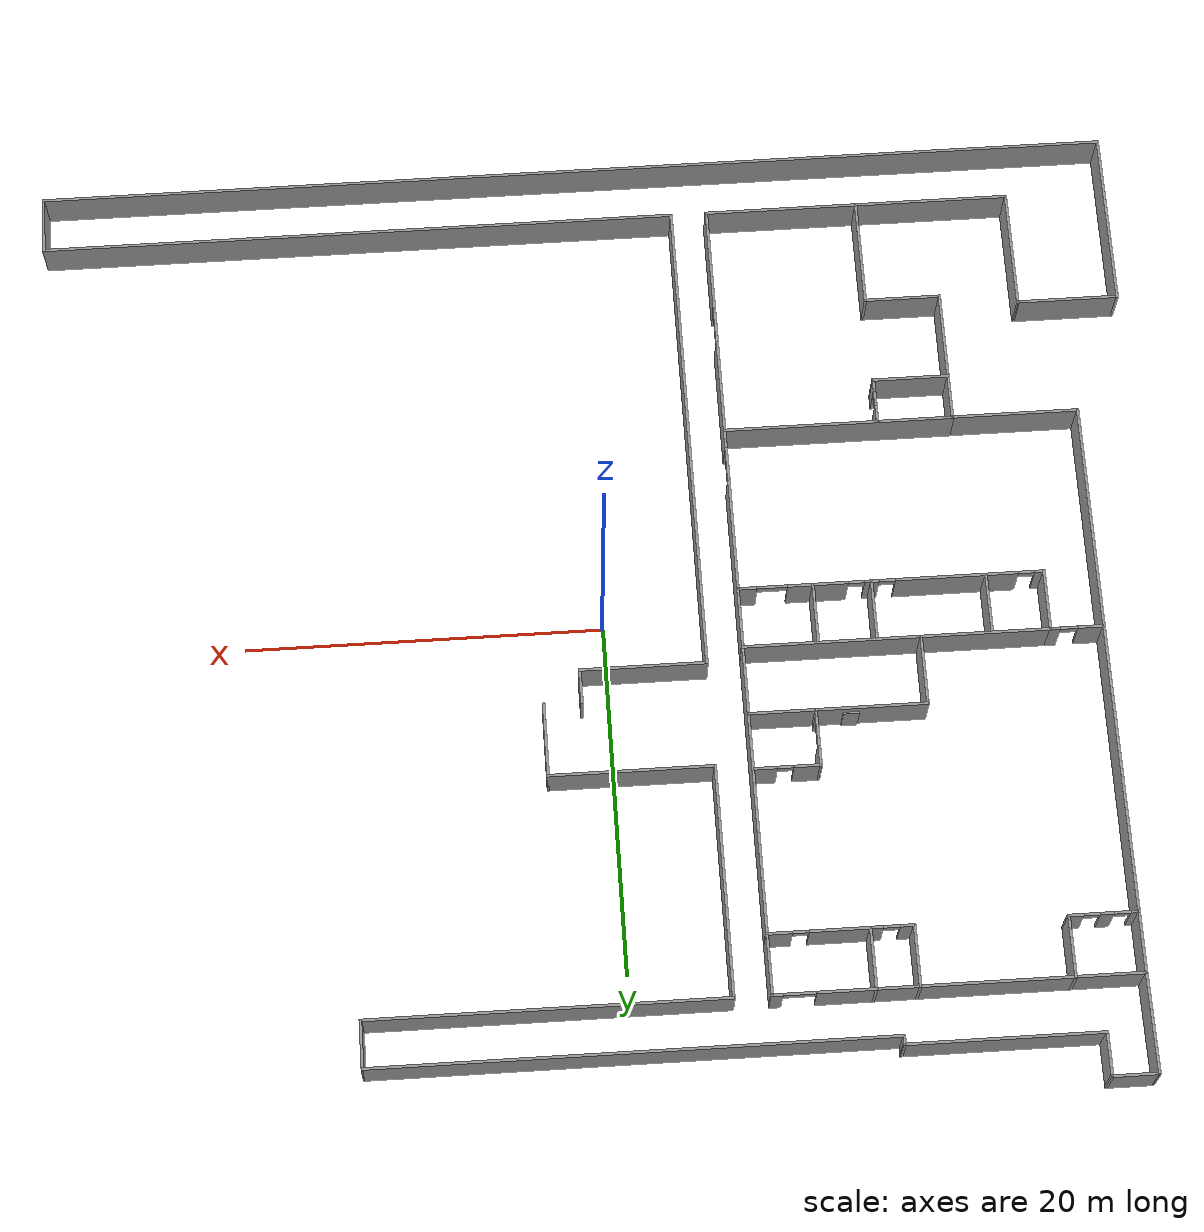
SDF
<?xml version='1.0'?>
<sdf version='1.6'>
  <model name='EDML'>
    <link name='Door_14'>
      <pose frame=''>-13.2894 6.35027 0 0 -0 0</pose>
      <self_collide>0</self_collide>
      <kinematic>0</kinematic>
      <visual name='Door_14_Visual'>
        <pose frame=''>0 0 1 0 -0 0</pose>
        <geometry>
          <box>
            <size>0.9 0.17 2</size>
          </box>
        </geometry>
        <material>
          <script>
            <uri>file://media/materials/scripts/gazebo.material</uri>
            <name>Gazebo/Grey</name>
          </script>
          <ambient>0.3 0.3 0.3 1</ambient>
          <diffuse>0.7 0.7 0.7 1</diffuse>
          <specular>0.01 0.01 0.01 1</specular>
          <emissive>0 0 0 1</emissive>
        </material>
        <transparency>0</transparency>
        <cast_shadows>1</cast_shadows>
      </visual>
      <collision name='Door_14_Collision'>
        <laser_retro>0</laser_retro>
        <max_contacts>10</max_contacts>
        <pose frame=''>0 0 1 0 -0 0</pose>
        <geometry>
          <box>
            <size>0.9 0.17 2</size>
          </box>
        </geometry>
        <surface>
          <friction>
            <ode>
              <mu>1</mu>
              <mu2>1</mu2>
              <fdir1>0 0 0</fdir1>
              <slip1>0</slip1>
              <slip2>0</slip2>
            </ode>
            <torsional>
              <coefficient>1</coefficient>
              <patch_radius>0</patch_radius>
              <surface_radius>0</surface_radius>
              <use_patch_radius>1</use_patch_radius>
              <ode>
                <slip>0</slip>
              </ode>
            </torsional>
          </friction>
          <bounce>
            <restitution_coefficient>0</restitution_coefficient>
            <threshold>1e+06</threshold>
          </bounce>
          <contact>
            <collide_without_contact>0</collide_without_contact>
            <collide_without_contact_bitmask>1</collide_without_contact_bitmask>
            <collide_bitmask>1</collide_bitmask>
            <ode>
              <soft_cfm>0</soft_cfm>
              <soft_erp>0.2</soft_erp>
              <kp>1e+13</kp>
              <kd>1</kd>
              <max_vel>0.01</max_vel>
              <min_depth>0</min_depth>
            </ode>
            <bullet>
              <split_impulse>1</split_impulse>
              <split_impulse_penetration_threshold>-0.01</split_impulse_penetration_threshold>
              <soft_cfm>0</soft_cfm>
              <soft_erp>0.2</soft_erp>
              <kp>1e+13</kp>
              <kd>1</kd>
            </bullet>
          </contact>
        </surface>
      </collision>
    </link>
    <link name='Wall_0'>
      <pose frame=''>1.5e-05 -27.6701 0 0 -0 0</pose>
      <self_collide>0</self_collide>
      <kinematic>0</kinematic>
      <visual name='Wall_0_Visual'>
        <pose frame=''>0 0 1.25 0 -0 0</pose>
        <geometry>
          <box>
            <size>61.603 0.15 2.5</size>
          </box>
        </geometry>
        <material>
          <script>
            <uri>file://media/materials/scripts/gazebo.material</uri>
            <name>Gazebo/Grey</name>
          </script>
          <ambient>1 1 1 1</ambient>
          <diffuse>0.7 0.7 0.7 1</diffuse>
          <specular>0.01 0.01 0.01 1</specular>
          <emissive>0 0 0 1</emissive>
        </material>
        <transparency>0</transparency>
        <cast_shadows>1</cast_shadows>
      </visual>
      <collision name='Wall_0_Collision'>
        <laser_retro>0</laser_retro>
        <max_contacts>10</max_contacts>
        <pose frame=''>0 0 1.25 0 -0 0</pose>
        <geometry>
          <box>
            <size>61.603 0.15 2.5</size>
          </box>
        </geometry>
        <surface>
          <friction>
            <ode>
              <mu>1</mu>
              <mu2>1</mu2>
              <fdir1>0 0 0</fdir1>
              <slip1>0</slip1>
              <slip2>0</slip2>
            </ode>
            <torsional>
              <coefficient>1</coefficient>
              <patch_radius>0</patch_radius>
              <surface_radius>0</surface_radius>
              <use_patch_radius>1</use_patch_radius>
              <ode>
                <slip>0</slip>
              </ode>
            </torsional>
          </friction>
          <bounce>
            <restitution_coefficient>0</restitution_coefficient>
            <threshold>1e+06</threshold>
          </bounce>
          <contact>
            <collide_without_contact>0</collide_without_contact>
            <collide_without_contact_bitmask>1</collide_without_contact_bitmask>
            <collide_bitmask>1</collide_bitmask>
            <ode>
              <soft_cfm>0</soft_cfm>
              <soft_erp>0.2</soft_erp>
              <kp>1e+13</kp>
              <kd>1</kd>
              <max_vel>0.01</max_vel>
              <min_depth>0</min_depth>
            </ode>
            <bullet>
              <split_impulse>1</split_impulse>
              <split_impulse_penetration_threshold>-0.01</split_impulse_penetration_threshold>
              <soft_cfm>0</soft_cfm>
              <soft_erp>0.2</soft_erp>
              <kp>1e+13</kp>
              <kd>1</kd>
            </bullet>
          </contact>
        </surface>
      </collision>
    </link>
    <link name='Wall_10'>
      <pose frame=''>-7.59652 -1.15055 0 0 -0 1.5708</pose>
      <self_collide>0</self_collide>
      <kinematic>0</kinematic>
      <visual name='Wall_10_Visual_0'>
        <pose frame=''>-20.3098 0 1.25 0 -0 0</pose>
        <geometry>
          <box>
            <size>6.1505 0.15 2.5</size>
          </box>
        </geometry>
        <material>
          <script>
            <uri>file://media/materials/scripts/gazebo.material</uri>
            <name>Gazebo/Grey</name>
          </script>
          <ambient>1 1 1 1</ambient>
          <diffuse>0.7 0.7 0.7 1</diffuse>
          <specular>0.01 0.01 0.01 1</specular>
          <emissive>0 0 0 1</emissive>
        </material>
        <transparency>0</transparency>
        <cast_shadows>1</cast_shadows>
      </visual>
      <visual name='Wall_10_Visual_1'>
        <pose frame=''>-11.8405 0 1.25 0 -0 0</pose>
        <geometry>
          <box>
            <size>6.588 0.15 2.5</size>
          </box>
        </geometry>
        <material>
          <script>
            <uri>file://media/materials/scripts/gazebo.material</uri>
            <name>Gazebo/Grey</name>
          </script>
          <ambient>1 1 1 1</ambient>
          <diffuse>0.7 0.7 0.7 1</diffuse>
          <specular>0.01 0.01 0.01 1</specular>
          <emissive>0 0 0 1</emissive>
        </material>
        <transparency>0</transparency>
        <cast_shadows>1</cast_shadows>
      </visual>
      <visual name='Wall_10_Visual_2'>
        <pose frame=''>8.42925 0 1.25 0 -0 0</pose>
        <geometry>
          <box>
            <size>29.9115 0.15 2.5</size>
          </box>
        </geometry>
        <material>
          <script>
            <uri>file://media/materials/scripts/gazebo.material</uri>
            <name>Gazebo/Grey</name>
          </script>
          <ambient>1 1 1 1</ambient>
          <diffuse>0.7 0.7 0.7 1</diffuse>
          <specular>0.01 0.01 0.01 1</specular>
          <emissive>0 0 0 1</emissive>
        </material>
        <transparency>0</transparency>
        <cast_shadows>1</cast_shadows>
      </visual>
      <visual name='Wall_10_Visual_3'>
        <pose frame=''>-16.1845 0 2.25 0 -0 0</pose>
        <geometry>
          <box>
            <size>2.1 0.15 0.5</size>
          </box>
        </geometry>
        <material>
          <script>
            <uri>file://media/materials/scripts/gazebo.material</uri>
            <name>Gazebo/Grey</name>
          </script>
          <ambient>1 1 1 1</ambient>
          <diffuse>0.7 0.7 0.7 1</diffuse>
          <specular>0.01 0.01 0.01 1</specular>
          <emissive>0 0 0 1</emissive>
        </material>
        <transparency>0</transparency>
        <cast_shadows>1</cast_shadows>
      </visual>
      <visual name='Wall_10_Visual_4'>
        <pose frame=''>-7.53651 0 2.25 0 -0 0</pose>
        <geometry>
          <box>
            <size>2.02 0.15 0.5</size>
          </box>
        </geometry>
        <material>
          <script>
            <uri>file://media/materials/scripts/gazebo.material</uri>
            <name>Gazebo/Grey</name>
          </script>
          <ambient>1 1 1 1</ambient>
          <diffuse>0.7 0.7 0.7 1</diffuse>
          <specular>0.01 0.01 0.01 1</specular>
          <emissive>0 0 0 1</emissive>
        </material>
        <transparency>0</transparency>
        <cast_shadows>1</cast_shadows>
      </visual>
      <collision name='Wall_10_Collision_0'>
        <laser_retro>0</laser_retro>
        <max_contacts>10</max_contacts>
        <pose frame=''>-20.3098 0 1.25 0 -0 0</pose>
        <geometry>
          <box>
            <size>6.1505 0.15 2.5</size>
          </box>
        </geometry>
        <surface>
          <friction>
            <ode>
              <mu>1</mu>
              <mu2>1</mu2>
              <fdir1>0 0 0</fdir1>
              <slip1>0</slip1>
              <slip2>0</slip2>
            </ode>
            <torsional>
              <coefficient>1</coefficient>
              <patch_radius>0</patch_radius>
              <surface_radius>0</surface_radius>
              <use_patch_radius>1</use_patch_radius>
              <ode>
                <slip>0</slip>
              </ode>
            </torsional>
          </friction>
          <bounce>
            <restitution_coefficient>0</restitution_coefficient>
            <threshold>1e+06</threshold>
          </bounce>
          <contact>
            <collide_without_contact>0</collide_without_contact>
            <collide_without_contact_bitmask>1</collide_without_contact_bitmask>
            <collide_bitmask>1</collide_bitmask>
            <ode>
              <soft_cfm>0</soft_cfm>
              <soft_erp>0.2</soft_erp>
              <kp>1e+13</kp>
              <kd>1</kd>
              <max_vel>0.01</max_vel>
              <min_depth>0</min_depth>
            </ode>
            <bullet>
              <split_impulse>1</split_impulse>
              <split_impulse_penetration_threshold>-0.01</split_impulse_penetration_threshold>
              <soft_cfm>0</soft_cfm>
              <soft_erp>0.2</soft_erp>
              <kp>1e+13</kp>
              <kd>1</kd>
            </bullet>
          </contact>
        </surface>
      </collision>
      <collision name='Wall_10_Collision_1'>
        <laser_retro>0</laser_retro>
        <max_contacts>10</max_contacts>
        <pose frame=''>-11.8405 0 1.25 0 -0 0</pose>
        <geometry>
          <box>
            <size>6.588 0.15 2.5</size>
          </box>
        </geometry>
        <surface>
          <friction>
            <ode>
              <mu>1</mu>
              <mu2>1</mu2>
              <fdir1>0 0 0</fdir1>
              <slip1>0</slip1>
              <slip2>0</slip2>
            </ode>
            <torsional>
              <coefficient>1</coefficient>
              <patch_radius>0</patch_radius>
              <surface_radius>0</surface_radius>
              <use_patch_radius>1</use_patch_radius>
              <ode>
                <slip>0</slip>
              </ode>
            </torsional>
          </friction>
          <bounce>
            <restitution_coefficient>0</restitution_coefficient>
            <threshold>1e+06</threshold>
          </bounce>
          <contact>
            <collide_without_contact>0</collide_without_contact>
            <collide_without_contact_bitmask>1</collide_without_contact_bitmask>
            <collide_bitmask>1</collide_bitmask>
            <ode>
              <soft_cfm>0</soft_cfm>
              <soft_erp>0.2</soft_erp>
              <kp>1e+13</kp>
              <kd>1</kd>
              <max_vel>0.01</max_vel>
              <min_depth>0</min_depth>
            </ode>
            <bullet>
              <split_impulse>1</split_impulse>
              <split_impulse_penetration_threshold>-0.01</split_impulse_penetration_threshold>
              <soft_cfm>0</soft_cfm>
              <soft_erp>0.2</soft_erp>
              <kp>1e+13</kp>
              <kd>1</kd>
            </bullet>
          </contact>
        </surface>
      </collision>
      <collision name='Wall_10_Collision_2'>
        <laser_retro>0</laser_retro>
        <max_contacts>10</max_contacts>
        <pose frame=''>8.42925 0 1.25 0 -0 0</pose>
        <geometry>
          <box>
            <size>29.9115 0.15 2.5</size>
          </box>
        </geometry>
        <surface>
          <friction>
            <ode>
              <mu>1</mu>
              <mu2>1</mu2>
              <fdir1>0 0 0</fdir1>
              <slip1>0</slip1>
              <slip2>0</slip2>
            </ode>
            <torsional>
              <coefficient>1</coefficient>
              <patch_radius>0</patch_radius>
              <surface_radius>0</surface_radius>
              <use_patch_radius>1</use_patch_radius>
              <ode>
                <slip>0</slip>
              </ode>
            </torsional>
          </friction>
          <bounce>
            <restitution_coefficient>0</restitution_coefficient>
            <threshold>1e+06</threshold>
          </bounce>
          <contact>
            <collide_without_contact>0</collide_without_contact>
            <collide_without_contact_bitmask>1</collide_without_contact_bitmask>
            <collide_bitmask>1</collide_bitmask>
            <ode>
              <soft_cfm>0</soft_cfm>
              <soft_erp>0.2</soft_erp>
              <kp>1e+13</kp>
              <kd>1</kd>
              <max_vel>0.01</max_vel>
              <min_depth>0</min_depth>
            </ode>
            <bullet>
              <split_impulse>1</split_impulse>
              <split_impulse_penetration_threshold>-0.01</split_impulse_penetration_threshold>
              <soft_cfm>0</soft_cfm>
              <soft_erp>0.2</soft_erp>
              <kp>1e+13</kp>
              <kd>1</kd>
            </bullet>
          </contact>
        </surface>
      </collision>
      <collision name='Wall_10_Collision_3'>
        <laser_retro>0</laser_retro>
        <max_contacts>10</max_contacts>
        <pose frame=''>-16.1845 0 2.25 0 -0 0</pose>
        <geometry>
          <box>
            <size>2.1 0.15 0.5</size>
          </box>
        </geometry>
        <surface>
          <friction>
            <ode>
              <mu>1</mu>
              <mu2>1</mu2>
              <fdir1>0 0 0</fdir1>
              <slip1>0</slip1>
              <slip2>0</slip2>
            </ode>
            <torsional>
              <coefficient>1</coefficient>
              <patch_radius>0</patch_radius>
              <surface_radius>0</surface_radius>
              <use_patch_radius>1</use_patch_radius>
              <ode>
                <slip>0</slip>
              </ode>
            </torsional>
          </friction>
          <bounce>
            <restitution_coefficient>0</restitution_coefficient>
            <threshold>1e+06</threshold>
          </bounce>
          <contact>
            <collide_without_contact>0</collide_without_contact>
            <collide_without_contact_bitmask>1</collide_without_contact_bitmask>
            <collide_bitmask>1</collide_bitmask>
            <ode>
              <soft_cfm>0</soft_cfm>
              <soft_erp>0.2</soft_erp>
              <kp>1e+13</kp>
              <kd>1</kd>
              <max_vel>0.01</max_vel>
              <min_depth>0</min_depth>
            </ode>
            <bullet>
              <split_impulse>1</split_impulse>
              <split_impulse_penetration_threshold>-0.01</split_impulse_penetration_threshold>
              <soft_cfm>0</soft_cfm>
              <soft_erp>0.2</soft_erp>
              <kp>1e+13</kp>
              <kd>1</kd>
            </bullet>
          </contact>
        </surface>
      </collision>
      <collision name='Wall_10_Collision_4'>
        <laser_retro>0</laser_retro>
        <max_contacts>10</max_contacts>
        <pose frame=''>-7.53651 0 2.25 0 -0 0</pose>
        <geometry>
          <box>
            <size>2.02 0.15 0.5</size>
          </box>
        </geometry>
        <surface>
          <friction>
            <ode>
              <mu>1</mu>
              <mu2>1</mu2>
              <fdir1>0 0 0</fdir1>
              <slip1>0</slip1>
              <slip2>0</slip2>
            </ode>
            <torsional>
              <coefficient>1</coefficient>
              <patch_radius>0</patch_radius>
              <surface_radius>0</surface_radius>
              <use_patch_radius>1</use_patch_radius>
              <ode>
                <slip>0</slip>
              </ode>
            </torsional>
          </friction>
          <bounce>
            <restitution_coefficient>0</restitution_coefficient>
            <threshold>1e+06</threshold>
          </bounce>
          <contact>
            <collide_without_contact>0</collide_without_contact>
            <collide_without_contact_bitmask>1</collide_without_contact_bitmask>
            <collide_bitmask>1</collide_bitmask>
            <ode>
              <soft_cfm>0</soft_cfm>
              <soft_erp>0.2</soft_erp>
              <kp>1e+13</kp>
              <kd>1</kd>
              <max_vel>0.01</max_vel>
              <min_depth>0</min_depth>
            </ode>
            <bullet>
              <split_impulse>1</split_impulse>
              <split_impulse_penetration_threshold>-0.01</split_impulse_penetration_threshold>
              <soft_cfm>0</soft_cfm>
              <soft_erp>0.2</soft_erp>
              <kp>1e+13</kp>
              <kd>1</kd>
            </bullet>
          </contact>
        </surface>
      </collision>
    </link>
    <link name='Wall_103'>
      <pose frame=''>-13.181 20.4654 0 0 0 -1.5708</pose>
      <self_collide>0</self_collide>
      <kinematic>0</kinematic>
      <visual name='Wall_103_Visual'>
        <pose frame=''>0 0 1.25 0 -0 0</pose>
        <geometry>
          <box>
            <size>3.539 0.15 2.5</size>
          </box>
        </geometry>
        <material>
          <script>
            <uri>file://media/materials/scripts/gazebo.material</uri>
            <name>Gazebo/Grey</name>
          </script>
          <ambient>1 1 1 1</ambient>
          <diffuse>0.7 0.7 0.7 1</diffuse>
          <specular>0.01 0.01 0.01 1</specular>
          <emissive>0 0 0 1</emissive>
        </material>
        <transparency>0</transparency>
        <cast_shadows>1</cast_shadows>
      </visual>
      <collision name='Wall_103_Collision'>
        <laser_retro>0</laser_retro>
        <max_contacts>10</max_contacts>
        <pose frame=''>0 0 1.25 0 -0 0</pose>
        <geometry>
          <box>
            <size>3.539 0.15 2.5</size>
          </box>
        </geometry>
        <surface>
          <friction>
            <ode>
              <mu>1</mu>
              <mu2>1</mu2>
              <fdir1>0 0 0</fdir1>
              <slip1>0</slip1>
              <slip2>0</slip2>
            </ode>
            <torsional>
              <coefficient>1</coefficient>
              <patch_radius>0</patch_radius>
              <surface_radius>0</surface_radius>
              <use_patch_radius>1</use_patch_radius>
              <ode>
                <slip>0</slip>
              </ode>
            </torsional>
          </friction>
          <bounce>
            <restitution_coefficient>0</restitution_coefficient>
            <threshold>1e+06</threshold>
          </bounce>
          <contact>
            <collide_without_contact>0</collide_without_contact>
            <collide_without_contact_bitmask>1</collide_without_contact_bitmask>
            <collide_bitmask>1</collide_bitmask>
            <ode>
              <soft_cfm>0</soft_cfm>
              <soft_erp>0.2</soft_erp>
              <kp>1e+13</kp>
              <kd>1</kd>
              <max_vel>0.01</max_vel>
              <min_depth>0</min_depth>
            </ode>
            <bullet>
              <split_impulse>1</split_impulse>
              <split_impulse_penetration_threshold>-0.01</split_impulse_penetration_threshold>
              <soft_cfm>0</soft_cfm>
              <soft_erp>0.2</soft_erp>
              <kp>1e+13</kp>
              <kd>1</kd>
            </bullet>
          </contact>
        </surface>
      </collision>
    </link>
    <link name='Wall_105'>
      <pose frame=''>-11.568 18.7709 0 0 -0 3.14159</pose>
      <self_collide>0</self_collide>
      <kinematic>0</kinematic>
      <visual name='Wall_105_Visual_0'>
        <pose frame=''>-3.3243 0 1.25 0 -0 0</pose>
        <geometry>
          <box>
            <size>1.44441 0.15 2.5</size>
          </box>
        </geometry>
        <material>
          <script>
            <uri>file://media/materials/scripts/gazebo.material</uri>
            <name>Gazebo/Grey</name>
          </script>
          <ambient>1 1 1 1</ambient>
          <diffuse>0.7 0.7 0.7 1</diffuse>
          <specular>0.01 0.01 0.01 1</specular>
          <emissive>0 0 0 1</emissive>
        </material>
        <transparency>0</transparency>
        <cast_shadows>1</cast_shadows>
      </visual>
      <visual name='Wall_105_Visual_1'>
        <pose frame=''>0.305332 0 1.25 0 -0 0</pose>
        <geometry>
          <box>
            <size>4.01485 0.15 2.5</size>
          </box>
        </geometry>
        <material>
          <script>
            <uri>file://media/materials/scripts/gazebo.material</uri>
            <name>Gazebo/Grey</name>
          </script>
          <ambient>1 1 1 1</ambient>
          <diffuse>0.7 0.7 0.7 1</diffuse>
          <specular>0.01 0.01 0.01 1</specular>
          <emissive>0 0 0 1</emissive>
        </material>
        <transparency>0</transparency>
        <cast_shadows>1</cast_shadows>
      </visual>
      <visual name='Wall_105_Visual_2'>
        <pose frame=''>3.62963 0 1.25 0 -0 0</pose>
        <geometry>
          <box>
            <size>0.833746 0.15 2.5</size>
          </box>
        </geometry>
        <material>
          <script>
            <uri>file://media/materials/scripts/gazebo.material</uri>
            <name>Gazebo/Grey</name>
          </script>
          <ambient>1 1 1 1</ambient>
          <diffuse>0.7 0.7 0.7 1</diffuse>
          <specular>0.01 0.01 0.01 1</specular>
          <emissive>0 0 0 1</emissive>
        </material>
        <transparency>0</transparency>
        <cast_shadows>1</cast_shadows>
      </visual>
      <visual name='Wall_105_Visual_3'>
        <pose frame=''>-2.15209 0 2.25 0 -0 0</pose>
        <geometry>
          <box>
            <size>0.9 0.15 0.5</size>
          </box>
        </geometry>
        <material>
          <script>
            <uri>file://media/materials/scripts/gazebo.material</uri>
            <name>Gazebo/Grey</name>
          </script>
          <ambient>1 1 1 1</ambient>
          <diffuse>0.7 0.7 0.7 1</diffuse>
          <specular>0.01 0.01 0.01 1</specular>
          <emissive>0 0 0 1</emissive>
        </material>
        <transparency>0</transparency>
        <cast_shadows>1</cast_shadows>
      </visual>
      <visual name='Wall_105_Visual_4'>
        <pose frame=''>2.76275 0 2.25 0 -0 0</pose>
        <geometry>
          <box>
            <size>0.9 0.15 0.5</size>
          </box>
        </geometry>
        <material>
          <script>
            <uri>file://media/materials/scripts/gazebo.material</uri>
            <name>Gazebo/Grey</name>
          </script>
          <ambient>1 1 1 1</ambient>
          <diffuse>0.7 0.7 0.7 1</diffuse>
          <specular>0.01 0.01 0.01 1</specular>
          <emissive>0 0 0 1</emissive>
        </material>
        <transparency>0</transparency>
        <cast_shadows>1</cast_shadows>
      </visual>
      <collision name='Wall_105_Collision_0'>
        <laser_retro>0</laser_retro>
        <max_contacts>10</max_contacts>
        <pose frame=''>-3.3243 0 1.25 0 -0 0</pose>
        <geometry>
          <box>
            <size>1.44441 0.15 2.5</size>
          </box>
        </geometry>
        <surface>
          <friction>
            <ode>
              <mu>1</mu>
              <mu2>1</mu2>
              <fdir1>0 0 0</fdir1>
              <slip1>0</slip1>
              <slip2>0</slip2>
            </ode>
            <torsional>
              <coefficient>1</coefficient>
              <patch_radius>0</patch_radius>
              <surface_radius>0</surface_radius>
              <use_patch_radius>1</use_patch_radius>
              <ode>
                <slip>0</slip>
              </ode>
            </torsional>
          </friction>
          <bounce>
            <restitution_coefficient>0</restitution_coefficient>
            <threshold>1e+06</threshold>
          </bounce>
          <contact>
            <collide_without_contact>0</collide_without_contact>
            <collide_without_contact_bitmask>1</collide_without_contact_bitmask>
            <collide_bitmask>1</collide_bitmask>
            <ode>
              <soft_cfm>0</soft_cfm>
              <soft_erp>0.2</soft_erp>
              <kp>1e+13</kp>
              <kd>1</kd>
              <max_vel>0.01</max_vel>
              <min_depth>0</min_depth>
            </ode>
            <bullet>
              <split_impulse>1</split_impulse>
              <split_impulse_penetration_threshold>-0.01</split_impulse_penetration_threshold>
              <soft_cfm>0</soft_cfm>
              <soft_erp>0.2</soft_erp>
              <kp>1e+13</kp>
              <kd>1</kd>
            </bullet>
          </contact>
        </surface>
      </collision>
      <collision name='Wall_105_Collision_1'>
        <laser_retro>0</laser_retro>
        <max_contacts>10</max_contacts>
        <pose frame=''>0.305332 0 1.25 0 -0 0</pose>
        <geometry>
          <box>
            <size>4.01485 0.15 2.5</size>
          </box>
        </geometry>
        <surface>
          <friction>
            <ode>
              <mu>1</mu>
              <mu2>1</mu2>
              <fdir1>0 0 0</fdir1>
              <slip1>0</slip1>
              <slip2>0</slip2>
            </ode>
            <torsional>
              <coefficient>1</coefficient>
              <patch_radius>0</patch_radius>
              <surface_radius>0</surface_radius>
              <use_patch_radius>1</use_patch_radius>
              <ode>
                <slip>0</slip>
              </ode>
            </torsional>
          </friction>
          <bounce>
            <restitution_coefficient>0</restitution_coefficient>
            <threshold>1e+06</threshold>
          </bounce>
          <contact>
            <collide_without_contact>0</collide_without_contact>
            <collide_without_contact_bitmask>1</collide_without_contact_bitmask>
            <collide_bitmask>1</collide_bitmask>
            <ode>
              <soft_cfm>0</soft_cfm>
              <soft_erp>0.2</soft_erp>
              <kp>1e+13</kp>
              <kd>1</kd>
              <max_vel>0.01</max_vel>
              <min_depth>0</min_depth>
            </ode>
            <bullet>
              <split_impulse>1</split_impulse>
              <split_impulse_penetration_threshold>-0.01</split_impulse_penetration_threshold>
              <soft_cfm>0</soft_cfm>
              <soft_erp>0.2</soft_erp>
              <kp>1e+13</kp>
              <kd>1</kd>
            </bullet>
          </contact>
        </surface>
      </collision>
      <collision name='Wall_105_Collision_2'>
        <laser_retro>0</laser_retro>
        <max_contacts>10</max_contacts>
        <pose frame=''>3.62963 0 1.25 0 -0 0</pose>
        <geometry>
          <box>
            <size>0.833746 0.15 2.5</size>
          </box>
        </geometry>
        <surface>
          <friction>
            <ode>
              <mu>1</mu>
              <mu2>1</mu2>
              <fdir1>0 0 0</fdir1>
              <slip1>0</slip1>
              <slip2>0</slip2>
            </ode>
            <torsional>
              <coefficient>1</coefficient>
              <patch_radius>0</patch_radius>
              <surface_radius>0</surface_radius>
              <use_patch_radius>1</use_patch_radius>
              <ode>
                <slip>0</slip>
              </ode>
            </torsional>
          </friction>
          <bounce>
            <restitution_coefficient>0</restitution_coefficient>
            <threshold>1e+06</threshold>
          </bounce>
          <contact>
            <collide_without_contact>0</collide_without_contact>
            <collide_without_contact_bitmask>1</collide_without_contact_bitmask>
            <collide_bitmask>1</collide_bitmask>
            <ode>
              <soft_cfm>0</soft_cfm>
              <soft_erp>0.2</soft_erp>
              <kp>1e+13</kp>
              <kd>1</kd>
              <max_vel>0.01</max_vel>
              <min_depth>0</min_depth>
            </ode>
            <bullet>
              <split_impulse>1</split_impulse>
              <split_impulse_penetration_threshold>-0.01</split_impulse_penetration_threshold>
              <soft_cfm>0</soft_cfm>
              <soft_erp>0.2</soft_erp>
              <kp>1e+13</kp>
              <kd>1</kd>
            </bullet>
          </contact>
        </surface>
      </collision>
      <collision name='Wall_105_Collision_4'>
        <laser_retro>0</laser_retro>
        <max_contacts>10</max_contacts>
        <pose frame=''>2.76275 0 2.25 0 -0 0</pose>
        <geometry>
          <box>
            <size>0.9 0.15 0.5</size>
          </box>
        </geometry>
        <surface>
          <friction>
            <ode>
              <mu>1</mu>
              <mu2>1</mu2>
              <fdir1>0 0 0</fdir1>
              <slip1>0</slip1>
              <slip2>0</slip2>
            </ode>
            <torsional>
              <coefficient>1</coefficient>
              <patch_radius>0</patch_radius>
              <surface_radius>0</surface_radius>
              <use_patch_radius>1</use_patch_radius>
              <ode>
                <slip>0</slip>
              </ode>
            </torsional>
          </friction>
          <bounce>
            <restitution_coefficient>0</restitution_coefficient>
            <threshold>1e+06</threshold>
          </bounce>
          <contact>
            <collide_without_contact>0</collide_without_contact>
            <collide_without_contact_bitmask>1</collide_without_contact_bitmask>
            <collide_bitmask>1</collide_bitmask>
            <ode>
              <soft_cfm>0</soft_cfm>
              <soft_erp>0.2</soft_erp>
              <kp>1e+13</kp>
              <kd>1</kd>
              <max_vel>0.01</max_vel>
              <min_depth>0</min_depth>
            </ode>
            <bullet>
              <split_impulse>1</split_impulse>
              <split_impulse_penetration_threshold>-0.01</split_impulse_penetration_threshold>
              <soft_cfm>0</soft_cfm>
              <soft_erp>0.2</soft_erp>
              <kp>1e+13</kp>
              <kd>1</kd>
            </bullet>
          </contact>
        </surface>
      </collision>
      <collision name='Wall_105_Collision_3'>
        <laser_retro>0</laser_retro>
        <max_contacts>10</max_contacts>
        <pose frame=''>-2.15209 0 2.25 0 -0 0</pose>
        <geometry>
          <box>
            <size>0.9 0.15 0.5</size>
          </box>
        </geometry>
        <surface>
          <friction>
            <ode>
              <mu>1</mu>
              <mu2>1</mu2>
              <fdir1>0 0 0</fdir1>
              <slip1>0</slip1>
              <slip2>0</slip2>
            </ode>
            <torsional>
              <coefficient>1</coefficient>
              <patch_radius>0</patch_radius>
              <surface_radius>0</surface_radius>
              <use_patch_radius>1</use_patch_radius>
              <ode>
                <slip>0</slip>
              </ode>
            </torsional>
          </friction>
          <bounce>
            <restitution_coefficient>0</restitution_coefficient>
            <threshold>1e+06</threshold>
          </bounce>
          <contact>
            <collide_without_contact>0</collide_without_contact>
            <collide_without_contact_bitmask>1</collide_without_contact_bitmask>
            <collide_bitmask>1</collide_bitmask>
            <ode>
              <soft_cfm>0</soft_cfm>
              <soft_erp>0.2</soft_erp>
              <kp>1e+13</kp>
              <kd>1</kd>
              <max_vel>0.01</max_vel>
              <min_depth>0</min_depth>
            </ode>
            <bullet>
              <split_impulse>1</split_impulse>
              <split_impulse_penetration_threshold>-0.01</split_impulse_penetration_threshold>
              <soft_cfm>0</soft_cfm>
              <soft_erp>0.2</soft_erp>
              <kp>1e+13</kp>
              <kd>1</kd>
            </bullet>
          </contact>
        </surface>
      </collision>
    </link>
    <link name='Wall_13'>
      <pose frame=''>-17.6295 22.1597 0 0 -0 3.14157</pose>
      <self_collide>0</self_collide>
      <kinematic>0</kinematic>
      <visual name='Wall_13_Visual_2'>
        <pose frame=''>-8.548 0 2.25 0 -0 0</pose>
        <geometry>
          <box>
            <size>1.814 0.15 0.5</size>
          </box>
        </geometry>
        <material>
          <script>
            <uri>file://media/materials/scripts/gazebo.material</uri>
            <name>Gazebo/Grey</name>
          </script>
          <ambient>1 1 1 1</ambient>
          <diffuse>0.7 0.7 0.7 1</diffuse>
          <specular>0.01 0.01 0.01 1</specular>
          <emissive>0 0 0 1</emissive>
        </material>
        <transparency>0</transparency>
        <cast_shadows>1</cast_shadows>
      </visual>
      <visual name='Wall_13_Visual_0'>
        <pose frame=''>-9.78149 0 1.25 0 -0 0</pose>
        <geometry>
          <box>
            <size>0.652987 0.15 2.5</size>
          </box>
        </geometry>
        <material>
          <script>
            <uri>file://media/materials/scripts/gazebo.material</uri>
            <name>Gazebo/Grey</name>
          </script>
          <ambient>1 1 1 1</ambient>
          <diffuse>0.7 0.7 0.7 1</diffuse>
          <specular>0.01 0.01 0.01 1</specular>
          <emissive>0 0 0 1</emissive>
        </material>
        <transparency>0</transparency>
        <cast_shadows>1</cast_shadows>
      </visual>
      <visual name='Wall_13_Visual_1'>
        <pose frame=''>1.23349 0 1.25 0 -0 0</pose>
        <geometry>
          <box>
            <size>17.749 0.15 2.5</size>
          </box>
        </geometry>
        <material>
          <script>
            <uri>file://media/materials/scripts/gazebo.material</uri>
            <name>Gazebo/Grey</name>
          </script>
          <ambient>1 1 1 1</ambient>
          <diffuse>0.7 0.7 0.7 1</diffuse>
          <specular>0.01 0.01 0.01 1</specular>
          <emissive>0 0 0 1</emissive>
        </material>
        <transparency>0</transparency>
        <cast_shadows>1</cast_shadows>
      </visual>
      <collision name='Wall_13_Collision_0'>
        <laser_retro>0</laser_retro>
        <max_contacts>10</max_contacts>
        <pose frame=''>-9.78149 0 1.25 0 -0 0</pose>
        <geometry>
          <box>
            <size>0.652987 0.15 2.5</size>
          </box>
        </geometry>
        <surface>
          <friction>
            <ode>
              <mu>1</mu>
              <mu2>1</mu2>
              <fdir1>0 0 0</fdir1>
              <slip1>0</slip1>
              <slip2>0</slip2>
            </ode>
            <torsional>
              <coefficient>1</coefficient>
              <patch_radius>0</patch_radius>
              <surface_radius>0</surface_radius>
              <use_patch_radius>1</use_patch_radius>
              <ode>
                <slip>0</slip>
              </ode>
            </torsional>
          </friction>
          <bounce>
            <restitution_coefficient>0</restitution_coefficient>
            <threshold>1e+06</threshold>
          </bounce>
          <contact>
            <collide_without_contact>0</collide_without_contact>
            <collide_without_contact_bitmask>1</collide_without_contact_bitmask>
            <collide_bitmask>1</collide_bitmask>
            <ode>
              <soft_cfm>0</soft_cfm>
              <soft_erp>0.2</soft_erp>
              <kp>1e+13</kp>
              <kd>1</kd>
              <max_vel>0.01</max_vel>
              <min_depth>0</min_depth>
            </ode>
            <bullet>
              <split_impulse>1</split_impulse>
              <split_impulse_penetration_threshold>-0.01</split_impulse_penetration_threshold>
              <soft_cfm>0</soft_cfm>
              <soft_erp>0.2</soft_erp>
              <kp>1e+13</kp>
              <kd>1</kd>
            </bullet>
          </contact>
        </surface>
      </collision>
      <collision name='Wall_13_Collision_1'>
        <laser_retro>0</laser_retro>
        <max_contacts>10</max_contacts>
        <pose frame=''>1.23349 0 1.25 0 -0 0</pose>
        <geometry>
          <box>
            <size>17.749 0.15 2.5</size>
          </box>
        </geometry>
        <surface>
          <friction>
            <ode>
              <mu>1</mu>
              <mu2>1</mu2>
              <fdir1>0 0 0</fdir1>
              <slip1>0</slip1>
              <slip2>0</slip2>
            </ode>
            <torsional>
              <coefficient>1</coefficient>
              <patch_radius>0</patch_radius>
              <surface_radius>0</surface_radius>
              <use_patch_radius>1</use_patch_radius>
              <ode>
                <slip>0</slip>
              </ode>
            </torsional>
          </friction>
          <bounce>
            <restitution_coefficient>0</restitution_coefficient>
            <threshold>1e+06</threshold>
          </bounce>
          <contact>
            <collide_without_contact>0</collide_without_contact>
            <collide_without_contact_bitmask>1</collide_without_contact_bitmask>
            <collide_bitmask>1</collide_bitmask>
            <ode>
              <soft_cfm>0</soft_cfm>
              <soft_erp>0.2</soft_erp>
              <kp>1e+13</kp>
              <kd>1</kd>
              <max_vel>0.01</max_vel>
              <min_depth>0</min_depth>
            </ode>
            <bullet>
              <split_impulse>1</split_impulse>
              <split_impulse_penetration_threshold>-0.01</split_impulse_penetration_threshold>
              <soft_cfm>0</soft_cfm>
              <soft_erp>0.2</soft_erp>
              <kp>1e+13</kp>
              <kd>1</kd>
            </bullet>
          </contact>
        </surface>
      </collision>
      <collision name='Wall_13_Collision_2'>
        <laser_retro>0</laser_retro>
        <max_contacts>10</max_contacts>
        <pose frame=''>-8.548 0 2.25 0 -0 0</pose>
        <geometry>
          <box>
            <size>1.814 0.15 0.5</size>
          </box>
        </geometry>
        <surface>
          <friction>
            <ode>
              <mu>1</mu>
              <mu2>1</mu2>
              <fdir1>0 0 0</fdir1>
              <slip1>0</slip1>
              <slip2>0</slip2>
            </ode>
            <torsional>
              <coefficient>1</coefficient>
              <patch_radius>0</patch_radius>
              <surface_radius>0</surface_radius>
              <use_patch_radius>1</use_patch_radius>
              <ode>
                <slip>0</slip>
              </ode>
            </torsional>
          </friction>
          <bounce>
            <restitution_coefficient>0</restitution_coefficient>
            <threshold>1e+06</threshold>
          </bounce>
          <contact>
            <collide_without_contact>0</collide_without_contact>
            <collide_without_contact_bitmask>1</collide_without_contact_bitmask>
            <collide_bitmask>1</collide_bitmask>
            <ode>
              <soft_cfm>0</soft_cfm>
              <soft_erp>0.2</soft_erp>
              <kp>1e+13</kp>
              <kd>1</kd>
              <max_vel>0.01</max_vel>
              <min_depth>0</min_depth>
            </ode>
            <bullet>
              <split_impulse>1</split_impulse>
              <split_impulse_penetration_threshold>-0.01</split_impulse_penetration_threshold>
              <soft_cfm>0</soft_cfm>
              <soft_erp>0.2</soft_erp>
              <kp>1e+13</kp>
              <kd>1</kd>
            </bullet>
          </contact>
        </surface>
      </collision>
    </link>
    <link name='Wall_144'>
      <pose frame=''>-23.8745 20.4654 0 0 0 -1.5708</pose>
      <self_collide>0</self_collide>
      <kinematic>0</kinematic>
      <visual name='Wall_144_Visual'>
        <pose frame=''>0 0 1.25 0 -0 0</pose>
        <geometry>
          <box>
            <size>3.539 0.15 2.5</size>
          </box>
        </geometry>
        <material>
          <script>
            <uri>file://media/materials/scripts/gazebo.material</uri>
            <name>Gazebo/Grey</name>
          </script>
          <ambient>1 1 1 1</ambient>
          <diffuse>0.7 0.7 0.7 1</diffuse>
          <specular>0.01 0.01 0.01 1</specular>
          <emissive>0 0 0 1</emissive>
        </material>
        <transparency>0</transparency>
        <cast_shadows>1</cast_shadows>
      </visual>
      <collision name='Wall_144_Collision'>
        <laser_retro>0</laser_retro>
        <max_contacts>10</max_contacts>
        <pose frame=''>0 0 1.25 0 -0 0</pose>
        <geometry>
          <box>
            <size>3.539 0.15 2.5</size>
          </box>
        </geometry>
        <surface>
          <friction>
            <ode>
              <mu>1</mu>
              <mu2>1</mu2>
              <fdir1>0 0 0</fdir1>
              <slip1>0</slip1>
              <slip2>0</slip2>
            </ode>
            <torsional>
              <coefficient>1</coefficient>
              <patch_radius>0</patch_radius>
              <surface_radius>0</surface_radius>
              <use_patch_radius>1</use_patch_radius>
              <ode>
                <slip>0</slip>
              </ode>
            </torsional>
          </friction>
          <bounce>
            <restitution_coefficient>0</restitution_coefficient>
            <threshold>1e+06</threshold>
          </bounce>
          <contact>
            <collide_without_contact>0</collide_without_contact>
            <collide_without_contact_bitmask>1</collide_without_contact_bitmask>
            <collide_bitmask>1</collide_bitmask>
            <ode>
              <soft_cfm>0</soft_cfm>
              <soft_erp>0.2</soft_erp>
              <kp>1e+13</kp>
              <kd>1</kd>
              <max_vel>0.01</max_vel>
              <min_depth>0</min_depth>
            </ode>
            <bullet>
              <split_impulse>1</split_impulse>
              <split_impulse_penetration_threshold>-0.01</split_impulse_penetration_threshold>
              <soft_cfm>0</soft_cfm>
              <soft_erp>0.2</soft_erp>
              <kp>1e+13</kp>
              <kd>1</kd>
            </bullet>
          </contact>
        </surface>
      </collision>
    </link>
    <link name='Wall_146'>
      <pose frame=''>-27.6625 12.2514 0 0 -0 1.5708</pose>
      <self_collide>0</self_collide>
      <kinematic>0</kinematic>
      <visual name='Wall_146_Visual'>
        <pose frame=''>0 0 1.25 0 -0 0</pose>
        <geometry>
          <box>
            <size>19.9666 0.15 2.5</size>
          </box>
        </geometry>
        <material>
          <script>
            <uri>file://media/materials/scripts/gazebo.material</uri>
            <name>Gazebo/Grey</name>
          </script>
          <ambient>1 1 1 1</ambient>
          <diffuse>0.7 0.7 0.7 1</diffuse>
          <specular>0.01 0.01 0.01 1</specular>
          <emissive>0 0 0 1</emissive>
        </material>
        <transparency>0</transparency>
        <cast_shadows>1</cast_shadows>
      </visual>
      <collision name='Wall_146_Collision'>
        <laser_retro>0</laser_retro>
        <max_contacts>10</max_contacts>
        <pose frame=''>0 0 1.25 0 -0 0</pose>
        <geometry>
          <box>
            <size>19.9666 0.15 2.5</size>
          </box>
        </geometry>
        <surface>
          <friction>
            <ode>
              <mu>1</mu>
              <mu2>1</mu2>
              <fdir1>0 0 0</fdir1>
              <slip1>0</slip1>
              <slip2>0</slip2>
            </ode>
            <torsional>
              <coefficient>1</coefficient>
              <patch_radius>0</patch_radius>
              <surface_radius>0</surface_radius>
              <use_patch_radius>1</use_patch_radius>
              <ode>
                <slip>0</slip>
              </ode>
            </torsional>
          </friction>
          <bounce>
            <restitution_coefficient>0</restitution_coefficient>
            <threshold>1e+06</threshold>
          </bounce>
          <contact>
            <collide_without_contact>0</collide_without_contact>
            <collide_without_contact_bitmask>1</collide_without_contact_bitmask>
            <collide_bitmask>1</collide_bitmask>
            <ode>
              <soft_cfm>0</soft_cfm>
              <soft_erp>0.2</soft_erp>
              <kp>1e+13</kp>
              <kd>1</kd>
              <max_vel>0.01</max_vel>
              <min_depth>0</min_depth>
            </ode>
            <bullet>
              <split_impulse>1</split_impulse>
              <split_impulse_penetration_threshold>-0.01</split_impulse_penetration_threshold>
              <soft_cfm>0</soft_cfm>
              <soft_erp>0.2</soft_erp>
              <kp>1e+13</kp>
              <kd>1</kd>
            </bullet>
          </contact>
        </surface>
      </collision>
    </link>
    <link name='Wall_148'>
      <pose frame=''>-12.566 6.25695 0 0 -0 3.14159</pose>
      <self_collide>0</self_collide>
      <kinematic>0</kinematic>
      <visual name='Wall_148_Visual'>
        <pose frame=''>0 0 1.25 0 -0 0</pose>
        <geometry>
          <box>
            <size>9.993 0.15 2.5</size>
          </box>
        </geometry>
        <material>
          <script>
            <uri>file://media/materials/scripts/gazebo.material</uri>
            <name>Gazebo/Grey</name>
          </script>
          <ambient>1 1 1 1</ambient>
          <diffuse>0.7 0.7 0.7 1</diffuse>
          <specular>0.01 0.01 0.01 1</specular>
          <emissive>0 0 0 1</emissive>
        </material>
        <transparency>0</transparency>
        <cast_shadows>1</cast_shadows>
      </visual>
      <collision name='Wall_148_Collision'>
        <laser_retro>0</laser_retro>
        <max_contacts>10</max_contacts>
        <pose frame=''>0 0 1.25 0 -0 0</pose>
        <geometry>
          <box>
            <size>9.993 0.15 2.5</size>
          </box>
        </geometry>
        <surface>
          <friction>
            <ode>
              <mu>1</mu>
              <mu2>1</mu2>
              <fdir1>0 0 0</fdir1>
              <slip1>0</slip1>
              <slip2>0</slip2>
            </ode>
            <torsional>
              <coefficient>1</coefficient>
              <patch_radius>0</patch_radius>
              <surface_radius>0</surface_radius>
              <use_patch_radius>1</use_patch_radius>
              <ode>
                <slip>0</slip>
              </ode>
            </torsional>
          </friction>
          <bounce>
            <restitution_coefficient>0</restitution_coefficient>
            <threshold>1e+06</threshold>
          </bounce>
          <contact>
            <collide_without_contact>0</collide_without_contact>
            <collide_without_contact_bitmask>1</collide_without_contact_bitmask>
            <collide_bitmask>1</collide_bitmask>
            <ode>
              <soft_cfm>0</soft_cfm>
              <soft_erp>0.2</soft_erp>
              <kp>1e+13</kp>
              <kd>1</kd>
              <max_vel>0.01</max_vel>
              <min_depth>0</min_depth>
            </ode>
            <bullet>
              <split_impulse>1</split_impulse>
              <split_impulse_penetration_threshold>-0.01</split_impulse_penetration_threshold>
              <soft_cfm>0</soft_cfm>
              <soft_erp>0.2</soft_erp>
              <kp>1e+13</kp>
              <kd>1</kd>
            </bullet>
          </contact>
        </surface>
      </collision>
    </link>
    <link name='Wall_150'>
      <pose frame=''>-17.4875 4.33195 0 0 0 -1.5708</pose>
      <self_collide>0</self_collide>
      <kinematic>0</kinematic>
      <visual name='Wall_150_Visual'>
        <pose frame=''>0 0 1.25 0 -0 0</pose>
        <geometry>
          <box>
            <size>4 0.15 2.5</size>
          </box>
        </geometry>
        <material>
          <script>
            <uri>file://media/materials/scripts/gazebo.material</uri>
            <name>Gazebo/Grey</name>
          </script>
          <ambient>1 1 1 1</ambient>
          <diffuse>0.7 0.7 0.7 1</diffuse>
          <specular>0.01 0.01 0.01 1</specular>
          <emissive>0 0 0 1</emissive>
        </material>
        <transparency>0</transparency>
        <cast_shadows>1</cast_shadows>
      </visual>
      <collision name='Wall_150_Collision'>
        <laser_retro>0</laser_retro>
        <max_contacts>10</max_contacts>
        <pose frame=''>0 0 1.25 0 -0 0</pose>
        <geometry>
          <box>
            <size>4 0.15 2.5</size>
          </box>
        </geometry>
        <surface>
          <friction>
            <ode>
              <mu>1</mu>
              <mu2>1</mu2>
              <fdir1>0 0 0</fdir1>
              <slip1>0</slip1>
              <slip2>0</slip2>
            </ode>
            <torsional>
              <coefficient>1</coefficient>
              <patch_radius>0</patch_radius>
              <surface_radius>0</surface_radius>
              <use_patch_radius>1</use_patch_radius>
              <ode>
                <slip>0</slip>
              </ode>
            </torsional>
          </friction>
          <bounce>
            <restitution_coefficient>0</restitution_coefficient>
            <threshold>1e+06</threshold>
          </bounce>
          <contact>
            <collide_without_contact>0</collide_without_contact>
            <collide_without_contact_bitmask>1</collide_without_contact_bitmask>
            <collide_bitmask>1</collide_bitmask>
            <ode>
              <soft_cfm>0</soft_cfm>
              <soft_erp>0.2</soft_erp>
              <kp>1e+13</kp>
              <kd>1</kd>
              <max_vel>0.01</max_vel>
              <min_depth>0</min_depth>
            </ode>
            <bullet>
              <split_impulse>1</split_impulse>
              <split_impulse_penetration_threshold>-0.01</split_impulse_penetration_threshold>
              <soft_cfm>0</soft_cfm>
              <soft_erp>0.2</soft_erp>
              <kp>1e+13</kp>
              <kd>1</kd>
            </bullet>
          </contact>
        </surface>
      </collision>
    </link>
    <link name='Wall_152'>
      <pose frame=''>-11.3135 7.85145 0 0 -0 1.5708</pose>
      <self_collide>0</self_collide>
      <kinematic>0</kinematic>
      <visual name='Wall_152_Visual_0'>
        <pose frame=''>-1.437 0 1.25 0 -0 0</pose>
        <geometry>
          <box>
            <size>0.464999 0.15 2.5</size>
          </box>
        </geometry>
        <material>
          <script>
            <uri>file://media/materials/scripts/gazebo.material</uri>
            <name>Gazebo/Grey</name>
          </script>
          <ambient>1 1 1 1</ambient>
          <diffuse>0.7 0.7 0.7 1</diffuse>
          <specular>0.01 0.01 0.01 1</specular>
          <emissive>0 0 0 1</emissive>
        </material>
        <transparency>0</transparency>
        <cast_shadows>1</cast_shadows>
      </visual>
      <visual name='Wall_152_Visual_1'>
        <pose frame=''>1.06 0 1.25 0 -0 0</pose>
        <geometry>
          <box>
            <size>1.219 0.15 2.5</size>
          </box>
        </geometry>
        <material>
          <script>
            <uri>file://media/materials/scripts/gazebo.material</uri>
            <name>Gazebo/Grey</name>
          </script>
          <ambient>1 1 1 1</ambient>
          <diffuse>0.7 0.7 0.7 1</diffuse>
          <specular>0.01 0.01 0.01 1</specular>
          <emissive>0 0 0 1</emissive>
        </material>
        <transparency>0</transparency>
        <cast_shadows>1</cast_shadows>
      </visual>
      <visual name='Wall_152_Visual_2'>
        <pose frame=''>-0.377001 0 2.25 0 -0 0</pose>
        <geometry>
          <box>
            <size>1.655 0.15 0.5</size>
          </box>
        </geometry>
        <material>
          <script>
            <uri>file://media/materials/scripts/gazebo.material</uri>
            <name>Gazebo/Grey</name>
          </script>
          <ambient>1 1 1 1</ambient>
          <diffuse>0.7 0.7 0.7 1</diffuse>
          <specular>0.01 0.01 0.01 1</specular>
          <emissive>0 0 0 1</emissive>
        </material>
        <transparency>0</transparency>
        <cast_shadows>1</cast_shadows>
      </visual>
      <collision name='Wall_152_Collision_0'>
        <laser_retro>0</laser_retro>
        <max_contacts>10</max_contacts>
        <pose frame=''>-1.437 0 1.25 0 -0 0</pose>
        <geometry>
          <box>
            <size>0.464999 0.15 2.5</size>
          </box>
        </geometry>
        <surface>
          <friction>
            <ode>
              <mu>1</mu>
              <mu2>1</mu2>
              <fdir1>0 0 0</fdir1>
              <slip1>0</slip1>
              <slip2>0</slip2>
            </ode>
            <torsional>
              <coefficient>1</coefficient>
              <patch_radius>0</patch_radius>
              <surface_radius>0</surface_radius>
              <use_patch_radius>1</use_patch_radius>
              <ode>
                <slip>0</slip>
              </ode>
            </torsional>
          </friction>
          <bounce>
            <restitution_coefficient>0</restitution_coefficient>
            <threshold>1e+06</threshold>
          </bounce>
          <contact>
            <collide_without_contact>0</collide_without_contact>
            <collide_without_contact_bitmask>1</collide_without_contact_bitmask>
            <collide_bitmask>1</collide_bitmask>
            <ode>
              <soft_cfm>0</soft_cfm>
              <soft_erp>0.2</soft_erp>
              <kp>1e+13</kp>
              <kd>1</kd>
              <max_vel>0.01</max_vel>
              <min_depth>0</min_depth>
            </ode>
            <bullet>
              <split_impulse>1</split_impulse>
              <split_impulse_penetration_threshold>-0.01</split_impulse_penetration_threshold>
              <soft_cfm>0</soft_cfm>
              <soft_erp>0.2</soft_erp>
              <kp>1e+13</kp>
              <kd>1</kd>
            </bullet>
          </contact>
        </surface>
      </collision>
      <collision name='Wall_152_Collision_1'>
        <laser_retro>0</laser_retro>
        <max_contacts>10</max_contacts>
        <pose frame=''>1.06 0 1.25 0 -0 0</pose>
        <geometry>
          <box>
            <size>1.219 0.15 2.5</size>
          </box>
        </geometry>
        <surface>
          <friction>
            <ode>
              <mu>1</mu>
              <mu2>1</mu2>
              <fdir1>0 0 0</fdir1>
              <slip1>0</slip1>
              <slip2>0</slip2>
            </ode>
            <torsional>
              <coefficient>1</coefficient>
              <patch_radius>0</patch_radius>
              <surface_radius>0</surface_radius>
              <use_patch_radius>1</use_patch_radius>
              <ode>
                <slip>0</slip>
              </ode>
            </torsional>
          </friction>
          <bounce>
            <restitution_coefficient>0</restitution_coefficient>
            <threshold>1e+06</threshold>
          </bounce>
          <contact>
            <collide_without_contact>0</collide_without_contact>
            <collide_without_contact_bitmask>1</collide_without_contact_bitmask>
            <collide_bitmask>1</collide_bitmask>
            <ode>
              <soft_cfm>0</soft_cfm>
              <soft_erp>0.2</soft_erp>
              <kp>1e+13</kp>
              <kd>1</kd>
              <max_vel>0.01</max_vel>
              <min_depth>0</min_depth>
            </ode>
            <bullet>
              <split_impulse>1</split_impulse>
              <split_impulse_penetration_threshold>-0.01</split_impulse_penetration_threshold>
              <soft_cfm>0</soft_cfm>
              <soft_erp>0.2</soft_erp>
              <kp>1e+13</kp>
              <kd>1</kd>
            </bullet>
          </contact>
        </surface>
      </collision>
      <collision name='Wall_152_Collision_2'>
        <laser_retro>0</laser_retro>
        <max_contacts>10</max_contacts>
        <pose frame=''>-0.377001 0 2.25 0 -0 0</pose>
        <geometry>
          <box>
            <size>1.655 0.15 0.5</size>
          </box>
        </geometry>
        <surface>
          <friction>
            <ode>
              <mu>1</mu>
              <mu2>1</mu2>
              <fdir1>0 0 0</fdir1>
              <slip1>0</slip1>
              <slip2>0</slip2>
            </ode>
            <torsional>
              <coefficient>1</coefficient>
              <patch_radius>0</patch_radius>
              <surface_radius>0</surface_radius>
              <use_patch_radius>1</use_patch_radius>
              <ode>
                <slip>0</slip>
              </ode>
            </torsional>
          </friction>
          <bounce>
            <restitution_coefficient>0</restitution_coefficient>
            <threshold>1e+06</threshold>
          </bounce>
          <contact>
            <collide_without_contact>0</collide_without_contact>
            <collide_without_contact_bitmask>1</collide_without_contact_bitmask>
            <collide_bitmask>1</collide_bitmask>
            <ode>
              <soft_cfm>0</soft_cfm>
              <soft_erp>0.2</soft_erp>
              <kp>1e+13</kp>
              <kd>1</kd>
              <max_vel>0.01</max_vel>
              <min_depth>0</min_depth>
            </ode>
            <bullet>
              <split_impulse>1</split_impulse>
              <split_impulse_penetration_threshold>-0.01</split_impulse_penetration_threshold>
              <soft_cfm>0</soft_cfm>
              <soft_erp>0.2</soft_erp>
              <kp>1e+13</kp>
              <kd>1</kd>
            </bullet>
          </contact>
        </surface>
      </collision>
    </link>
    <link name='Wall_154'>
      <pose frame=''>-9.51348 9.44595 0 0 -0 0</pose>
      <self_collide>0</self_collide>
      <kinematic>0</kinematic>
      <visual name='Wall_154_Visual_0'>
        <pose frame=''>-1.09506 0 1.25 0 -0 0</pose>
        <geometry>
          <box>
            <size>1.55988 0.15 2.5</size>
          </box>
        </geometry>
        <material>
          <script>
            <uri>file://media/materials/scripts/gazebo.material</uri>
            <name>Gazebo/Grey</name>
          </script>
          <ambient>1 1 1 1</ambient>
          <diffuse>0.7 0.7 0.7 1</diffuse>
          <specular>0.01 0.01 0.01 1</specular>
          <emissive>0 0 0 1</emissive>
        </material>
        <transparency>0</transparency>
        <cast_shadows>1</cast_shadows>
      </visual>
      <visual name='Wall_154_Visual_1'>
        <pose frame=''>1.22994 0 1.25 0 -0 0</pose>
        <geometry>
          <box>
            <size>1.29012 0.15 2.5</size>
          </box>
        </geometry>
        <material>
          <script>
            <uri>file://media/materials/scripts/gazebo.material</uri>
            <name>Gazebo/Grey</name>
          </script>
          <ambient>1 1 1 1</ambient>
          <diffuse>0.7 0.7 0.7 1</diffuse>
          <specular>0.01 0.01 0.01 1</specular>
          <emissive>0 0 0 1</emissive>
        </material>
        <transparency>0</transparency>
        <cast_shadows>1</cast_shadows>
      </visual>
      <visual name='Wall_154_Visual_2'>
        <pose frame=''>0.134882 0 2.25 0 -0 0</pose>
        <geometry>
          <box>
            <size>0.9 0.15 0.5</size>
          </box>
        </geometry>
        <material>
          <script>
            <uri>file://media/materials/scripts/gazebo.material</uri>
            <name>Gazebo/Grey</name>
          </script>
          <ambient>1 1 1 1</ambient>
          <diffuse>0.7 0.7 0.7 1</diffuse>
          <specular>0.01 0.01 0.01 1</specular>
          <emissive>0 0 0 1</emissive>
        </material>
        <transparency>0</transparency>
        <cast_shadows>1</cast_shadows>
      </visual>
      <collision name='Wall_154_Collision_0'>
        <laser_retro>0</laser_retro>
        <max_contacts>10</max_contacts>
        <pose frame=''>-1.09506 0 1.25 0 -0 0</pose>
        <geometry>
          <box>
            <size>1.55988 0.15 2.5</size>
          </box>
        </geometry>
        <surface>
          <friction>
            <ode>
              <mu>1</mu>
              <mu2>1</mu2>
              <fdir1>0 0 0</fdir1>
              <slip1>0</slip1>
              <slip2>0</slip2>
            </ode>
            <torsional>
              <coefficient>1</coefficient>
              <patch_radius>0</patch_radius>
              <surface_radius>0</surface_radius>
              <use_patch_radius>1</use_patch_radius>
              <ode>
                <slip>0</slip>
              </ode>
            </torsional>
          </friction>
          <bounce>
            <restitution_coefficient>0</restitution_coefficient>
            <threshold>1e+06</threshold>
          </bounce>
          <contact>
            <collide_without_contact>0</collide_without_contact>
            <collide_without_contact_bitmask>1</collide_without_contact_bitmask>
            <collide_bitmask>1</collide_bitmask>
            <ode>
              <soft_cfm>0</soft_cfm>
              <soft_erp>0.2</soft_erp>
              <kp>1e+13</kp>
              <kd>1</kd>
              <max_vel>0.01</max_vel>
              <min_depth>0</min_depth>
            </ode>
            <bullet>
              <split_impulse>1</split_impulse>
              <split_impulse_penetration_threshold>-0.01</split_impulse_penetration_threshold>
              <soft_cfm>0</soft_cfm>
              <soft_erp>0.2</soft_erp>
              <kp>1e+13</kp>
              <kd>1</kd>
            </bullet>
          </contact>
        </surface>
      </collision>
      <collision name='Wall_154_Collision_1'>
        <laser_retro>0</laser_retro>
        <max_contacts>10</max_contacts>
        <pose frame=''>1.22994 0 1.25 0 -0 0</pose>
        <geometry>
          <box>
            <size>1.29012 0.15 2.5</size>
          </box>
        </geometry>
        <surface>
          <friction>
            <ode>
              <mu>1</mu>
              <mu2>1</mu2>
              <fdir1>0 0 0</fdir1>
              <slip1>0</slip1>
              <slip2>0</slip2>
            </ode>
            <torsional>
              <coefficient>1</coefficient>
              <patch_radius>0</patch_radius>
              <surface_radius>0</surface_radius>
              <use_patch_radius>1</use_patch_radius>
              <ode>
                <slip>0</slip>
              </ode>
            </torsional>
          </friction>
          <bounce>
            <restitution_coefficient>0</restitution_coefficient>
            <threshold>1e+06</threshold>
          </bounce>
          <contact>
            <collide_without_contact>0</collide_without_contact>
            <collide_without_contact_bitmask>1</collide_without_contact_bitmask>
            <collide_bitmask>1</collide_bitmask>
            <ode>
              <soft_cfm>0</soft_cfm>
              <soft_erp>0.2</soft_erp>
              <kp>1e+13</kp>
              <kd>1</kd>
              <max_vel>0.01</max_vel>
              <min_depth>0</min_depth>
            </ode>
            <bullet>
              <split_impulse>1</split_impulse>
              <split_impulse_penetration_threshold>-0.01</split_impulse_penetration_threshold>
              <soft_cfm>0</soft_cfm>
              <soft_erp>0.2</soft_erp>
              <kp>1e+13</kp>
              <kd>1</kd>
            </bullet>
          </contact>
        </surface>
      </collision>
      <collision name='Wall_154_Collision_2'>
        <laser_retro>0</laser_retro>
        <max_contacts>10</max_contacts>
        <pose frame=''>0.134882 0 2.25 0 -0 0</pose>
        <geometry>
          <box>
            <size>0.9 0.15 0.5</size>
          </box>
        </geometry>
        <surface>
          <friction>
            <ode>
              <mu>1</mu>
              <mu2>1</mu2>
              <fdir1>0 0 0</fdir1>
              <slip1>0</slip1>
              <slip2>0</slip2>
            </ode>
            <torsional>
              <coefficient>1</coefficient>
              <patch_radius>0</patch_radius>
              <surface_radius>0</surface_radius>
              <use_patch_radius>1</use_patch_radius>
              <ode>
                <slip>0</slip>
              </ode>
            </torsional>
          </friction>
          <bounce>
            <restitution_coefficient>0</restitution_coefficient>
            <threshold>1e+06</threshold>
          </bounce>
          <contact>
            <collide_without_contact>0</collide_without_contact>
            <collide_without_contact_bitmask>1</collide_without_contact_bitmask>
            <collide_bitmask>1</collide_bitmask>
            <ode>
              <soft_cfm>0</soft_cfm>
              <soft_erp>0.2</soft_erp>
              <kp>1e+13</kp>
              <kd>1</kd>
              <max_vel>0.01</max_vel>
              <min_depth>0</min_depth>
            </ode>
            <bullet>
              <split_impulse>1</split_impulse>
              <split_impulse_penetration_threshold>-0.01</split_impulse_penetration_threshold>
              <soft_cfm>0</soft_cfm>
              <soft_erp>0.2</soft_erp>
              <kp>1e+13</kp>
              <kd>1</kd>
            </bullet>
          </contact>
        </surface>
      </collision>
    </link>
    <link name='Wall_156'>
      <pose frame=''>-25.7685 18.7709 0 0 -0 3.14159</pose>
      <self_collide>0</self_collide>
      <kinematic>0</kinematic>
      <visual name='Wall_156_Visual_0'>
        <pose frame=''>-1.52296 0 1.25 0 -0 0</pose>
        <geometry>
          <box>
            <size>0.892081 0.15 2.5</size>
          </box>
        </geometry>
        <material>
          <script>
            <uri>file://media/materials/scripts/gazebo.material</uri>
            <name>Gazebo/Grey</name>
          </script>
          <ambient>1 1 1 1</ambient>
          <diffuse>0.7 0.7 0.7 1</diffuse>
          <specular>0.01 0.01 0.01 1</specular>
          <emissive>0 0 0 1</emissive>
        </material>
        <transparency>0</transparency>
        <cast_shadows>1</cast_shadows>
      </visual>
      <visual name='Wall_156_Visual_1'>
        <pose frame=''>0.192223 0 1.25 0 -0 0</pose>
        <geometry>
          <box>
            <size>0.738283 0.15 2.5</size>
          </box>
        </geometry>
        <material>
          <script>
            <uri>file://media/materials/scripts/gazebo.material</uri>
            <name>Gazebo/Grey</name>
          </script>
          <ambient>1 1 1 1</ambient>
          <diffuse>0.7 0.7 0.7 1</diffuse>
          <specular>0.01 0.01 0.01 1</specular>
          <emissive>0 0 0 1</emissive>
        </material>
        <transparency>0</transparency>
        <cast_shadows>1</cast_shadows>
      </visual>
      <visual name='Wall_156_Visual_2'>
        <pose frame=''>1.71518 0 1.25 0 -0 0</pose>
        <geometry>
          <box>
            <size>0.507636 0.15 2.5</size>
          </box>
        </geometry>
        <material>
          <script>
            <uri>file://media/materials/scripts/gazebo.material</uri>
            <name>Gazebo/Grey</name>
          </script>
          <ambient>1 1 1 1</ambient>
          <diffuse>0.7 0.7 0.7 1</diffuse>
          <specular>0.01 0.01 0.01 1</specular>
          <emissive>0 0 0 1</emissive>
        </material>
        <transparency>0</transparency>
        <cast_shadows>1</cast_shadows>
      </visual>
      <visual name='Wall_156_Visual_3'>
        <pose frame=''>-0.626919 0 2.25 0 -0 0</pose>
        <geometry>
          <box>
            <size>0.9 0.15 0.5</size>
          </box>
        </geometry>
        <material>
          <script>
            <uri>file://media/materials/scripts/gazebo.material</uri>
            <name>Gazebo/Grey</name>
          </script>
          <ambient>1 1 1 1</ambient>
          <diffuse>0.7 0.7 0.7 1</diffuse>
          <specular>0.01 0.01 0.01 1</specular>
          <emissive>0 0 0 1</emissive>
        </material>
        <transparency>0</transparency>
        <cast_shadows>1</cast_shadows>
      </visual>
      <visual name='Wall_156_Visual_4'>
        <pose frame=''>1.01136 0 2.25 0 -0 0</pose>
        <geometry>
          <box>
            <size>0.9 0.15 0.5</size>
          </box>
        </geometry>
        <material>
          <script>
            <uri>file://media/materials/scripts/gazebo.material</uri>
            <name>Gazebo/Grey</name>
          </script>
          <ambient>1 1 1 1</ambient>
          <diffuse>0.7 0.7 0.7 1</diffuse>
          <specular>0.01 0.01 0.01 1</specular>
          <emissive>0 0 0 1</emissive>
        </material>
        <transparency>0</transparency>
        <cast_shadows>1</cast_shadows>
      </visual>
      <collision name='Wall_156_Collision_1'>
        <laser_retro>0</laser_retro>
        <max_contacts>10</max_contacts>
        <pose frame=''>0.192223 0 1.25 0 -0 0</pose>
        <geometry>
          <box>
            <size>0.738283 0.15 2.5</size>
          </box>
        </geometry>
        <surface>
          <friction>
            <ode>
              <mu>1</mu>
              <mu2>1</mu2>
              <fdir1>0 0 0</fdir1>
              <slip1>0</slip1>
              <slip2>0</slip2>
            </ode>
            <torsional>
              <coefficient>1</coefficient>
              <patch_radius>0</patch_radius>
              <surface_radius>0</surface_radius>
              <use_patch_radius>1</use_patch_radius>
              <ode>
                <slip>0</slip>
              </ode>
            </torsional>
          </friction>
          <bounce>
            <restitution_coefficient>0</restitution_coefficient>
            <threshold>1e+06</threshold>
          </bounce>
          <contact>
            <collide_without_contact>0</collide_without_contact>
            <collide_without_contact_bitmask>1</collide_without_contact_bitmask>
            <collide_bitmask>1</collide_bitmask>
            <ode>
              <soft_cfm>0</soft_cfm>
              <soft_erp>0.2</soft_erp>
              <kp>1e+13</kp>
              <kd>1</kd>
              <max_vel>0.01</max_vel>
              <min_depth>0</min_depth>
            </ode>
            <bullet>
              <split_impulse>1</split_impulse>
              <split_impulse_penetration_threshold>-0.01</split_impulse_penetration_threshold>
              <soft_cfm>0</soft_cfm>
              <soft_erp>0.2</soft_erp>
              <kp>1e+13</kp>
              <kd>1</kd>
            </bullet>
          </contact>
        </surface>
      </collision>
      <collision name='Wall_156_Collision_0'>
        <laser_retro>0</laser_retro>
        <max_contacts>10</max_contacts>
        <pose frame=''>-1.52296 0 1.25 0 -0 0</pose>
        <geometry>
          <box>
            <size>0.892081 0.15 2.5</size>
          </box>
        </geometry>
        <surface>
          <friction>
            <ode>
              <mu>1</mu>
              <mu2>1</mu2>
              <fdir1>0 0 0</fdir1>
              <slip1>0</slip1>
              <slip2>0</slip2>
            </ode>
            <torsional>
              <coefficient>1</coefficient>
              <patch_radius>0</patch_radius>
              <surface_radius>0</surface_radius>
              <use_patch_radius>1</use_patch_radius>
              <ode>
                <slip>0</slip>
              </ode>
            </torsional>
          </friction>
          <bounce>
            <restitution_coefficient>0</restitution_coefficient>
            <threshold>1e+06</threshold>
          </bounce>
          <contact>
            <collide_without_contact>0</collide_without_contact>
            <collide_without_contact_bitmask>1</collide_without_contact_bitmask>
            <collide_bitmask>1</collide_bitmask>
            <ode>
              <soft_cfm>0</soft_cfm>
              <soft_erp>0.2</soft_erp>
              <kp>1e+13</kp>
              <kd>1</kd>
              <max_vel>0.01</max_vel>
              <min_depth>0</min_depth>
            </ode>
            <bullet>
              <split_impulse>1</split_impulse>
              <split_impulse_penetration_threshold>-0.01</split_impulse_penetration_threshold>
              <soft_cfm>0</soft_cfm>
              <soft_erp>0.2</soft_erp>
              <kp>1e+13</kp>
              <kd>1</kd>
            </bullet>
          </contact>
        </surface>
      </collision>
      <collision name='Wall_156_Collision_2'>
        <laser_retro>0</laser_retro>
        <max_contacts>10</max_contacts>
        <pose frame=''>1.71518 0 1.25 0 -0 0</pose>
        <geometry>
          <box>
            <size>0.507636 0.15 2.5</size>
          </box>
        </geometry>
        <surface>
          <friction>
            <ode>
              <mu>1</mu>
              <mu2>1</mu2>
              <fdir1>0 0 0</fdir1>
              <slip1>0</slip1>
              <slip2>0</slip2>
            </ode>
            <torsional>
              <coefficient>1</coefficient>
              <patch_radius>0</patch_radius>
              <surface_radius>0</surface_radius>
              <use_patch_radius>1</use_patch_radius>
              <ode>
                <slip>0</slip>
              </ode>
            </torsional>
          </friction>
          <bounce>
            <restitution_coefficient>0</restitution_coefficient>
            <threshold>1e+06</threshold>
          </bounce>
          <contact>
            <collide_without_contact>0</collide_without_contact>
            <collide_without_contact_bitmask>1</collide_without_contact_bitmask>
            <collide_bitmask>1</collide_bitmask>
            <ode>
              <soft_cfm>0</soft_cfm>
              <soft_erp>0.2</soft_erp>
              <kp>1e+13</kp>
              <kd>1</kd>
              <max_vel>0.01</max_vel>
              <min_depth>0</min_depth>
            </ode>
            <bullet>
              <split_impulse>1</split_impulse>
              <split_impulse_penetration_threshold>-0.01</split_impulse_penetration_threshold>
              <soft_cfm>0</soft_cfm>
              <soft_erp>0.2</soft_erp>
              <kp>1e+13</kp>
              <kd>1</kd>
            </bullet>
          </contact>
        </surface>
      </collision>
      <collision name='Wall_156_Collision_3'>
        <laser_retro>0</laser_retro>
        <max_contacts>10</max_contacts>
        <pose frame=''>-0.626919 0 2.25 0 -0 0</pose>
        <geometry>
          <box>
            <size>0.9 0.15 0.5</size>
          </box>
        </geometry>
        <surface>
          <friction>
            <ode>
              <mu>1</mu>
              <mu2>1</mu2>
              <fdir1>0 0 0</fdir1>
              <slip1>0</slip1>
              <slip2>0</slip2>
            </ode>
            <torsional>
              <coefficient>1</coefficient>
              <patch_radius>0</patch_radius>
              <surface_radius>0</surface_radius>
              <use_patch_radius>1</use_patch_radius>
              <ode>
                <slip>0</slip>
              </ode>
            </torsional>
          </friction>
          <bounce>
            <restitution_coefficient>0</restitution_coefficient>
            <threshold>1e+06</threshold>
          </bounce>
          <contact>
            <collide_without_contact>0</collide_without_contact>
            <collide_without_contact_bitmask>1</collide_without_contact_bitmask>
            <collide_bitmask>1</collide_bitmask>
            <ode>
              <soft_cfm>0</soft_cfm>
              <soft_erp>0.2</soft_erp>
              <kp>1e+13</kp>
              <kd>1</kd>
              <max_vel>0.01</max_vel>
              <min_depth>0</min_depth>
            </ode>
            <bullet>
              <split_impulse>1</split_impulse>
              <split_impulse_penetration_threshold>-0.01</split_impulse_penetration_threshold>
              <soft_cfm>0</soft_cfm>
              <soft_erp>0.2</soft_erp>
              <kp>1e+13</kp>
              <kd>1</kd>
            </bullet>
          </contact>
        </surface>
      </collision>
      <collision name='Wall_156_Collision_4'>
        <laser_retro>0</laser_retro>
        <max_contacts>10</max_contacts>
        <pose frame=''>1.01136 0 2.25 0 -0 0</pose>
        <geometry>
          <box>
            <size>0.9 0.15 0.5</size>
          </box>
        </geometry>
        <surface>
          <friction>
            <ode>
              <mu>1</mu>
              <mu2>1</mu2>
              <fdir1>0 0 0</fdir1>
              <slip1>0</slip1>
              <slip2>0</slip2>
            </ode>
            <torsional>
              <coefficient>1</coefficient>
              <patch_radius>0</patch_radius>
              <surface_radius>0</surface_radius>
              <use_patch_radius>1</use_patch_radius>
              <ode>
                <slip>0</slip>
              </ode>
            </torsional>
          </friction>
          <bounce>
            <restitution_coefficient>0</restitution_coefficient>
            <threshold>1e+06</threshold>
          </bounce>
          <contact>
            <collide_without_contact>0</collide_without_contact>
            <collide_without_contact_bitmask>1</collide_without_contact_bitmask>
            <collide_bitmask>1</collide_bitmask>
            <ode>
              <soft_cfm>0</soft_cfm>
              <soft_erp>0.2</soft_erp>
              <kp>1e+13</kp>
              <kd>1</kd>
              <max_vel>0.01</max_vel>
              <min_depth>0</min_depth>
            </ode>
            <bullet>
              <split_impulse>1</split_impulse>
              <split_impulse_penetration_threshold>-0.01</split_impulse_penetration_threshold>
              <soft_cfm>0</soft_cfm>
              <soft_erp>0.2</soft_erp>
              <kp>1e+13</kp>
              <kd>1</kd>
            </bullet>
          </contact>
        </surface>
      </collision>
    </link>
    <link name='Wall_160'>
      <pose frame=''>-0.946484 9.13295 0 0 -0 0</pose>
      <self_collide>0</self_collide>
      <kinematic>0</kinematic>
      <visual name='Wall_160_Visual'>
        <pose frame=''>0 0 1.25 0 -0 0</pose>
        <geometry>
          <box>
            <size>9.23 0.15 2.5</size>
          </box>
        </geometry>
        <material>
          <script>
            <uri>file://media/materials/scripts/gazebo.material</uri>
            <name>Gazebo/Grey</name>
          </script>
          <ambient>1 1 1 1</ambient>
          <diffuse>0.7 0.7 0.7 1</diffuse>
          <specular>0.01 0.01 0.01 1</specular>
          <emissive>0 0 0 1</emissive>
        </material>
        <transparency>0</transparency>
        <cast_shadows>1</cast_shadows>
      </visual>
      <collision name='Wall_160_Collision'>
        <laser_retro>0</laser_retro>
        <max_contacts>10</max_contacts>
        <pose frame=''>0 0 1.25 0 -0 0</pose>
        <geometry>
          <box>
            <size>9.23 0.15 2.5</size>
          </box>
        </geometry>
        <surface>
          <friction>
            <ode>
              <mu>1</mu>
              <mu2>1</mu2>
              <fdir1>0 0 0</fdir1>
              <slip1>0</slip1>
              <slip2>0</slip2>
            </ode>
            <torsional>
              <coefficient>1</coefficient>
              <patch_radius>0</patch_radius>
              <surface_radius>0</surface_radius>
              <use_patch_radius>1</use_patch_radius>
              <ode>
                <slip>0</slip>
              </ode>
            </torsional>
          </friction>
          <bounce>
            <restitution_coefficient>0</restitution_coefficient>
            <threshold>1e+06</threshold>
          </bounce>
          <contact>
            <collide_without_contact>0</collide_without_contact>
            <collide_without_contact_bitmask>1</collide_without_contact_bitmask>
            <collide_bitmask>1</collide_bitmask>
            <ode>
              <soft_cfm>0</soft_cfm>
              <soft_erp>0.2</soft_erp>
              <kp>1e+13</kp>
              <kd>1</kd>
              <max_vel>0.01</max_vel>
              <min_depth>0</min_depth>
            </ode>
            <bullet>
              <split_impulse>1</split_impulse>
              <split_impulse_penetration_threshold>-0.01</split_impulse_penetration_threshold>
              <soft_cfm>0</soft_cfm>
              <soft_erp>0.2</soft_erp>
              <kp>1e+13</kp>
              <kd>1</kd>
            </bullet>
          </contact>
        </surface>
      </collision>
    </link>
    <link name='Wall_161'>
      <pose frame=''>3.59352 7.06695 0 0 0 -1.5708</pose>
      <self_collide>0</self_collide>
      <kinematic>0</kinematic>
      <visual name='Wall_161_Visual'>
        <pose frame=''>0 0 1.25 0 -0 0</pose>
        <geometry>
          <box>
            <size>4.282 0.15 2.5</size>
          </box>
        </geometry>
        <material>
          <script>
            <uri>file://media/materials/scripts/gazebo.material</uri>
            <name>Gazebo/Grey</name>
          </script>
          <ambient>1 1 1 1</ambient>
          <diffuse>0.7 0.7 0.7 1</diffuse>
          <specular>0.01 0.01 0.01 1</specular>
          <emissive>0 0 0 1</emissive>
        </material>
        <transparency>0</transparency>
        <cast_shadows>1</cast_shadows>
      </visual>
      <collision name='Wall_161_Collision'>
        <laser_retro>0</laser_retro>
        <max_contacts>10</max_contacts>
        <pose frame=''>0 0 1.25 0 -0 0</pose>
        <geometry>
          <box>
            <size>4.282 0.15 2.5</size>
          </box>
        </geometry>
        <surface>
          <friction>
            <ode>
              <mu>1</mu>
              <mu2>1</mu2>
              <fdir1>0 0 0</fdir1>
              <slip1>0</slip1>
              <slip2>0</slip2>
            </ode>
            <torsional>
              <coefficient>1</coefficient>
              <patch_radius>0</patch_radius>
              <surface_radius>0</surface_radius>
              <use_patch_radius>1</use_patch_radius>
              <ode>
                <slip>0</slip>
              </ode>
            </torsional>
          </friction>
          <bounce>
            <restitution_coefficient>0</restitution_coefficient>
            <threshold>1e+06</threshold>
          </bounce>
          <contact>
            <collide_without_contact>0</collide_without_contact>
            <collide_without_contact_bitmask>1</collide_without_contact_bitmask>
            <collide_bitmask>1</collide_bitmask>
            <ode>
              <soft_cfm>0</soft_cfm>
              <soft_erp>0.2</soft_erp>
              <kp>1e+13</kp>
              <kd>1</kd>
              <max_vel>0.01</max_vel>
              <min_depth>0</min_depth>
            </ode>
            <bullet>
              <split_impulse>1</split_impulse>
              <split_impulse_penetration_threshold>-0.01</split_impulse_penetration_threshold>
              <soft_cfm>0</soft_cfm>
              <soft_erp>0.2</soft_erp>
              <kp>1e+13</kp>
              <kd>1</kd>
            </bullet>
          </contact>
        </surface>
      </collision>
    </link>
    <link name='Wall_163'>
      <pose frame=''>1.48552 4.06645 0 0 0 -1.5708</pose>
      <self_collide>0</self_collide>
      <kinematic>0</kinematic>
      <visual name='Wall_163_Visual'>
        <pose frame=''>0 0 1.25 0 -0 0</pose>
        <geometry>
          <box>
            <size>2.019 0.15 2.5</size>
          </box>
        </geometry>
        <material>
          <script>
            <uri>file://media/materials/scripts/gazebo.material</uri>
            <name>Gazebo/Grey</name>
          </script>
          <ambient>1 1 1 1</ambient>
          <diffuse>0.7 0.7 0.7 1</diffuse>
          <specular>0.01 0.01 0.01 1</specular>
          <emissive>0 0 0 1</emissive>
        </material>
        <transparency>0</transparency>
        <cast_shadows>1</cast_shadows>
      </visual>
      <collision name='Wall_163_Collision'>
        <laser_retro>0</laser_retro>
        <max_contacts>10</max_contacts>
        <pose frame=''>0 0 1.25 0 -0 0</pose>
        <geometry>
          <box>
            <size>2.019 0.15 2.5</size>
          </box>
        </geometry>
        <surface>
          <friction>
            <ode>
              <mu>1</mu>
              <mu2>1</mu2>
              <fdir1>0 0 0</fdir1>
              <slip1>0</slip1>
              <slip2>0</slip2>
            </ode>
            <torsional>
              <coefficient>1</coefficient>
              <patch_radius>0</patch_radius>
              <surface_radius>0</surface_radius>
              <use_patch_radius>1</use_patch_radius>
              <ode>
                <slip>0</slip>
              </ode>
            </torsional>
          </friction>
          <bounce>
            <restitution_coefficient>0</restitution_coefficient>
            <threshold>1e+06</threshold>
          </bounce>
          <contact>
            <collide_without_contact>0</collide_without_contact>
            <collide_without_contact_bitmask>1</collide_without_contact_bitmask>
            <collide_bitmask>1</collide_bitmask>
            <ode>
              <soft_cfm>0</soft_cfm>
              <soft_erp>0.2</soft_erp>
              <kp>1e+13</kp>
              <kd>1</kd>
              <max_vel>0.01</max_vel>
              <min_depth>0</min_depth>
            </ode>
            <bullet>
              <split_impulse>1</split_impulse>
              <split_impulse_penetration_threshold>-0.01</split_impulse_penetration_threshold>
              <soft_cfm>0</soft_cfm>
              <soft_erp>0.2</soft_erp>
              <kp>1e+13</kp>
              <kd>1</kd>
            </bullet>
          </contact>
        </surface>
      </collision>
    </link>
    <link name='Wall_164'>
      <pose frame=''>-2.02798 3.13195 0 0 -0 3.14159</pose>
      <self_collide>0</self_collide>
      <kinematic>0</kinematic>
      <visual name='Wall_164_Visual'>
        <pose frame=''>0 0 1.25 0 -0 0</pose>
        <geometry>
          <box>
            <size>7.177 0.15 2.5</size>
          </box>
        </geometry>
        <material>
          <script>
            <uri>file://media/materials/scripts/gazebo.material</uri>
            <name>Gazebo/Grey</name>
          </script>
          <ambient>1 1 1 1</ambient>
          <diffuse>0.7 0.7 0.7 1</diffuse>
          <specular>0.01 0.01 0.01 1</specular>
          <emissive>0 0 0 1</emissive>
        </material>
        <transparency>0</transparency>
        <cast_shadows>1</cast_shadows>
      </visual>
      <collision name='Wall_164_Collision'>
        <laser_retro>0</laser_retro>
        <max_contacts>10</max_contacts>
        <pose frame=''>0 0 1.25 0 -0 0</pose>
        <geometry>
          <box>
            <size>7.177 0.15 2.5</size>
          </box>
        </geometry>
        <surface>
          <friction>
            <ode>
              <mu>1</mu>
              <mu2>1</mu2>
              <fdir1>0 0 0</fdir1>
              <slip1>0</slip1>
              <slip2>0</slip2>
            </ode>
            <torsional>
              <coefficient>1</coefficient>
              <patch_radius>0</patch_radius>
              <surface_radius>0</surface_radius>
              <use_patch_radius>1</use_patch_radius>
              <ode>
                <slip>0</slip>
              </ode>
            </torsional>
          </friction>
          <bounce>
            <restitution_coefficient>0</restitution_coefficient>
            <threshold>1e+06</threshold>
          </bounce>
          <contact>
            <collide_without_contact>0</collide_without_contact>
            <collide_without_contact_bitmask>1</collide_without_contact_bitmask>
            <collide_bitmask>1</collide_bitmask>
            <ode>
              <soft_cfm>0</soft_cfm>
              <soft_erp>0.2</soft_erp>
              <kp>1e+13</kp>
              <kd>1</kd>
              <max_vel>0.01</max_vel>
              <min_depth>0</min_depth>
            </ode>
            <bullet>
              <split_impulse>1</split_impulse>
              <split_impulse_penetration_threshold>-0.01</split_impulse_penetration_threshold>
              <soft_cfm>0</soft_cfm>
              <soft_erp>0.2</soft_erp>
              <kp>1e+13</kp>
              <kd>1</kd>
            </bullet>
          </contact>
        </surface>
      </collision>
    </link>
    <link name='Wall_166'>
      <pose frame=''>-5.54148 -10.6641 0 0 0 -1.5708</pose>
      <self_collide>0</self_collide>
      <kinematic>0</kinematic>
      <visual name='Wall_166_Visual'>
        <pose frame=''>0 0 1.25 0 -0 0</pose>
        <geometry>
          <box>
            <size>27.742 0.15 2.5</size>
          </box>
        </geometry>
        <material>
          <script>
            <uri>file://media/materials/scripts/gazebo.material</uri>
            <name>Gazebo/Grey</name>
          </script>
          <ambient>1 1 1 1</ambient>
          <diffuse>0.7 0.7 0.7 1</diffuse>
          <specular>0.01 0.01 0.01 1</specular>
          <emissive>0 0 0 1</emissive>
        </material>
        <transparency>0</transparency>
        <cast_shadows>1</cast_shadows>
      </visual>
      <collision name='Wall_166_Collision'>
        <laser_retro>0</laser_retro>
        <max_contacts>10</max_contacts>
        <pose frame=''>0 0 1.25 0 -0 0</pose>
        <geometry>
          <box>
            <size>27.742 0.15 2.5</size>
          </box>
        </geometry>
        <surface>
          <friction>
            <ode>
              <mu>1</mu>
              <mu2>1</mu2>
              <fdir1>0 0 0</fdir1>
              <slip1>0</slip1>
              <slip2>0</slip2>
            </ode>
            <torsional>
              <coefficient>1</coefficient>
              <patch_radius>0</patch_radius>
              <surface_radius>0</surface_radius>
              <use_patch_radius>1</use_patch_radius>
              <ode>
                <slip>0</slip>
              </ode>
            </torsional>
          </friction>
          <bounce>
            <restitution_coefficient>0</restitution_coefficient>
            <threshold>1e+06</threshold>
          </bounce>
          <contact>
            <collide_without_contact>0</collide_without_contact>
            <collide_without_contact_bitmask>1</collide_without_contact_bitmask>
            <collide_bitmask>1</collide_bitmask>
            <ode>
              <soft_cfm>0</soft_cfm>
              <soft_erp>0.2</soft_erp>
              <kp>1e+13</kp>
              <kd>1</kd>
              <max_vel>0.01</max_vel>
              <min_depth>0</min_depth>
            </ode>
            <bullet>
              <split_impulse>1</split_impulse>
              <split_impulse_penetration_threshold>-0.01</split_impulse_penetration_threshold>
              <soft_cfm>0</soft_cfm>
              <soft_erp>0.2</soft_erp>
              <kp>1e+13</kp>
              <kd>1</kd>
            </bullet>
          </contact>
        </surface>
      </collision>
    </link>
    <link name='Wall_167'>
      <pose frame=''>12.5925 -24.4601 0 0 -0 0</pose>
      <self_collide>0</self_collide>
      <kinematic>0</kinematic>
      <visual name='Wall_167_Visual'>
        <pose frame=''>0 0 1.25 0 -0 0</pose>
        <geometry>
          <box>
            <size>36.418 0.15 2.5</size>
          </box>
        </geometry>
        <material>
          <script>
            <uri>file://media/materials/scripts/gazebo.material</uri>
            <name>Gazebo/Grey</name>
          </script>
          <ambient>1 1 1 1</ambient>
          <diffuse>0.7 0.7 0.7 1</diffuse>
          <specular>0.01 0.01 0.01 1</specular>
          <emissive>0 0 0 1</emissive>
        </material>
        <transparency>0</transparency>
        <cast_shadows>1</cast_shadows>
      </visual>
      <collision name='Wall_167_Collision'>
        <laser_retro>0</laser_retro>
        <max_contacts>10</max_contacts>
        <pose frame=''>0 0 1.25 0 -0 0</pose>
        <geometry>
          <box>
            <size>36.418 0.15 2.5</size>
          </box>
        </geometry>
        <surface>
          <friction>
            <ode>
              <mu>1</mu>
              <mu2>1</mu2>
              <fdir1>0 0 0</fdir1>
              <slip1>0</slip1>
              <slip2>0</slip2>
            </ode>
            <torsional>
              <coefficient>1</coefficient>
              <patch_radius>0</patch_radius>
              <surface_radius>0</surface_radius>
              <use_patch_radius>1</use_patch_radius>
              <ode>
                <slip>0</slip>
              </ode>
            </torsional>
          </friction>
          <bounce>
            <restitution_coefficient>0</restitution_coefficient>
            <threshold>1e+06</threshold>
          </bounce>
          <contact>
            <collide_without_contact>0</collide_without_contact>
            <collide_without_contact_bitmask>1</collide_without_contact_bitmask>
            <collide_bitmask>1</collide_bitmask>
            <ode>
              <soft_cfm>0</soft_cfm>
              <soft_erp>0.2</soft_erp>
              <kp>1e+13</kp>
              <kd>1</kd>
              <max_vel>0.01</max_vel>
              <min_depth>0</min_depth>
            </ode>
            <bullet>
              <split_impulse>1</split_impulse>
              <split_impulse_penetration_threshold>-0.01</split_impulse_penetration_threshold>
              <soft_cfm>0</soft_cfm>
              <soft_erp>0.2</soft_erp>
              <kp>1e+13</kp>
              <kd>1</kd>
            </bullet>
          </contact>
        </surface>
      </collision>
    </link>
    <link name='Wall_168'>
      <pose frame=''>30.7265 -26.0651 0 0 0 -1.5708</pose>
      <self_collide>0</self_collide>
      <kinematic>0</kinematic>
      <visual name='Wall_168_Visual'>
        <pose frame=''>0 0 1.25 0 -0 0</pose>
        <geometry>
          <box>
            <size>3.36 0.15 2.5</size>
          </box>
        </geometry>
        <material>
          <script>
            <uri>file://media/materials/scripts/gazebo.material</uri>
            <name>Gazebo/Grey</name>
          </script>
          <ambient>1 1 1 1</ambient>
          <diffuse>0.7 0.7 0.7 1</diffuse>
          <specular>0.01 0.01 0.01 1</specular>
          <emissive>0 0 0 1</emissive>
        </material>
        <transparency>0</transparency>
        <cast_shadows>1</cast_shadows>
      </visual>
      <collision name='Wall_168_Collision'>
        <laser_retro>0</laser_retro>
        <max_contacts>10</max_contacts>
        <pose frame=''>0 0 1.25 0 -0 0</pose>
        <geometry>
          <box>
            <size>3.36 0.15 2.5</size>
          </box>
        </geometry>
        <surface>
          <friction>
            <ode>
              <mu>1</mu>
              <mu2>1</mu2>
              <fdir1>0 0 0</fdir1>
              <slip1>0</slip1>
              <slip2>0</slip2>
            </ode>
            <torsional>
              <coefficient>1</coefficient>
              <patch_radius>0</patch_radius>
              <surface_radius>0</surface_radius>
              <use_patch_radius>1</use_patch_radius>
              <ode>
                <slip>0</slip>
              </ode>
            </torsional>
          </friction>
          <bounce>
            <restitution_coefficient>0</restitution_coefficient>
            <threshold>1e+06</threshold>
          </bounce>
          <contact>
            <collide_without_contact>0</collide_without_contact>
            <collide_without_contact_bitmask>1</collide_without_contact_bitmask>
            <collide_bitmask>1</collide_bitmask>
            <ode>
              <soft_cfm>0</soft_cfm>
              <soft_erp>0.2</soft_erp>
              <kp>1e+13</kp>
              <kd>1</kd>
              <max_vel>0.01</max_vel>
              <min_depth>0</min_depth>
            </ode>
            <bullet>
              <split_impulse>1</split_impulse>
              <split_impulse_penetration_threshold>-0.01</split_impulse_penetration_threshold>
              <soft_cfm>0</soft_cfm>
              <soft_erp>0.2</soft_erp>
              <kp>1e+13</kp>
              <kd>1</kd>
            </bullet>
          </contact>
        </surface>
      </collision>
    </link>
    <link name='Wall_19'>
      <pose frame=''>-14.4105 25.0329 0 0 0 -1.5708</pose>
      <self_collide>0</self_collide>
      <kinematic>0</kinematic>
      <visual name='Wall_19_Visual'>
        <pose frame=''>0 0 1.25 0 -0 0</pose>
        <geometry>
          <box>
            <size>0.624 0.15 2.5</size>
          </box>
        </geometry>
        <material>
          <script>
            <uri>file://media/materials/scripts/gazebo.material</uri>
            <name>Gazebo/Grey</name>
          </script>
          <ambient>1 1 1 1</ambient>
          <diffuse>0.7 0.7 0.7 1</diffuse>
          <specular>0.01 0.01 0.01 1</specular>
          <emissive>0 0 0 1</emissive>
        </material>
        <transparency>0</transparency>
        <cast_shadows>1</cast_shadows>
      </visual>
      <collision name='Wall_19_Collision'>
        <laser_retro>0</laser_retro>
        <max_contacts>10</max_contacts>
        <pose frame=''>0 0 1.25 0 -0 0</pose>
        <geometry>
          <box>
            <size>0.624 0.15 2.5</size>
          </box>
        </geometry>
        <surface>
          <friction>
            <ode>
              <mu>1</mu>
              <mu2>1</mu2>
              <fdir1>0 0 0</fdir1>
              <slip1>0</slip1>
              <slip2>0</slip2>
            </ode>
            <torsional>
              <coefficient>1</coefficient>
              <patch_radius>0</patch_radius>
              <surface_radius>0</surface_radius>
              <use_patch_radius>1</use_patch_radius>
              <ode>
                <slip>0</slip>
              </ode>
            </torsional>
          </friction>
          <bounce>
            <restitution_coefficient>0</restitution_coefficient>
            <threshold>1e+06</threshold>
          </bounce>
          <contact>
            <collide_without_contact>0</collide_without_contact>
            <collide_without_contact_bitmask>1</collide_without_contact_bitmask>
            <collide_bitmask>1</collide_bitmask>
            <ode>
              <soft_cfm>0</soft_cfm>
              <soft_erp>0.2</soft_erp>
              <kp>1e+13</kp>
              <kd>1</kd>
              <max_vel>0.01</max_vel>
              <min_depth>0</min_depth>
            </ode>
            <bullet>
              <split_impulse>1</split_impulse>
              <split_impulse_penetration_threshold>-0.01</split_impulse_penetration_threshold>
              <soft_cfm>0</soft_cfm>
              <soft_erp>0.2</soft_erp>
              <kp>1e+13</kp>
              <kd>1</kd>
            </bullet>
          </contact>
        </surface>
      </collision>
    </link>
    <link name='Wall_2'>
      <pose frame=''>-30.7265 -22.6753 0 0 -0 1.5708</pose>
      <self_collide>0</self_collide>
      <kinematic>0</kinematic>
      <visual name='Wall_2_Visual'>
        <pose frame=''>0 0 1.25 0 -0 0</pose>
        <geometry>
          <box>
            <size>10.14 0.15 2.5</size>
          </box>
        </geometry>
        <material>
          <script>
            <uri>file://media/materials/scripts/gazebo.material</uri>
            <name>Gazebo/Grey</name>
          </script>
          <ambient>1 1 1 1</ambient>
          <diffuse>0.7 0.7 0.7 1</diffuse>
          <specular>0.01 0.01 0.01 1</specular>
          <emissive>0 0 0 1</emissive>
        </material>
        <transparency>0</transparency>
        <cast_shadows>1</cast_shadows>
      </visual>
      <collision name='Wall_2_Collision'>
        <laser_retro>0</laser_retro>
        <max_contacts>10</max_contacts>
        <pose frame=''>0 0 1.25 0 -0 0</pose>
        <geometry>
          <box>
            <size>10.14 0.15 2.5</size>
          </box>
        </geometry>
        <surface>
          <friction>
            <ode>
              <mu>1</mu>
              <mu2>1</mu2>
              <fdir1>0 0 0</fdir1>
              <slip1>0</slip1>
              <slip2>0</slip2>
            </ode>
            <torsional>
              <coefficient>1</coefficient>
              <patch_radius>0</patch_radius>
              <surface_radius>0</surface_radius>
              <use_patch_radius>1</use_patch_radius>
              <ode>
                <slip>0</slip>
              </ode>
            </torsional>
          </friction>
          <bounce>
            <restitution_coefficient>0</restitution_coefficient>
            <threshold>1e+06</threshold>
          </bounce>
          <contact>
            <collide_without_contact>0</collide_without_contact>
            <collide_without_contact_bitmask>1</collide_without_contact_bitmask>
            <collide_bitmask>1</collide_bitmask>
            <ode>
              <soft_cfm>0</soft_cfm>
              <soft_erp>0.2</soft_erp>
              <kp>1e+13</kp>
              <kd>1</kd>
              <max_vel>0.01</max_vel>
              <min_depth>0</min_depth>
            </ode>
            <bullet>
              <split_impulse>1</split_impulse>
              <split_impulse_penetration_threshold>-0.01</split_impulse_penetration_threshold>
              <soft_cfm>0</soft_cfm>
              <soft_erp>0.2</soft_erp>
              <kp>1e+13</kp>
              <kd>1</kd>
            </bullet>
          </contact>
        </surface>
      </collision>
    </link>
    <link name='Wall_20'>
      <pose frame=''>-0.015984 24.7959 0 0 -0 0</pose>
      <self_collide>0</self_collide>
      <kinematic>0</kinematic>
      <visual name='Wall_20_Visual'>
        <pose frame=''>0 0 1.25 0 -0 0</pose>
        <geometry>
          <box>
            <size>28.939 0.15 2.5</size>
          </box>
        </geometry>
        <material>
          <script>
            <uri>file://media/materials/scripts/gazebo.material</uri>
            <name>Gazebo/Grey</name>
          </script>
          <ambient>1 1 1 1</ambient>
          <diffuse>0.7 0.7 0.7 1</diffuse>
          <specular>0.01 0.01 0.01 1</specular>
          <emissive>0 0 0 1</emissive>
        </material>
        <transparency>0</transparency>
        <cast_shadows>1</cast_shadows>
      </visual>
      <collision name='Wall_20_Collision'>
        <laser_retro>0</laser_retro>
        <max_contacts>10</max_contacts>
        <pose frame=''>0 0 1.25 0 -0 0</pose>
        <geometry>
          <box>
            <size>28.939 0.15 2.5</size>
          </box>
        </geometry>
        <surface>
          <friction>
            <ode>
              <mu>1</mu>
              <mu2>1</mu2>
              <fdir1>0 0 0</fdir1>
              <slip1>0</slip1>
              <slip2>0</slip2>
            </ode>
            <torsional>
              <coefficient>1</coefficient>
              <patch_radius>0</patch_radius>
              <surface_radius>0</surface_radius>
              <use_patch_radius>1</use_patch_radius>
              <ode>
                <slip>0</slip>
              </ode>
            </torsional>
          </friction>
          <bounce>
            <restitution_coefficient>0</restitution_coefficient>
            <threshold>1e+06</threshold>
          </bounce>
          <contact>
            <collide_without_contact>0</collide_without_contact>
            <collide_without_contact_bitmask>1</collide_without_contact_bitmask>
            <collide_bitmask>1</collide_bitmask>
            <ode>
              <soft_cfm>0</soft_cfm>
              <soft_erp>0.2</soft_erp>
              <kp>1e+13</kp>
              <kd>1</kd>
              <max_vel>0.01</max_vel>
              <min_depth>0</min_depth>
            </ode>
            <bullet>
              <split_impulse>1</split_impulse>
              <split_impulse_penetration_threshold>-0.01</split_impulse_penetration_threshold>
              <soft_cfm>0</soft_cfm>
              <soft_erp>0.2</soft_erp>
              <kp>1e+13</kp>
              <kd>1</kd>
            </bullet>
          </contact>
        </surface>
      </collision>
    </link>
    <link name='Wall_21'>
      <pose frame=''>14.3785 23.4779 0 0 0 -1.5708</pose>
      <self_collide>0</self_collide>
      <kinematic>0</kinematic>
      <visual name='Wall_21_Visual'>
        <pose frame=''>0 0 1.25 0 -0 0</pose>
        <geometry>
          <box>
            <size>2.786 0.15 2.5</size>
          </box>
        </geometry>
        <material>
          <script>
            <uri>file://media/materials/scripts/gazebo.material</uri>
            <name>Gazebo/Grey</name>
          </script>
          <ambient>1 1 1 1</ambient>
          <diffuse>0.7 0.7 0.7 1</diffuse>
          <specular>0.01 0.01 0.01 1</specular>
          <emissive>0 0 0 1</emissive>
        </material>
        <transparency>0</transparency>
        <cast_shadows>1</cast_shadows>
      </visual>
      <collision name='Wall_21_Collision'>
        <laser_retro>0</laser_retro>
        <max_contacts>10</max_contacts>
        <pose frame=''>0 0 1.25 0 -0 0</pose>
        <geometry>
          <box>
            <size>2.786 0.15 2.5</size>
          </box>
        </geometry>
        <surface>
          <friction>
            <ode>
              <mu>1</mu>
              <mu2>1</mu2>
              <fdir1>0 0 0</fdir1>
              <slip1>0</slip1>
              <slip2>0</slip2>
            </ode>
            <torsional>
              <coefficient>1</coefficient>
              <patch_radius>0</patch_radius>
              <surface_radius>0</surface_radius>
              <use_patch_radius>1</use_patch_radius>
              <ode>
                <slip>0</slip>
              </ode>
            </torsional>
          </friction>
          <bounce>
            <restitution_coefficient>0</restitution_coefficient>
            <threshold>1e+06</threshold>
          </bounce>
          <contact>
            <collide_without_contact>0</collide_without_contact>
            <collide_without_contact_bitmask>1</collide_without_contact_bitmask>
            <collide_bitmask>1</collide_bitmask>
            <ode>
              <soft_cfm>0</soft_cfm>
              <soft_erp>0.2</soft_erp>
              <kp>1e+13</kp>
              <kd>1</kd>
              <max_vel>0.01</max_vel>
              <min_depth>0</min_depth>
            </ode>
            <bullet>
              <split_impulse>1</split_impulse>
              <split_impulse_penetration_threshold>-0.01</split_impulse_penetration_threshold>
              <soft_cfm>0</soft_cfm>
              <soft_erp>0.2</soft_erp>
              <kp>1e+13</kp>
              <kd>1</kd>
            </bullet>
          </contact>
        </surface>
      </collision>
    </link>
    <link name='Wall_22'>
      <pose frame=''>4.41852 22.1599 0 0 -0 3.14159</pose>
      <self_collide>0</self_collide>
      <kinematic>0</kinematic>
      <visual name='Wall_22_Visual'>
        <pose frame=''>0 0 1.25 0 -0 0</pose>
        <geometry>
          <box>
            <size>20.07 0.15 2.5</size>
          </box>
        </geometry>
        <material>
          <script>
            <uri>file://media/materials/scripts/gazebo.material</uri>
            <name>Gazebo/Grey</name>
          </script>
          <ambient>1 1 1 1</ambient>
          <diffuse>0.7 0.7 0.7 1</diffuse>
          <specular>0.01 0.01 0.01 1</specular>
          <emissive>0 0 0 1</emissive>
        </material>
        <transparency>0</transparency>
        <cast_shadows>1</cast_shadows>
      </visual>
      <collision name='Wall_22_Collision'>
        <laser_retro>0</laser_retro>
        <max_contacts>10</max_contacts>
        <pose frame=''>0 0 1.25 0 -0 0</pose>
        <geometry>
          <box>
            <size>20.07 0.15 2.5</size>
          </box>
        </geometry>
        <surface>
          <friction>
            <ode>
              <mu>1</mu>
              <mu2>1</mu2>
              <fdir1>0 0 0</fdir1>
              <slip1>0</slip1>
              <slip2>0</slip2>
            </ode>
            <torsional>
              <coefficient>1</coefficient>
              <patch_radius>0</patch_radius>
              <surface_radius>0</surface_radius>
              <use_patch_radius>1</use_patch_radius>
              <ode>
                <slip>0</slip>
              </ode>
            </torsional>
          </friction>
          <bounce>
            <restitution_coefficient>0</restitution_coefficient>
            <threshold>1e+06</threshold>
          </bounce>
          <contact>
            <collide_without_contact>0</collide_without_contact>
            <collide_without_contact_bitmask>1</collide_without_contact_bitmask>
            <collide_bitmask>1</collide_bitmask>
            <ode>
              <soft_cfm>0</soft_cfm>
              <soft_erp>0.2</soft_erp>
              <kp>1e+13</kp>
              <kd>1</kd>
              <max_vel>0.01</max_vel>
              <min_depth>0</min_depth>
            </ode>
            <bullet>
              <split_impulse>1</split_impulse>
              <split_impulse_penetration_threshold>-0.01</split_impulse_penetration_threshold>
              <soft_cfm>0</soft_cfm>
              <soft_erp>0.2</soft_erp>
              <kp>1e+13</kp>
              <kd>1</kd>
            </bullet>
          </contact>
        </surface>
      </collision>
    </link>
    <link name='Wall_23'>
      <pose frame=''>-5.54148 15.6464 0 0 0 -1.5708</pose>
      <self_collide>0</self_collide>
      <kinematic>0</kinematic>
      <visual name='Wall_23_Visual'>
        <pose frame=''>0 0 1.25 0 -0 0</pose>
        <geometry>
          <box>
            <size>13.177 0.15 2.5</size>
          </box>
        </geometry>
        <material>
          <script>
            <uri>file://media/materials/scripts/gazebo.material</uri>
            <name>Gazebo/Grey</name>
          </script>
          <ambient>1 1 1 1</ambient>
          <diffuse>0.7 0.7 0.7 1</diffuse>
          <specular>0.01 0.01 0.01 1</specular>
          <emissive>0 0 0 1</emissive>
        </material>
        <transparency>0</transparency>
        <cast_shadows>1</cast_shadows>
      </visual>
      <collision name='Wall_23_Collision'>
        <laser_retro>0</laser_retro>
        <max_contacts>10</max_contacts>
        <pose frame=''>0 0 1.25 0 -0 0</pose>
        <geometry>
          <box>
            <size>13.177 0.15 2.5</size>
          </box>
        </geometry>
        <surface>
          <friction>
            <ode>
              <mu>1</mu>
              <mu2>1</mu2>
              <fdir1>0 0 0</fdir1>
              <slip1>0</slip1>
              <slip2>0</slip2>
            </ode>
            <torsional>
              <coefficient>1</coefficient>
              <patch_radius>0</patch_radius>
              <surface_radius>0</surface_radius>
              <use_patch_radius>1</use_patch_radius>
              <ode>
                <slip>0</slip>
              </ode>
            </torsional>
          </friction>
          <bounce>
            <restitution_coefficient>0</restitution_coefficient>
            <threshold>1e+06</threshold>
          </bounce>
          <contact>
            <collide_without_contact>0</collide_without_contact>
            <collide_without_contact_bitmask>1</collide_without_contact_bitmask>
            <collide_bitmask>1</collide_bitmask>
            <ode>
              <soft_cfm>0</soft_cfm>
              <soft_erp>0.2</soft_erp>
              <kp>1e+13</kp>
              <kd>1</kd>
              <max_vel>0.01</max_vel>
              <min_depth>0</min_depth>
            </ode>
            <bullet>
              <split_impulse>1</split_impulse>
              <split_impulse_penetration_threshold>-0.01</split_impulse_penetration_threshold>
              <soft_cfm>0</soft_cfm>
              <soft_erp>0.2</soft_erp>
              <kp>1e+13</kp>
              <kd>1</kd>
            </bullet>
          </contact>
        </surface>
      </collision>
    </link>
    <link name='Wall_25'>
      <pose frame=''>-27.6895 24.9147 0 0 -0 1.5806</pose>
      <self_collide>0</self_collide>
      <kinematic>0</kinematic>
      <visual name='Wall_25_Visual'>
        <pose frame=''>0 0 1.25 0 -0 0</pose>
        <geometry>
          <box>
            <size>5.66 0.15 2.5</size>
          </box>
        </geometry>
        <material>
          <script>
            <uri>file://media/materials/scripts/gazebo.material</uri>
            <name>Gazebo/Grey</name>
          </script>
          <ambient>1 1 1 1</ambient>
          <diffuse>0.7 0.7 0.7 1</diffuse>
          <specular>0.01 0.01 0.01 1</specular>
          <emissive>0 0 0 1</emissive>
        </material>
        <transparency>0</transparency>
        <cast_shadows>1</cast_shadows>
      </visual>
      <collision name='Wall_25_Collision'>
        <laser_retro>0</laser_retro>
        <max_contacts>10</max_contacts>
        <pose frame=''>0 0 1.25 0 -0 0</pose>
        <geometry>
          <box>
            <size>5.66 0.15 2.5</size>
          </box>
        </geometry>
        <surface>
          <friction>
            <ode>
              <mu>1</mu>
              <mu2>1</mu2>
              <fdir1>0 0 0</fdir1>
              <slip1>0</slip1>
              <slip2>0</slip2>
            </ode>
            <torsional>
              <coefficient>1</coefficient>
              <patch_radius>0</patch_radius>
              <surface_radius>0</surface_radius>
              <use_patch_radius>1</use_patch_radius>
              <ode>
                <slip>0</slip>
              </ode>
            </torsional>
          </friction>
          <bounce>
            <restitution_coefficient>0</restitution_coefficient>
            <threshold>1e+06</threshold>
          </bounce>
          <contact>
            <collide_without_contact>0</collide_without_contact>
            <collide_without_contact_bitmask>1</collide_without_contact_bitmask>
            <collide_bitmask>1</collide_bitmask>
            <ode>
              <soft_cfm>0</soft_cfm>
              <soft_erp>0.2</soft_erp>
              <kp>1e+13</kp>
              <kd>1</kd>
              <max_vel>0.01</max_vel>
              <min_depth>0</min_depth>
            </ode>
            <bullet>
              <split_impulse>1</split_impulse>
              <split_impulse_penetration_threshold>-0.01</split_impulse_penetration_threshold>
              <soft_cfm>0</soft_cfm>
              <soft_erp>0.2</soft_erp>
              <kp>1e+13</kp>
              <kd>1</kd>
            </bullet>
          </contact>
        </surface>
      </collision>
    </link>
    <link name='Wall_27'>
      <pose frame=''>-26.4565 27.6695 0 0 -0 0</pose>
      <self_collide>0</self_collide>
      <kinematic>0</kinematic>
      <visual name='Wall_27_Visual'>
        <pose frame=''>0 0 1.25 0 -0 0</pose>
        <geometry>
          <box>
            <size>2.67 0.15 2.5</size>
          </box>
        </geometry>
        <material>
          <script>
            <uri>file://media/materials/scripts/gazebo.material</uri>
            <name>Gazebo/Grey</name>
          </script>
          <ambient>1 1 1 1</ambient>
          <diffuse>0.7 0.7 0.7 1</diffuse>
          <specular>0.01 0.01 0.01 1</specular>
          <emissive>0 0 0 1</emissive>
        </material>
        <transparency>0</transparency>
        <cast_shadows>1</cast_shadows>
      </visual>
      <collision name='Wall_27_Collision'>
        <laser_retro>0</laser_retro>
        <max_contacts>10</max_contacts>
        <pose frame=''>0 0 1.25 0 -0 0</pose>
        <geometry>
          <box>
            <size>2.67 0.15 2.5</size>
          </box>
        </geometry>
        <surface>
          <friction>
            <ode>
              <mu>1</mu>
              <mu2>1</mu2>
              <fdir1>0 0 0</fdir1>
              <slip1>0</slip1>
              <slip2>0</slip2>
            </ode>
            <torsional>
              <coefficient>1</coefficient>
              <patch_radius>0</patch_radius>
              <surface_radius>0</surface_radius>
              <use_patch_radius>1</use_patch_radius>
              <ode>
                <slip>0</slip>
              </ode>
            </torsional>
          </friction>
          <bounce>
            <restitution_coefficient>0</restitution_coefficient>
            <threshold>1e+06</threshold>
          </bounce>
          <contact>
            <collide_without_contact>0</collide_without_contact>
            <collide_without_contact_bitmask>1</collide_without_contact_bitmask>
            <collide_bitmask>1</collide_bitmask>
            <ode>
              <soft_cfm>0</soft_cfm>
              <soft_erp>0.2</soft_erp>
              <kp>1e+13</kp>
              <kd>1</kd>
              <max_vel>0.01</max_vel>
              <min_depth>0</min_depth>
            </ode>
            <bullet>
              <split_impulse>1</split_impulse>
              <split_impulse_penetration_threshold>-0.01</split_impulse_penetration_threshold>
              <soft_cfm>0</soft_cfm>
              <soft_erp>0.2</soft_erp>
              <kp>1e+13</kp>
              <kd>1</kd>
            </bullet>
          </contact>
        </surface>
      </collision>
    </link>
    <link name='Wall_31'>
      <pose frame=''>-25.1965 26.4697 0 0 0 -1.57078</pose>
      <self_collide>0</self_collide>
      <kinematic>0</kinematic>
      <visual name='Wall_31_Visual'>
        <pose frame=''>0 0 1.25 0 -0 0</pose>
        <geometry>
          <box>
            <size>2.55 0.15 2.5</size>
          </box>
        </geometry>
        <material>
          <script>
            <uri>file://media/materials/scripts/gazebo.material</uri>
            <name>Gazebo/Grey</name>
          </script>
          <ambient>1 1 1 1</ambient>
          <diffuse>0.7 0.7 0.7 1</diffuse>
          <specular>0.01 0.01 0.01 1</specular>
          <emissive>0 0 0 1</emissive>
        </material>
        <transparency>0</transparency>
        <cast_shadows>1</cast_shadows>
      </visual>
      <collision name='Wall_31_Collision'>
        <laser_retro>0</laser_retro>
        <max_contacts>10</max_contacts>
        <pose frame=''>0 0 1.25 0 -0 0</pose>
        <geometry>
          <box>
            <size>2.55 0.15 2.5</size>
          </box>
        </geometry>
        <surface>
          <friction>
            <ode>
              <mu>1</mu>
              <mu2>1</mu2>
              <fdir1>0 0 0</fdir1>
              <slip1>0</slip1>
              <slip2>0</slip2>
            </ode>
            <torsional>
              <coefficient>1</coefficient>
              <patch_radius>0</patch_radius>
              <surface_radius>0</surface_radius>
              <use_patch_radius>1</use_patch_radius>
              <ode>
                <slip>0</slip>
              </ode>
            </torsional>
          </friction>
          <bounce>
            <restitution_coefficient>0</restitution_coefficient>
            <threshold>1e+06</threshold>
          </bounce>
          <contact>
            <collide_without_contact>0</collide_without_contact>
            <collide_without_contact_bitmask>1</collide_without_contact_bitmask>
            <collide_bitmask>1</collide_bitmask>
            <ode>
              <soft_cfm>0</soft_cfm>
              <soft_erp>0.2</soft_erp>
              <kp>1e+13</kp>
              <kd>1</kd>
              <max_vel>0.01</max_vel>
              <min_depth>0</min_depth>
            </ode>
            <bullet>
              <split_impulse>1</split_impulse>
              <split_impulse_penetration_threshold>-0.01</split_impulse_penetration_threshold>
              <soft_cfm>0</soft_cfm>
              <soft_erp>0.2</soft_erp>
              <kp>1e+13</kp>
              <kd>1</kd>
            </bullet>
          </contact>
        </surface>
      </collision>
    </link>
    <link name='Wall_32'>
      <pose frame=''>-19.8035 25.2699 0 0 -0 0</pose>
      <self_collide>0</self_collide>
      <kinematic>0</kinematic>
      <visual name='Wall_32_Visual'>
        <pose frame=''>0 0 1.25 0 -0 0</pose>
        <geometry>
          <box>
            <size>10.936 0.15 2.5</size>
          </box>
        </geometry>
        <material>
          <script>
            <uri>file://media/materials/scripts/gazebo.material</uri>
            <name>Gazebo/Grey</name>
          </script>
          <ambient>1 1 1 1</ambient>
          <diffuse>0.7 0.7 0.7 1</diffuse>
          <specular>0.01 0.01 0.01 1</specular>
          <emissive>0 0 0 1</emissive>
        </material>
        <transparency>0</transparency>
        <cast_shadows>1</cast_shadows>
      </visual>
      <collision name='Wall_32_Collision'>
        <laser_retro>0</laser_retro>
        <max_contacts>10</max_contacts>
        <pose frame=''>0 0 1.25 0 -0 0</pose>
        <geometry>
          <box>
            <size>10.936 0.15 2.5</size>
          </box>
        </geometry>
        <surface>
          <friction>
            <ode>
              <mu>1</mu>
              <mu2>1</mu2>
              <fdir1>0 0 0</fdir1>
              <slip1>0</slip1>
              <slip2>0</slip2>
            </ode>
            <torsional>
              <coefficient>1</coefficient>
              <patch_radius>0</patch_radius>
              <surface_radius>0</surface_radius>
              <use_patch_radius>1</use_patch_radius>
              <ode>
                <slip>0</slip>
              </ode>
            </torsional>
          </friction>
          <bounce>
            <restitution_coefficient>0</restitution_coefficient>
            <threshold>1e+06</threshold>
          </bounce>
          <contact>
            <collide_without_contact>0</collide_without_contact>
            <collide_without_contact_bitmask>1</collide_without_contact_bitmask>
            <collide_bitmask>1</collide_bitmask>
            <ode>
              <soft_cfm>0</soft_cfm>
              <soft_erp>0.2</soft_erp>
              <kp>1e+13</kp>
              <kd>1</kd>
              <max_vel>0.01</max_vel>
              <min_depth>0</min_depth>
            </ode>
            <bullet>
              <split_impulse>1</split_impulse>
              <split_impulse_penetration_threshold>-0.01</split_impulse_penetration_threshold>
              <soft_cfm>0</soft_cfm>
              <soft_erp>0.2</soft_erp>
              <kp>1e+13</kp>
              <kd>1</kd>
            </bullet>
          </contact>
        </surface>
      </collision>
    </link>
    <link name='Wall_4'>
      <pose frame=''>-27.8615 -17.6805 0 0 -0 0</pose>
      <self_collide>0</self_collide>
      <kinematic>0</kinematic>
      <visual name='Wall_4_Visual'>
        <pose frame=''>0 0 1.25 0 -0 0</pose>
        <geometry>
          <box>
            <size>5.88 0.15 2.5</size>
          </box>
        </geometry>
        <material>
          <script>
            <uri>file://media/materials/scripts/gazebo.material</uri>
            <name>Gazebo/Grey</name>
          </script>
          <ambient>1 1 1 1</ambient>
          <diffuse>0.7 0.7 0.7 1</diffuse>
          <specular>0.01 0.01 0.01 1</specular>
          <emissive>0 0 0 1</emissive>
        </material>
        <transparency>0</transparency>
        <cast_shadows>1</cast_shadows>
      </visual>
      <collision name='Wall_4_Collision'>
        <laser_retro>0</laser_retro>
        <max_contacts>10</max_contacts>
        <pose frame=''>0 0 1.25 0 -0 0</pose>
        <geometry>
          <box>
            <size>5.88 0.15 2.5</size>
          </box>
        </geometry>
        <surface>
          <friction>
            <ode>
              <mu>1</mu>
              <mu2>1</mu2>
              <fdir1>0 0 0</fdir1>
              <slip1>0</slip1>
              <slip2>0</slip2>
            </ode>
            <torsional>
              <coefficient>1</coefficient>
              <patch_radius>0</patch_radius>
              <surface_radius>0</surface_radius>
              <use_patch_radius>1</use_patch_radius>
              <ode>
                <slip>0</slip>
              </ode>
            </torsional>
          </friction>
          <bounce>
            <restitution_coefficient>0</restitution_coefficient>
            <threshold>1e+06</threshold>
          </bounce>
          <contact>
            <collide_without_contact>0</collide_without_contact>
            <collide_without_contact_bitmask>1</collide_without_contact_bitmask>
            <collide_bitmask>1</collide_bitmask>
            <ode>
              <soft_cfm>0</soft_cfm>
              <soft_erp>0.2</soft_erp>
              <kp>1e+13</kp>
              <kd>1</kd>
              <max_vel>0.01</max_vel>
              <min_depth>0</min_depth>
            </ode>
            <bullet>
              <split_impulse>1</split_impulse>
              <split_impulse_penetration_threshold>-0.01</split_impulse_penetration_threshold>
              <soft_cfm>0</soft_cfm>
              <soft_erp>0.2</soft_erp>
              <kp>1e+13</kp>
              <kd>1</kd>
            </bullet>
          </contact>
        </surface>
      </collision>
    </link>
    <link name='Wall_57'>
      <pose frame=''>-14.0803 -10.7286 0 0 -0 3.14159</pose>
      <self_collide>0</self_collide>
      <kinematic>0</kinematic>
      <visual name='Wall_57_Visual'>
        <pose frame=''>0 0 1.25 0 -0 0</pose>
        <geometry>
          <box>
            <size>13.087 0.15 2.5</size>
          </box>
        </geometry>
        <material>
          <script>
            <uri>file://media/materials/scripts/gazebo.material</uri>
            <name>Gazebo/Grey</name>
          </script>
          <ambient>1 1 1 1</ambient>
          <diffuse>0.7 0.7 0.7 1</diffuse>
          <specular>0.01 0.01 0.01 1</specular>
          <emissive>0 0 0 1</emissive>
        </material>
        <transparency>0</transparency>
        <cast_shadows>1</cast_shadows>
      </visual>
      <collision name='Wall_57_Collision'>
        <laser_retro>0</laser_retro>
        <max_contacts>10</max_contacts>
        <pose frame=''>0 0 1.25 0 -0 0</pose>
        <geometry>
          <box>
            <size>13.087 0.15 2.5</size>
          </box>
        </geometry>
        <surface>
          <friction>
            <ode>
              <mu>1</mu>
              <mu2>1</mu2>
              <fdir1>0 0 0</fdir1>
              <slip1>0</slip1>
              <slip2>0</slip2>
            </ode>
            <torsional>
              <coefficient>1</coefficient>
              <patch_radius>0</patch_radius>
              <surface_radius>0</surface_radius>
              <use_patch_radius>1</use_patch_radius>
              <ode>
                <slip>0</slip>
              </ode>
            </torsional>
          </friction>
          <bounce>
            <restitution_coefficient>0</restitution_coefficient>
            <threshold>1e+06</threshold>
          </bounce>
          <contact>
            <collide_without_contact>0</collide_without_contact>
            <collide_without_contact_bitmask>1</collide_without_contact_bitmask>
            <collide_bitmask>1</collide_bitmask>
            <ode>
              <soft_cfm>0</soft_cfm>
              <soft_erp>0.2</soft_erp>
              <kp>1e+13</kp>
              <kd>1</kd>
              <max_vel>0.01</max_vel>
              <min_depth>0</min_depth>
            </ode>
            <bullet>
              <split_impulse>1</split_impulse>
              <split_impulse_penetration_threshold>-0.01</split_impulse_penetration_threshold>
              <soft_cfm>0</soft_cfm>
              <soft_erp>0.2</soft_erp>
              <kp>1e+13</kp>
              <kd>1</kd>
            </bullet>
          </contact>
        </surface>
      </collision>
    </link>
    <link name='Wall_59'>
      <pose frame=''>-20.5395 -14.5349 0 0 -0 1.5708</pose>
      <self_collide>0</self_collide>
      <kinematic>0</kinematic>
      <visual name='Wall_59_Visual'>
        <pose frame=''>0 0 1.25 0 -0 0</pose>
        <geometry>
          <box>
            <size>7.74 0.15 2.5</size>
          </box>
        </geometry>
        <material>
          <script>
            <uri>file://media/materials/scripts/gazebo.material</uri>
            <name>Gazebo/Grey</name>
          </script>
          <ambient>1 1 1 1</ambient>
          <diffuse>0.7 0.7 0.7 1</diffuse>
          <specular>0.01 0.01 0.01 1</specular>
          <emissive>0 0 0 1</emissive>
        </material>
        <transparency>0</transparency>
        <cast_shadows>1</cast_shadows>
      </visual>
      <collision name='Wall_59_Collision'>
        <laser_retro>0</laser_retro>
        <max_contacts>10</max_contacts>
        <pose frame=''>0 0 1.25 0 -0 0</pose>
        <geometry>
          <box>
            <size>7.74 0.15 2.5</size>
          </box>
        </geometry>
        <surface>
          <friction>
            <ode>
              <mu>1</mu>
              <mu2>1</mu2>
              <fdir1>0 0 0</fdir1>
              <slip1>0</slip1>
              <slip2>0</slip2>
            </ode>
            <torsional>
              <coefficient>1</coefficient>
              <patch_radius>0</patch_radius>
              <surface_radius>0</surface_radius>
              <use_patch_radius>1</use_patch_radius>
              <ode>
                <slip>0</slip>
              </ode>
            </torsional>
          </friction>
          <bounce>
            <restitution_coefficient>0</restitution_coefficient>
            <threshold>1e+06</threshold>
          </bounce>
          <contact>
            <collide_without_contact>0</collide_without_contact>
            <collide_without_contact_bitmask>1</collide_without_contact_bitmask>
            <collide_bitmask>1</collide_bitmask>
            <ode>
              <soft_cfm>0</soft_cfm>
              <soft_erp>0.2</soft_erp>
              <kp>1e+13</kp>
              <kd>1</kd>
              <max_vel>0.01</max_vel>
              <min_depth>0</min_depth>
            </ode>
            <bullet>
              <split_impulse>1</split_impulse>
              <split_impulse_penetration_threshold>-0.01</split_impulse_penetration_threshold>
              <soft_cfm>0</soft_cfm>
              <soft_erp>0.2</soft_erp>
              <kp>1e+13</kp>
              <kd>1</kd>
            </bullet>
          </contact>
        </surface>
      </collision>
    </link>
    <link name='Wall_6'>
      <pose frame=''>-24.9965 -21.0705 0 0 0 -1.5708</pose>
      <self_collide>0</self_collide>
      <kinematic>0</kinematic>
      <visual name='Wall_6_Visual'>
        <pose frame=''>0 0 1.25 0 -0 0</pose>
        <geometry>
          <box>
            <size>6.93 0.15 2.5</size>
          </box>
        </geometry>
        <material>
          <script>
            <uri>file://media/materials/scripts/gazebo.material</uri>
            <name>Gazebo/Grey</name>
          </script>
          <ambient>1 1 1 1</ambient>
          <diffuse>0.7 0.7 0.7 1</diffuse>
          <specular>0.01 0.01 0.01 1</specular>
          <emissive>0 0 0 1</emissive>
        </material>
        <transparency>0</transparency>
        <cast_shadows>1</cast_shadows>
      </visual>
      <collision name='Wall_6_Collision'>
        <laser_retro>0</laser_retro>
        <max_contacts>10</max_contacts>
        <pose frame=''>0 0 1.25 0 -0 0</pose>
        <geometry>
          <box>
            <size>6.93 0.15 2.5</size>
          </box>
        </geometry>
        <surface>
          <friction>
            <ode>
              <mu>1</mu>
              <mu2>1</mu2>
              <fdir1>0 0 0</fdir1>
              <slip1>0</slip1>
              <slip2>0</slip2>
            </ode>
            <torsional>
              <coefficient>1</coefficient>
              <patch_radius>0</patch_radius>
              <surface_radius>0</surface_radius>
              <use_patch_radius>1</use_patch_radius>
              <ode>
                <slip>0</slip>
              </ode>
            </torsional>
          </friction>
          <bounce>
            <restitution_coefficient>0</restitution_coefficient>
            <threshold>1e+06</threshold>
          </bounce>
          <contact>
            <collide_without_contact>0</collide_without_contact>
            <collide_without_contact_bitmask>1</collide_without_contact_bitmask>
            <collide_bitmask>1</collide_bitmask>
            <ode>
              <soft_cfm>0</soft_cfm>
              <soft_erp>0.2</soft_erp>
              <kp>1e+13</kp>
              <kd>1</kd>
              <max_vel>0.01</max_vel>
              <min_depth>0</min_depth>
            </ode>
            <bullet>
              <split_impulse>1</split_impulse>
              <split_impulse_penetration_threshold>-0.01</split_impulse_penetration_threshold>
              <soft_cfm>0</soft_cfm>
              <soft_erp>0.2</soft_erp>
              <kp>1e+13</kp>
              <kd>1</kd>
            </bullet>
          </contact>
        </surface>
      </collision>
    </link>
    <link name='Wall_61'>
      <pose frame=''>-18.4075 -18.3297 0 0 -0 0</pose>
      <self_collide>0</self_collide>
      <kinematic>0</kinematic>
      <visual name='Wall_61_Visual'>
        <pose frame=''>0 0 1.25 0 -0 0</pose>
        <geometry>
          <box>
            <size>4.414 0.15 2.5</size>
          </box>
        </geometry>
        <material>
          <script>
            <uri>file://media/materials/scripts/gazebo.material</uri>
            <name>Gazebo/Grey</name>
          </script>
          <ambient>1 1 1 1</ambient>
          <diffuse>0.7 0.7 0.7 1</diffuse>
          <specular>0.01 0.01 0.01 1</specular>
          <emissive>0 0 0 1</emissive>
        </material>
        <transparency>0</transparency>
        <cast_shadows>1</cast_shadows>
      </visual>
      <collision name='Wall_61_Collision'>
        <laser_retro>0</laser_retro>
        <max_contacts>10</max_contacts>
        <pose frame=''>0 0 1.25 0 -0 0</pose>
        <geometry>
          <box>
            <size>4.414 0.15 2.5</size>
          </box>
        </geometry>
        <surface>
          <friction>
            <ode>
              <mu>1</mu>
              <mu2>1</mu2>
              <fdir1>0 0 0</fdir1>
              <slip1>0</slip1>
              <slip2>0</slip2>
            </ode>
            <torsional>
              <coefficient>1</coefficient>
              <patch_radius>0</patch_radius>
              <surface_radius>0</surface_radius>
              <use_patch_radius>1</use_patch_radius>
              <ode>
                <slip>0</slip>
              </ode>
            </torsional>
          </friction>
          <bounce>
            <restitution_coefficient>0</restitution_coefficient>
            <threshold>1e+06</threshold>
          </bounce>
          <contact>
            <collide_without_contact>0</collide_without_contact>
            <collide_without_contact_bitmask>1</collide_without_contact_bitmask>
            <collide_bitmask>1</collide_bitmask>
            <ode>
              <soft_cfm>0</soft_cfm>
              <soft_erp>0.2</soft_erp>
              <kp>1e+13</kp>
              <kd>1</kd>
              <max_vel>0.01</max_vel>
              <min_depth>0</min_depth>
            </ode>
            <bullet>
              <split_impulse>1</split_impulse>
              <split_impulse_penetration_threshold>-0.01</split_impulse_penetration_threshold>
              <soft_cfm>0</soft_cfm>
              <soft_erp>0.2</soft_erp>
              <kp>1e+13</kp>
              <kd>1</kd>
            </bullet>
          </contact>
        </surface>
      </collision>
    </link>
    <link name='Wall_64'>
      <pose frame=''>-16.2755 -21.3797 0 0 0 -1.5708</pose>
      <self_collide>0</self_collide>
      <kinematic>0</kinematic>
      <visual name='Wall_64_Visual'>
        <pose frame=''>0 0 1.25 0 -0 0</pose>
        <geometry>
          <box>
            <size>6.25 0.15 2.5</size>
          </box>
        </geometry>
        <material>
          <script>
            <uri>file://media/materials/scripts/gazebo.material</uri>
            <name>Gazebo/Grey</name>
          </script>
          <ambient>1 1 1 1</ambient>
          <diffuse>0.7 0.7 0.7 1</diffuse>
          <specular>0.01 0.01 0.01 1</specular>
          <emissive>0 0 0 1</emissive>
        </material>
        <transparency>0</transparency>
        <cast_shadows>1</cast_shadows>
      </visual>
      <collision name='Wall_64_Collision'>
        <laser_retro>0</laser_retro>
        <max_contacts>10</max_contacts>
        <pose frame=''>0 0 1.25 0 -0 0</pose>
        <geometry>
          <box>
            <size>6.25 0.15 2.5</size>
          </box>
        </geometry>
        <surface>
          <friction>
            <ode>
              <mu>1</mu>
              <mu2>1</mu2>
              <fdir1>0 0 0</fdir1>
              <slip1>0</slip1>
              <slip2>0</slip2>
            </ode>
            <torsional>
              <coefficient>1</coefficient>
              <patch_radius>0</patch_radius>
              <surface_radius>0</surface_radius>
              <use_patch_radius>1</use_patch_radius>
              <ode>
                <slip>0</slip>
              </ode>
            </torsional>
          </friction>
          <bounce>
            <restitution_coefficient>0</restitution_coefficient>
            <threshold>1e+06</threshold>
          </bounce>
          <contact>
            <collide_without_contact>0</collide_without_contact>
            <collide_without_contact_bitmask>1</collide_without_contact_bitmask>
            <collide_bitmask>1</collide_bitmask>
            <ode>
              <soft_cfm>0</soft_cfm>
              <soft_erp>0.2</soft_erp>
              <kp>1e+13</kp>
              <kd>1</kd>
              <max_vel>0.01</max_vel>
              <min_depth>0</min_depth>
            </ode>
            <bullet>
              <split_impulse>1</split_impulse>
              <split_impulse_penetration_threshold>-0.01</split_impulse_penetration_threshold>
              <soft_cfm>0</soft_cfm>
              <soft_erp>0.2</soft_erp>
              <kp>1e+13</kp>
              <kd>1</kd>
            </bullet>
          </contact>
        </surface>
      </collision>
    </link>
    <link name='Wall_68'>
      <pose frame=''>-16.2825 -12.0341 0 0 0 -1.5708</pose>
      <self_collide>0</self_collide>
      <kinematic>0</kinematic>
      <visual name='Wall_68_Visual_0'>
        <pose frame=''>-0.844009 0 1.25 0 -0 0</pose>
        <geometry>
          <box>
            <size>1.00798 0.15 2.5</size>
          </box>
        </geometry>
        <material>
          <script>
            <uri>file://media/materials/scripts/gazebo.material</uri>
            <name>Gazebo/Grey</name>
          </script>
          <ambient>1 1 1 1</ambient>
          <diffuse>0.7 0.7 0.7 1</diffuse>
          <specular>0.01 0.01 0.01 1</specular>
          <emissive>0 0 0 1</emissive>
        </material>
        <transparency>0</transparency>
        <cast_shadows>1</cast_shadows>
      </visual>
      <visual name='Wall_68_Visual_1'>
        <pose frame=''>0.958991 0 1.25 0 -0 0</pose>
        <geometry>
          <box>
            <size>0.778018 0.15 2.5</size>
          </box>
        </geometry>
        <material>
          <script>
            <uri>file://media/materials/scripts/gazebo.material</uri>
            <name>Gazebo/Grey</name>
          </script>
          <ambient>1 1 1 1</ambient>
          <diffuse>0.7 0.7 0.7 1</diffuse>
          <specular>0.01 0.01 0.01 1</specular>
          <emissive>0 0 0 1</emissive>
        </material>
        <transparency>0</transparency>
        <cast_shadows>1</cast_shadows>
      </visual>
      <visual name='Wall_68_Visual_2'>
        <pose frame=''>0.114982 0 2.25 0 -0 0</pose>
        <geometry>
          <box>
            <size>0.91 0.15 0.5</size>
          </box>
        </geometry>
        <material>
          <script>
            <uri>file://media/materials/scripts/gazebo.material</uri>
            <name>Gazebo/Grey</name>
          </script>
          <ambient>1 1 1 1</ambient>
          <diffuse>0.7 0.7 0.7 1</diffuse>
          <specular>0.01 0.01 0.01 1</specular>
          <emissive>0 0 0 1</emissive>
        </material>
        <transparency>0</transparency>
        <cast_shadows>1</cast_shadows>
      </visual>
      <collision name='Wall_68_Collision_0'>
        <laser_retro>0</laser_retro>
        <max_contacts>10</max_contacts>
        <pose frame=''>-0.844009 0 1.25 0 -0 0</pose>
        <geometry>
          <box>
            <size>1.00798 0.15 2.5</size>
          </box>
        </geometry>
        <surface>
          <friction>
            <ode>
              <mu>1</mu>
              <mu2>1</mu2>
              <fdir1>0 0 0</fdir1>
              <slip1>0</slip1>
              <slip2>0</slip2>
            </ode>
            <torsional>
              <coefficient>1</coefficient>
              <patch_radius>0</patch_radius>
              <surface_radius>0</surface_radius>
              <use_patch_radius>1</use_patch_radius>
              <ode>
                <slip>0</slip>
              </ode>
            </torsional>
          </friction>
          <bounce>
            <restitution_coefficient>0</restitution_coefficient>
            <threshold>1e+06</threshold>
          </bounce>
          <contact>
            <collide_without_contact>0</collide_without_contact>
            <collide_without_contact_bitmask>1</collide_without_contact_bitmask>
            <collide_bitmask>1</collide_bitmask>
            <ode>
              <soft_cfm>0</soft_cfm>
              <soft_erp>0.2</soft_erp>
              <kp>1e+13</kp>
              <kd>1</kd>
              <max_vel>0.01</max_vel>
              <min_depth>0</min_depth>
            </ode>
            <bullet>
              <split_impulse>1</split_impulse>
              <split_impulse_penetration_threshold>-0.01</split_impulse_penetration_threshold>
              <soft_cfm>0</soft_cfm>
              <soft_erp>0.2</soft_erp>
              <kp>1e+13</kp>
              <kd>1</kd>
            </bullet>
          </contact>
        </surface>
      </collision>
      <collision name='Wall_68_Collision_1'>
        <laser_retro>0</laser_retro>
        <max_contacts>10</max_contacts>
        <pose frame=''>0.958991 0 1.25 0 -0 0</pose>
        <geometry>
          <box>
            <size>0.778018 0.15 2.5</size>
          </box>
        </geometry>
        <surface>
          <friction>
            <ode>
              <mu>1</mu>
              <mu2>1</mu2>
              <fdir1>0 0 0</fdir1>
              <slip1>0</slip1>
              <slip2>0</slip2>
            </ode>
            <torsional>
              <coefficient>1</coefficient>
              <patch_radius>0</patch_radius>
              <surface_radius>0</surface_radius>
              <use_patch_radius>1</use_patch_radius>
              <ode>
                <slip>0</slip>
              </ode>
            </torsional>
          </friction>
          <bounce>
            <restitution_coefficient>0</restitution_coefficient>
            <threshold>1e+06</threshold>
          </bounce>
          <contact>
            <collide_without_contact>0</collide_without_contact>
            <collide_without_contact_bitmask>1</collide_without_contact_bitmask>
            <collide_bitmask>1</collide_bitmask>
            <ode>
              <soft_cfm>0</soft_cfm>
              <soft_erp>0.2</soft_erp>
              <kp>1e+13</kp>
              <kd>1</kd>
              <max_vel>0.01</max_vel>
              <min_depth>0</min_depth>
            </ode>
            <bullet>
              <split_impulse>1</split_impulse>
              <split_impulse_penetration_threshold>-0.01</split_impulse_penetration_threshold>
              <soft_cfm>0</soft_cfm>
              <soft_erp>0.2</soft_erp>
              <kp>1e+13</kp>
              <kd>1</kd>
            </bullet>
          </contact>
        </surface>
      </collision>
      <collision name='Wall_68_Collision_2'>
        <laser_retro>0</laser_retro>
        <max_contacts>10</max_contacts>
        <pose frame=''>0.114982 0 2.25 0 -0 0</pose>
        <geometry>
          <box>
            <size>0.91 0.15 0.5</size>
          </box>
        </geometry>
        <surface>
          <friction>
            <ode>
              <mu>1</mu>
              <mu2>1</mu2>
              <fdir1>0 0 0</fdir1>
              <slip1>0</slip1>
              <slip2>0</slip2>
            </ode>
            <torsional>
              <coefficient>1</coefficient>
              <patch_radius>0</patch_radius>
              <surface_radius>0</surface_radius>
              <use_patch_radius>1</use_patch_radius>
              <ode>
                <slip>0</slip>
              </ode>
            </torsional>
          </friction>
          <bounce>
            <restitution_coefficient>0</restitution_coefficient>
            <threshold>1e+06</threshold>
          </bounce>
          <contact>
            <collide_without_contact>0</collide_without_contact>
            <collide_without_contact_bitmask>1</collide_without_contact_bitmask>
            <collide_bitmask>1</collide_bitmask>
            <ode>
              <soft_cfm>0</soft_cfm>
              <soft_erp>0.2</soft_erp>
              <kp>1e+13</kp>
              <kd>1</kd>
              <max_vel>0.01</max_vel>
              <min_depth>0</min_depth>
            </ode>
            <bullet>
              <split_impulse>1</split_impulse>
              <split_impulse_penetration_threshold>-0.01</split_impulse_penetration_threshold>
              <soft_cfm>0</soft_cfm>
              <soft_erp>0.2</soft_erp>
              <kp>1e+13</kp>
              <kd>1</kd>
            </bullet>
          </contact>
        </surface>
      </collision>
    </link>
    <link name='Wall_70'>
      <pose frame=''>-18.4125 -13.3071 0 0 -0 0</pose>
      <self_collide>0</self_collide>
      <kinematic>0</kinematic>
      <visual name='Wall_70_Visual'>
        <pose frame=''>0 0 1.25 0 -0 0</pose>
        <geometry>
          <box>
            <size>4.412 0.15 2.5</size>
          </box>
        </geometry>
        <material>
          <script>
            <uri>file://media/materials/scripts/gazebo.material</uri>
            <name>Gazebo/Grey</name>
          </script>
          <ambient>1 1 1 1</ambient>
          <diffuse>0.7 0.7 0.7 1</diffuse>
          <specular>0.01 0.01 0.01 1</specular>
          <emissive>0 0 0 1</emissive>
        </material>
        <transparency>0</transparency>
        <cast_shadows>1</cast_shadows>
      </visual>
      <collision name='Wall_70_Collision'>
        <laser_retro>0</laser_retro>
        <max_contacts>10</max_contacts>
        <pose frame=''>0 0 1.25 0 -0 0</pose>
        <geometry>
          <box>
            <size>4.412 0.15 2.5</size>
          </box>
        </geometry>
        <surface>
          <friction>
            <ode>
              <mu>1</mu>
              <mu2>1</mu2>
              <fdir1>0 0 0</fdir1>
              <slip1>0</slip1>
              <slip2>0</slip2>
            </ode>
            <torsional>
              <coefficient>1</coefficient>
              <patch_radius>0</patch_radius>
              <surface_radius>0</surface_radius>
              <use_patch_radius>1</use_patch_radius>
              <ode>
                <slip>0</slip>
              </ode>
            </torsional>
          </friction>
          <bounce>
            <restitution_coefficient>0</restitution_coefficient>
            <threshold>1e+06</threshold>
          </bounce>
          <contact>
            <collide_without_contact>0</collide_without_contact>
            <collide_without_contact_bitmask>1</collide_without_contact_bitmask>
            <collide_bitmask>1</collide_bitmask>
            <ode>
              <soft_cfm>0</soft_cfm>
              <soft_erp>0.2</soft_erp>
              <kp>1e+13</kp>
              <kd>1</kd>
              <max_vel>0.01</max_vel>
              <min_depth>0</min_depth>
            </ode>
            <bullet>
              <split_impulse>1</split_impulse>
              <split_impulse_penetration_threshold>-0.01</split_impulse_penetration_threshold>
              <soft_cfm>0</soft_cfm>
              <soft_erp>0.2</soft_erp>
              <kp>1e+13</kp>
              <kd>1</kd>
            </bullet>
          </contact>
        </surface>
      </collision>
    </link>
    <link name='Wall_75'>
      <pose frame=''>-24.101 -10.7401 0 0 -0 3.14159</pose>
      <self_collide>0</self_collide>
      <kinematic>0</kinematic>
      <visual name='Wall_75_Visual'>
        <pose frame=''>0 0 1.25 0 -0 0</pose>
        <geometry>
          <box>
            <size>7.273 0.15 2.5</size>
          </box>
        </geometry>
        <material>
          <script>
            <uri>file://media/materials/scripts/gazebo.material</uri>
            <name>Gazebo/Grey</name>
          </script>
          <ambient>1 1 1 1</ambient>
          <diffuse>0.7 0.7 0.7 1</diffuse>
          <specular>0.01 0.01 0.01 1</specular>
          <emissive>0 0 0 1</emissive>
        </material>
        <transparency>0</transparency>
        <cast_shadows>1</cast_shadows>
      </visual>
      <collision name='Wall_75_Collision'>
        <laser_retro>0</laser_retro>
        <max_contacts>10</max_contacts>
        <pose frame=''>0 0 1.25 0 -0 0</pose>
        <geometry>
          <box>
            <size>7.273 0.15 2.5</size>
          </box>
        </geometry>
        <surface>
          <friction>
            <ode>
              <mu>1</mu>
              <mu2>1</mu2>
              <fdir1>0 0 0</fdir1>
              <slip1>0</slip1>
              <slip2>0</slip2>
            </ode>
            <torsional>
              <coefficient>1</coefficient>
              <patch_radius>0</patch_radius>
              <surface_radius>0</surface_radius>
              <use_patch_radius>1</use_patch_radius>
              <ode>
                <slip>0</slip>
              </ode>
            </torsional>
          </friction>
          <bounce>
            <restitution_coefficient>0</restitution_coefficient>
            <threshold>1e+06</threshold>
          </bounce>
          <contact>
            <collide_without_contact>0</collide_without_contact>
            <collide_without_contact_bitmask>1</collide_without_contact_bitmask>
            <collide_bitmask>1</collide_bitmask>
            <ode>
              <soft_cfm>0</soft_cfm>
              <soft_erp>0.2</soft_erp>
              <kp>1e+13</kp>
              <kd>1</kd>
              <max_vel>0.01</max_vel>
              <min_depth>0</min_depth>
            </ode>
            <bullet>
              <split_impulse>1</split_impulse>
              <split_impulse_penetration_threshold>-0.01</split_impulse_penetration_threshold>
              <soft_cfm>0</soft_cfm>
              <soft_erp>0.2</soft_erp>
              <kp>1e+13</kp>
              <kd>1</kd>
            </bullet>
          </contact>
        </surface>
      </collision>
    </link>
    <link name='Wall_77'>
      <pose frame=''>-27.6625 -4.19855 0 0 -0 1.5708</pose>
      <self_collide>0</self_collide>
      <kinematic>0</kinematic>
      <visual name='Wall_77_Visual'>
        <pose frame=''>0 0 1.25 0 -0 0</pose>
        <geometry>
          <box>
            <size>13.233 0.15 2.5</size>
          </box>
        </geometry>
        <material>
          <script>
            <uri>file://media/materials/scripts/gazebo.material</uri>
            <name>Gazebo/Grey</name>
          </script>
          <ambient>1 1 1 1</ambient>
          <diffuse>0.7 0.7 0.7 1</diffuse>
          <specular>0.01 0.01 0.01 1</specular>
          <emissive>0 0 0 1</emissive>
        </material>
        <transparency>0</transparency>
        <cast_shadows>1</cast_shadows>
      </visual>
      <collision name='Wall_77_Collision'>
        <laser_retro>0</laser_retro>
        <max_contacts>10</max_contacts>
        <pose frame=''>0 0 1.25 0 -0 0</pose>
        <geometry>
          <box>
            <size>13.233 0.15 2.5</size>
          </box>
        </geometry>
        <surface>
          <friction>
            <ode>
              <mu>1</mu>
              <mu2>1</mu2>
              <fdir1>0 0 0</fdir1>
              <slip1>0</slip1>
              <slip2>0</slip2>
            </ode>
            <torsional>
              <coefficient>1</coefficient>
              <patch_radius>0</patch_radius>
              <surface_radius>0</surface_radius>
              <use_patch_radius>1</use_patch_radius>
              <ode>
                <slip>0</slip>
              </ode>
            </torsional>
          </friction>
          <bounce>
            <restitution_coefficient>0</restitution_coefficient>
            <threshold>1e+06</threshold>
          </bounce>
          <contact>
            <collide_without_contact>0</collide_without_contact>
            <collide_without_contact_bitmask>1</collide_without_contact_bitmask>
            <collide_bitmask>1</collide_bitmask>
            <ode>
              <soft_cfm>0</soft_cfm>
              <soft_erp>0.2</soft_erp>
              <kp>1e+13</kp>
              <kd>1</kd>
              <max_vel>0.01</max_vel>
              <min_depth>0</min_depth>
            </ode>
            <bullet>
              <split_impulse>1</split_impulse>
              <split_impulse_penetration_threshold>-0.01</split_impulse_penetration_threshold>
              <soft_cfm>0</soft_cfm>
              <soft_erp>0.2</soft_erp>
              <kp>1e+13</kp>
              <kd>1</kd>
            </bullet>
          </contact>
        </surface>
      </collision>
    </link>
    <link name='Wall_79'>
      <pose frame=''>-26.1745 2.34295 0 0 -0 0</pose>
      <self_collide>0</self_collide>
      <kinematic>0</kinematic>
      <visual name='Wall_79_Visual_0'>
        <pose frame=''>-0.801238 0 1.25 0 -0 0</pose>
        <geometry>
          <box>
            <size>1.52352 0.15 2.5</size>
          </box>
        </geometry>
        <material>
          <script>
            <uri>file://media/materials/scripts/gazebo.material</uri>
            <name>Gazebo/Grey</name>
          </script>
          <ambient>1 1 1 1</ambient>
          <diffuse>0.7 0.7 0.7 1</diffuse>
          <specular>0.01 0.01 0.01 1</specular>
          <emissive>0 0 0 1</emissive>
        </material>
        <transparency>0</transparency>
        <cast_shadows>1</cast_shadows>
      </visual>
      <visual name='Wall_79_Visual_1'>
        <pose frame=''>1.24676 0 1.25 0 -0 0</pose>
        <geometry>
          <box>
            <size>0.632476 0.15 2.5</size>
          </box>
        </geometry>
        <material>
          <script>
            <uri>file://media/materials/scripts/gazebo.material</uri>
            <name>Gazebo/Grey</name>
          </script>
          <ambient>1 1 1 1</ambient>
          <diffuse>0.7 0.7 0.7 1</diffuse>
          <specular>0.01 0.01 0.01 1</specular>
          <emissive>0 0 0 1</emissive>
        </material>
        <transparency>0</transparency>
        <cast_shadows>1</cast_shadows>
      </visual>
      <visual name='Wall_79_Visual_2'>
        <pose frame=''>0.445524 0 2.25 0 -0 0</pose>
        <geometry>
          <box>
            <size>0.97 0.15 0.5</size>
          </box>
        </geometry>
        <material>
          <script>
            <uri>file://media/materials/scripts/gazebo.material</uri>
            <name>Gazebo/Grey</name>
          </script>
          <ambient>1 1 1 1</ambient>
          <diffuse>0.7 0.7 0.7 1</diffuse>
          <specular>0.01 0.01 0.01 1</specular>
          <emissive>0 0 0 1</emissive>
        </material>
        <transparency>0</transparency>
        <cast_shadows>1</cast_shadows>
      </visual>
      <collision name='Wall_79_Collision_0'>
        <laser_retro>0</laser_retro>
        <max_contacts>10</max_contacts>
        <pose frame=''>-0.801238 0 1.25 0 -0 0</pose>
        <geometry>
          <box>
            <size>1.52352 0.15 2.5</size>
          </box>
        </geometry>
        <surface>
          <friction>
            <ode>
              <mu>1</mu>
              <mu2>1</mu2>
              <fdir1>0 0 0</fdir1>
              <slip1>0</slip1>
              <slip2>0</slip2>
            </ode>
            <torsional>
              <coefficient>1</coefficient>
              <patch_radius>0</patch_radius>
              <surface_radius>0</surface_radius>
              <use_patch_radius>1</use_patch_radius>
              <ode>
                <slip>0</slip>
              </ode>
            </torsional>
          </friction>
          <bounce>
            <restitution_coefficient>0</restitution_coefficient>
            <threshold>1e+06</threshold>
          </bounce>
          <contact>
            <collide_without_contact>0</collide_without_contact>
            <collide_without_contact_bitmask>1</collide_without_contact_bitmask>
            <collide_bitmask>1</collide_bitmask>
            <ode>
              <soft_cfm>0</soft_cfm>
              <soft_erp>0.2</soft_erp>
              <kp>1e+13</kp>
              <kd>1</kd>
              <max_vel>0.01</max_vel>
              <min_depth>0</min_depth>
            </ode>
            <bullet>
              <split_impulse>1</split_impulse>
              <split_impulse_penetration_threshold>-0.01</split_impulse_penetration_threshold>
              <soft_cfm>0</soft_cfm>
              <soft_erp>0.2</soft_erp>
              <kp>1e+13</kp>
              <kd>1</kd>
            </bullet>
          </contact>
        </surface>
      </collision>
      <collision name='Wall_79_Collision_1'>
        <laser_retro>0</laser_retro>
        <max_contacts>10</max_contacts>
        <pose frame=''>1.24676 0 1.25 0 -0 0</pose>
        <geometry>
          <box>
            <size>0.632476 0.15 2.5</size>
          </box>
        </geometry>
        <surface>
          <friction>
            <ode>
              <mu>1</mu>
              <mu2>1</mu2>
              <fdir1>0 0 0</fdir1>
              <slip1>0</slip1>
              <slip2>0</slip2>
            </ode>
            <torsional>
              <coefficient>1</coefficient>
              <patch_radius>0</patch_radius>
              <surface_radius>0</surface_radius>
              <use_patch_radius>1</use_patch_radius>
              <ode>
                <slip>0</slip>
              </ode>
            </torsional>
          </friction>
          <bounce>
            <restitution_coefficient>0</restitution_coefficient>
            <threshold>1e+06</threshold>
          </bounce>
          <contact>
            <collide_without_contact>0</collide_without_contact>
            <collide_without_contact_bitmask>1</collide_without_contact_bitmask>
            <collide_bitmask>1</collide_bitmask>
            <ode>
              <soft_cfm>0</soft_cfm>
              <soft_erp>0.2</soft_erp>
              <kp>1e+13</kp>
              <kd>1</kd>
              <max_vel>0.01</max_vel>
              <min_depth>0</min_depth>
            </ode>
            <bullet>
              <split_impulse>1</split_impulse>
              <split_impulse_penetration_threshold>-0.01</split_impulse_penetration_threshold>
              <soft_cfm>0</soft_cfm>
              <soft_erp>0.2</soft_erp>
              <kp>1e+13</kp>
              <kd>1</kd>
            </bullet>
          </contact>
        </surface>
      </collision>
      <collision name='Wall_79_Collision_2'>
        <laser_retro>0</laser_retro>
        <max_contacts>10</max_contacts>
        <pose frame=''>0.445524 0 2.25 0 -0 0</pose>
        <geometry>
          <box>
            <size>0.97 0.15 0.5</size>
          </box>
        </geometry>
        <surface>
          <friction>
            <ode>
              <mu>1</mu>
              <mu2>1</mu2>
              <fdir1>0 0 0</fdir1>
              <slip1>0</slip1>
              <slip2>0</slip2>
            </ode>
            <torsional>
              <coefficient>1</coefficient>
              <patch_radius>0</patch_radius>
              <surface_radius>0</surface_radius>
              <use_patch_radius>1</use_patch_radius>
              <ode>
                <slip>0</slip>
              </ode>
            </torsional>
          </friction>
          <bounce>
            <restitution_coefficient>0</restitution_coefficient>
            <threshold>1e+06</threshold>
          </bounce>
          <contact>
            <collide_without_contact>0</collide_without_contact>
            <collide_without_contact_bitmask>1</collide_without_contact_bitmask>
            <collide_bitmask>1</collide_bitmask>
            <ode>
              <soft_cfm>0</soft_cfm>
              <soft_erp>0.2</soft_erp>
              <kp>1e+13</kp>
              <kd>1</kd>
              <max_vel>0.01</max_vel>
              <min_depth>0</min_depth>
            </ode>
            <bullet>
              <split_impulse>1</split_impulse>
              <split_impulse_penetration_threshold>-0.01</split_impulse_penetration_threshold>
              <soft_cfm>0</soft_cfm>
              <soft_erp>0.2</soft_erp>
              <kp>1e+13</kp>
              <kd>1</kd>
            </bullet>
          </contact>
        </surface>
      </collision>
    </link>
    <link name='Wall_8'>
      <pose frame=''>-16.2965 -24.4605 0 0 -0 0</pose>
      <self_collide>0</self_collide>
      <kinematic>0</kinematic>
      <visual name='Wall_8_Visual'>
        <pose frame=''>0 0 1.25 0 -0 0</pose>
        <geometry>
          <box>
            <size>17.55 0.15 2.5</size>
          </box>
        </geometry>
        <material>
          <script>
            <uri>file://media/materials/scripts/gazebo.material</uri>
            <name>Gazebo/Grey</name>
          </script>
          <ambient>1 1 1 1</ambient>
          <diffuse>0.7 0.7 0.7 1</diffuse>
          <specular>0.01 0.01 0.01 1</specular>
          <emissive>0 0 0 1</emissive>
        </material>
        <transparency>0</transparency>
        <cast_shadows>1</cast_shadows>
      </visual>
      <collision name='Wall_8_Collision'>
        <laser_retro>0</laser_retro>
        <max_contacts>10</max_contacts>
        <pose frame=''>0 0 1.25 0 -0 0</pose>
        <geometry>
          <box>
            <size>17.55 0.15 2.5</size>
          </box>
        </geometry>
        <surface>
          <friction>
            <ode>
              <mu>1</mu>
              <mu2>1</mu2>
              <fdir1>0 0 0</fdir1>
              <slip1>0</slip1>
              <slip2>0</slip2>
            </ode>
            <torsional>
              <coefficient>1</coefficient>
              <patch_radius>0</patch_radius>
              <surface_radius>0</surface_radius>
              <use_patch_radius>1</use_patch_radius>
              <ode>
                <slip>0</slip>
              </ode>
            </torsional>
          </friction>
          <bounce>
            <restitution_coefficient>0</restitution_coefficient>
            <threshold>1e+06</threshold>
          </bounce>
          <contact>
            <collide_without_contact>0</collide_without_contact>
            <collide_without_contact_bitmask>1</collide_without_contact_bitmask>
            <collide_bitmask>1</collide_bitmask>
            <ode>
              <soft_cfm>0</soft_cfm>
              <soft_erp>0.2</soft_erp>
              <kp>1e+13</kp>
              <kd>1</kd>
              <max_vel>0.01</max_vel>
              <min_depth>0</min_depth>
            </ode>
            <bullet>
              <split_impulse>1</split_impulse>
              <split_impulse_penetration_threshold>-0.01</split_impulse_penetration_threshold>
              <soft_cfm>0</soft_cfm>
              <soft_erp>0.2</soft_erp>
              <kp>1e+13</kp>
              <kd>1</kd>
            </bullet>
          </contact>
        </surface>
      </collision>
    </link>
    <link name='Wall_81'>
      <pose frame=''>-24.6865 0.621948 0 0 0 -1.5708</pose>
      <self_collide>0</self_collide>
      <kinematic>0</kinematic>
      <visual name='Wall_81_Visual'>
        <pose frame=''>0 0 1.25 0 -0 0</pose>
        <geometry>
          <box>
            <size>3.592 0.15 2.5</size>
          </box>
        </geometry>
        <material>
          <script>
            <uri>file://media/materials/scripts/gazebo.material</uri>
            <name>Gazebo/Grey</name>
          </script>
          <ambient>1 1 1 1</ambient>
          <diffuse>0.7 0.7 0.7 1</diffuse>
          <specular>0.01 0.01 0.01 1</specular>
          <emissive>0 0 0 1</emissive>
        </material>
        <transparency>0</transparency>
        <cast_shadows>1</cast_shadows>
      </visual>
      <collision name='Wall_81_Collision'>
        <laser_retro>0</laser_retro>
        <max_contacts>10</max_contacts>
        <pose frame=''>0 0 1.25 0 -0 0</pose>
        <geometry>
          <box>
            <size>3.592 0.15 2.5</size>
          </box>
        </geometry>
        <surface>
          <friction>
            <ode>
              <mu>1</mu>
              <mu2>1</mu2>
              <fdir1>0 0 0</fdir1>
              <slip1>0</slip1>
              <slip2>0</slip2>
            </ode>
            <torsional>
              <coefficient>1</coefficient>
              <patch_radius>0</patch_radius>
              <surface_radius>0</surface_radius>
              <use_patch_radius>1</use_patch_radius>
              <ode>
                <slip>0</slip>
              </ode>
            </torsional>
          </friction>
          <bounce>
            <restitution_coefficient>0</restitution_coefficient>
            <threshold>1e+06</threshold>
          </bounce>
          <contact>
            <collide_without_contact>0</collide_without_contact>
            <collide_without_contact_bitmask>1</collide_without_contact_bitmask>
            <collide_bitmask>1</collide_bitmask>
            <ode>
              <soft_cfm>0</soft_cfm>
              <soft_erp>0.2</soft_erp>
              <kp>1e+13</kp>
              <kd>1</kd>
              <max_vel>0.01</max_vel>
              <min_depth>0</min_depth>
            </ode>
            <bullet>
              <split_impulse>1</split_impulse>
              <split_impulse_penetration_threshold>-0.01</split_impulse_penetration_threshold>
              <soft_cfm>0</soft_cfm>
              <soft_erp>0.2</soft_erp>
              <kp>1e+13</kp>
              <kd>1</kd>
            </bullet>
          </contact>
        </surface>
      </collision>
    </link>
    <link name='Wall_83'>
      <pose frame=''>-16.1589 -1.09905 0 0 -0 0</pose>
      <self_collide>0</self_collide>
      <kinematic>0</kinematic>
      <visual name='Wall_83_Visual_0'>
        <pose frame=''>-8.31306 0 1.25 0 -0 0</pose>
        <geometry>
          <box>
            <size>0.579128 0.15 2.5</size>
          </box>
        </geometry>
        <material>
          <script>
            <uri>file://media/materials/scripts/gazebo.material</uri>
            <name>Gazebo/Grey</name>
          </script>
          <ambient>1 1 1 1</ambient>
          <diffuse>0.7 0.7 0.7 1</diffuse>
          <specular>0.01 0.01 0.01 1</specular>
          <emissive>0 0 0 1</emissive>
        </material>
        <transparency>0</transparency>
        <cast_shadows>1</cast_shadows>
      </visual>
      <visual name='Wall_83_Visual_1'>
        <pose frame=''>-3.66839 0 1.25 0 -0 0</pose>
        <geometry>
          <box>
            <size>6.88021 0.15 2.5</size>
          </box>
        </geometry>
        <material>
          <script>
            <uri>file://media/materials/scripts/gazebo.material</uri>
            <name>Gazebo/Grey</name>
          </script>
          <ambient>1 1 1 1</ambient>
          <diffuse>0.7 0.7 0.7 1</diffuse>
          <specular>0.01 0.01 0.01 1</specular>
          <emissive>0 0 0 1</emissive>
        </material>
        <transparency>0</transparency>
        <cast_shadows>1</cast_shadows>
      </visual>
      <visual name='Wall_83_Visual_2'>
        <pose frame=''>1.09349 0 1.25 0 -0 0</pose>
        <geometry>
          <box>
            <size>0.813553 0.15 2.5</size>
          </box>
        </geometry>
        <material>
          <script>
            <uri>file://media/materials/scripts/gazebo.material</uri>
            <name>Gazebo/Grey</name>
          </script>
          <ambient>1 1 1 1</ambient>
          <diffuse>0.7 0.7 0.7 1</diffuse>
          <specular>0.01 0.01 0.01 1</specular>
          <emissive>0 0 0 1</emissive>
        </material>
        <transparency>0</transparency>
        <cast_shadows>1</cast_shadows>
      </visual>
      <visual name='Wall_83_Visual_3'>
        <pose frame=''>4.10893 0 1.25 0 -0 0</pose>
        <geometry>
          <box>
            <size>3.38732 0.15 2.5</size>
          </box>
        </geometry>
        <material>
          <script>
            <uri>file://media/materials/scripts/gazebo.material</uri>
            <name>Gazebo/Grey</name>
          </script>
          <ambient>1 1 1 1</ambient>
          <diffuse>0.7 0.7 0.7 1</diffuse>
          <specular>0.01 0.01 0.01 1</specular>
          <emissive>0 0 0 1</emissive>
        </material>
        <transparency>0</transparency>
        <cast_shadows>1</cast_shadows>
      </visual>
      <visual name='Wall_83_Visual_4'>
        <pose frame=''>8.05611 0 1.25 0 -0 0</pose>
        <geometry>
          <box>
            <size>1.09304 0.15 2.5</size>
          </box>
        </geometry>
        <material>
          <script>
            <uri>file://media/materials/scripts/gazebo.material</uri>
            <name>Gazebo/Grey</name>
          </script>
          <ambient>1 1 1 1</ambient>
          <diffuse>0.7 0.7 0.7 1</diffuse>
          <specular>0.01 0.01 0.01 1</specular>
          <emissive>0 0 0 1</emissive>
        </material>
        <transparency>0</transparency>
        <cast_shadows>1</cast_shadows>
      </visual>
      <visual name='Wall_83_Visual_5'>
        <pose frame=''>-7.566 0 2.25 0 -0 0</pose>
        <geometry>
          <box>
            <size>0.915 0.15 0.5</size>
          </box>
        </geometry>
        <material>
          <script>
            <uri>file://media/materials/scripts/gazebo.material</uri>
            <name>Gazebo/Grey</name>
          </script>
          <ambient>1 1 1 1</ambient>
          <diffuse>0.7 0.7 0.7 1</diffuse>
          <specular>0.01 0.01 0.01 1</specular>
          <emissive>0 0 0 1</emissive>
        </material>
        <transparency>0</transparency>
        <cast_shadows>1</cast_shadows>
      </visual>
      <visual name='Wall_83_Visual_6'>
        <pose frame=''>0.229216 0 2.25 0 -0 0</pose>
        <geometry>
          <box>
            <size>0.915 0.15 0.5</size>
          </box>
        </geometry>
        <material>
          <script>
            <uri>file://media/materials/scripts/gazebo.material</uri>
            <name>Gazebo/Grey</name>
          </script>
          <ambient>1 1 1 1</ambient>
          <diffuse>0.7 0.7 0.7 1</diffuse>
          <specular>0.01 0.01 0.01 1</specular>
          <emissive>0 0 0 1</emissive>
        </material>
        <transparency>0</transparency>
        <cast_shadows>1</cast_shadows>
      </visual>
      <visual name='Wall_83_Visual_7'>
        <pose frame=''>1.95777 0 2.25 0 -0 0</pose>
        <geometry>
          <box>
            <size>0.915 0.15 0.5</size>
          </box>
        </geometry>
        <material>
          <script>
            <uri>file://media/materials/scripts/gazebo.material</uri>
            <name>Gazebo/Grey</name>
          </script>
          <ambient>1 1 1 1</ambient>
          <diffuse>0.7 0.7 0.7 1</diffuse>
          <specular>0.01 0.01 0.01 1</specular>
          <emissive>0 0 0 1</emissive>
        </material>
        <transparency>0</transparency>
        <cast_shadows>1</cast_shadows>
      </visual>
      <visual name='Wall_83_Visual_8'>
        <pose frame=''>6.65609 0 2.25 0 -0 0</pose>
        <geometry>
          <box>
            <size>1.707 0.15 0.5</size>
          </box>
        </geometry>
        <material>
          <script>
            <uri>file://media/materials/scripts/gazebo.material</uri>
            <name>Gazebo/Grey</name>
          </script>
          <ambient>1 1 1 1</ambient>
          <diffuse>0.7 0.7 0.7 1</diffuse>
          <specular>0.01 0.01 0.01 1</specular>
          <emissive>0 0 0 1</emissive>
        </material>
        <transparency>0</transparency>
        <cast_shadows>1</cast_shadows>
      </visual>
      <collision name='Wall_83_Collision_8'>
        <laser_retro>0</laser_retro>
        <max_contacts>10</max_contacts>
        <pose frame=''>6.65609 0 2.25 0 -0 0</pose>
        <geometry>
          <box>
            <size>1.707 0.15 0.5</size>
          </box>
        </geometry>
        <surface>
          <friction>
            <ode>
              <mu>1</mu>
              <mu2>1</mu2>
              <fdir1>0 0 0</fdir1>
              <slip1>0</slip1>
              <slip2>0</slip2>
            </ode>
            <torsional>
              <coefficient>1</coefficient>
              <patch_radius>0</patch_radius>
              <surface_radius>0</surface_radius>
              <use_patch_radius>1</use_patch_radius>
              <ode>
                <slip>0</slip>
              </ode>
            </torsional>
          </friction>
          <bounce>
            <restitution_coefficient>0</restitution_coefficient>
            <threshold>1e+06</threshold>
          </bounce>
          <contact>
            <collide_without_contact>0</collide_without_contact>
            <collide_without_contact_bitmask>1</collide_without_contact_bitmask>
            <collide_bitmask>1</collide_bitmask>
            <ode>
              <soft_cfm>0</soft_cfm>
              <soft_erp>0.2</soft_erp>
              <kp>1e+13</kp>
              <kd>1</kd>
              <max_vel>0.01</max_vel>
              <min_depth>0</min_depth>
            </ode>
            <bullet>
              <split_impulse>1</split_impulse>
              <split_impulse_penetration_threshold>-0.01</split_impulse_penetration_threshold>
              <soft_cfm>0</soft_cfm>
              <soft_erp>0.2</soft_erp>
              <kp>1e+13</kp>
              <kd>1</kd>
            </bullet>
          </contact>
        </surface>
      </collision>
      <collision name='Wall_83_Collision_0'>
        <laser_retro>0</laser_retro>
        <max_contacts>10</max_contacts>
        <pose frame=''>-8.31306 0 1.25 0 -0 0</pose>
        <geometry>
          <box>
            <size>0.579128 0.15 2.5</size>
          </box>
        </geometry>
        <surface>
          <friction>
            <ode>
              <mu>1</mu>
              <mu2>1</mu2>
              <fdir1>0 0 0</fdir1>
              <slip1>0</slip1>
              <slip2>0</slip2>
            </ode>
            <torsional>
              <coefficient>1</coefficient>
              <patch_radius>0</patch_radius>
              <surface_radius>0</surface_radius>
              <use_patch_radius>1</use_patch_radius>
              <ode>
                <slip>0</slip>
              </ode>
            </torsional>
          </friction>
          <bounce>
            <restitution_coefficient>0</restitution_coefficient>
            <threshold>1e+06</threshold>
          </bounce>
          <contact>
            <collide_without_contact>0</collide_without_contact>
            <collide_without_contact_bitmask>1</collide_without_contact_bitmask>
            <collide_bitmask>1</collide_bitmask>
            <ode>
              <soft_cfm>0</soft_cfm>
              <soft_erp>0.2</soft_erp>
              <kp>1e+13</kp>
              <kd>1</kd>
              <max_vel>0.01</max_vel>
              <min_depth>0</min_depth>
            </ode>
            <bullet>
              <split_impulse>1</split_impulse>
              <split_impulse_penetration_threshold>-0.01</split_impulse_penetration_threshold>
              <soft_cfm>0</soft_cfm>
              <soft_erp>0.2</soft_erp>
              <kp>1e+13</kp>
              <kd>1</kd>
            </bullet>
          </contact>
        </surface>
      </collision>
      <collision name='Wall_83_Collision_2'>
        <laser_retro>0</laser_retro>
        <max_contacts>10</max_contacts>
        <pose frame=''>1.09349 0 1.25 0 -0 0</pose>
        <geometry>
          <box>
            <size>0.813553 0.15 2.5</size>
          </box>
        </geometry>
        <surface>
          <friction>
            <ode>
              <mu>1</mu>
              <mu2>1</mu2>
              <fdir1>0 0 0</fdir1>
              <slip1>0</slip1>
              <slip2>0</slip2>
            </ode>
            <torsional>
              <coefficient>1</coefficient>
              <patch_radius>0</patch_radius>
              <surface_radius>0</surface_radius>
              <use_patch_radius>1</use_patch_radius>
              <ode>
                <slip>0</slip>
              </ode>
            </torsional>
          </friction>
          <bounce>
            <restitution_coefficient>0</restitution_coefficient>
            <threshold>1e+06</threshold>
          </bounce>
          <contact>
            <collide_without_contact>0</collide_without_contact>
            <collide_without_contact_bitmask>1</collide_without_contact_bitmask>
            <collide_bitmask>1</collide_bitmask>
            <ode>
              <soft_cfm>0</soft_cfm>
              <soft_erp>0.2</soft_erp>
              <kp>1e+13</kp>
              <kd>1</kd>
              <max_vel>0.01</max_vel>
              <min_depth>0</min_depth>
            </ode>
            <bullet>
              <split_impulse>1</split_impulse>
              <split_impulse_penetration_threshold>-0.01</split_impulse_penetration_threshold>
              <soft_cfm>0</soft_cfm>
              <soft_erp>0.2</soft_erp>
              <kp>1e+13</kp>
              <kd>1</kd>
            </bullet>
          </contact>
        </surface>
      </collision>
      <collision name='Wall_83_Collision_1'>
        <laser_retro>0</laser_retro>
        <max_contacts>10</max_contacts>
        <pose frame=''>-3.66839 0 1.25 0 -0 0</pose>
        <geometry>
          <box>
            <size>6.88021 0.15 2.5</size>
          </box>
        </geometry>
        <surface>
          <friction>
            <ode>
              <mu>1</mu>
              <mu2>1</mu2>
              <fdir1>0 0 0</fdir1>
              <slip1>0</slip1>
              <slip2>0</slip2>
            </ode>
            <torsional>
              <coefficient>1</coefficient>
              <patch_radius>0</patch_radius>
              <surface_radius>0</surface_radius>
              <use_patch_radius>1</use_patch_radius>
              <ode>
                <slip>0</slip>
              </ode>
            </torsional>
          </friction>
          <bounce>
            <restitution_coefficient>0</restitution_coefficient>
            <threshold>1e+06</threshold>
          </bounce>
          <contact>
            <collide_without_contact>0</collide_without_contact>
            <collide_without_contact_bitmask>1</collide_without_contact_bitmask>
            <collide_bitmask>1</collide_bitmask>
            <ode>
              <soft_cfm>0</soft_cfm>
              <soft_erp>0.2</soft_erp>
              <kp>1e+13</kp>
              <kd>1</kd>
              <max_vel>0.01</max_vel>
              <min_depth>0</min_depth>
            </ode>
            <bullet>
              <split_impulse>1</split_impulse>
              <split_impulse_penetration_threshold>-0.01</split_impulse_penetration_threshold>
              <soft_cfm>0</soft_cfm>
              <soft_erp>0.2</soft_erp>
              <kp>1e+13</kp>
              <kd>1</kd>
            </bullet>
          </contact>
        </surface>
      </collision>
      <collision name='Wall_83_Collision_3'>
        <laser_retro>0</laser_retro>
        <max_contacts>10</max_contacts>
        <pose frame=''>4.10893 0 1.25 0 -0 0</pose>
        <geometry>
          <box>
            <size>3.38732 0.15 2.5</size>
          </box>
        </geometry>
        <surface>
          <friction>
            <ode>
              <mu>1</mu>
              <mu2>1</mu2>
              <fdir1>0 0 0</fdir1>
              <slip1>0</slip1>
              <slip2>0</slip2>
            </ode>
            <torsional>
              <coefficient>1</coefficient>
              <patch_radius>0</patch_radius>
              <surface_radius>0</surface_radius>
              <use_patch_radius>1</use_patch_radius>
              <ode>
                <slip>0</slip>
              </ode>
            </torsional>
          </friction>
          <bounce>
            <restitution_coefficient>0</restitution_coefficient>
            <threshold>1e+06</threshold>
          </bounce>
          <contact>
            <collide_without_contact>0</collide_without_contact>
            <collide_without_contact_bitmask>1</collide_without_contact_bitmask>
            <collide_bitmask>1</collide_bitmask>
            <ode>
              <soft_cfm>0</soft_cfm>
              <soft_erp>0.2</soft_erp>
              <kp>1e+13</kp>
              <kd>1</kd>
              <max_vel>0.01</max_vel>
              <min_depth>0</min_depth>
            </ode>
            <bullet>
              <split_impulse>1</split_impulse>
              <split_impulse_penetration_threshold>-0.01</split_impulse_penetration_threshold>
              <soft_cfm>0</soft_cfm>
              <soft_erp>0.2</soft_erp>
              <kp>1e+13</kp>
              <kd>1</kd>
            </bullet>
          </contact>
        </surface>
      </collision>
      <collision name='Wall_83_Collision_4'>
        <laser_retro>0</laser_retro>
        <max_contacts>10</max_contacts>
        <pose frame=''>8.05611 0 1.25 0 -0 0</pose>
        <geometry>
          <box>
            <size>1.09304 0.15 2.5</size>
          </box>
        </geometry>
        <surface>
          <friction>
            <ode>
              <mu>1</mu>
              <mu2>1</mu2>
              <fdir1>0 0 0</fdir1>
              <slip1>0</slip1>
              <slip2>0</slip2>
            </ode>
            <torsional>
              <coefficient>1</coefficient>
              <patch_radius>0</patch_radius>
              <surface_radius>0</surface_radius>
              <use_patch_radius>1</use_patch_radius>
              <ode>
                <slip>0</slip>
              </ode>
            </torsional>
          </friction>
          <bounce>
            <restitution_coefficient>0</restitution_coefficient>
            <threshold>1e+06</threshold>
          </bounce>
          <contact>
            <collide_without_contact>0</collide_without_contact>
            <collide_without_contact_bitmask>1</collide_without_contact_bitmask>
            <collide_bitmask>1</collide_bitmask>
            <ode>
              <soft_cfm>0</soft_cfm>
              <soft_erp>0.2</soft_erp>
              <kp>1e+13</kp>
              <kd>1</kd>
              <max_vel>0.01</max_vel>
              <min_depth>0</min_depth>
            </ode>
            <bullet>
              <split_impulse>1</split_impulse>
              <split_impulse_penetration_threshold>-0.01</split_impulse_penetration_threshold>
              <soft_cfm>0</soft_cfm>
              <soft_erp>0.2</soft_erp>
              <kp>1e+13</kp>
              <kd>1</kd>
            </bullet>
          </contact>
        </surface>
      </collision>
      <collision name='Wall_83_Collision_5'>
        <laser_retro>0</laser_retro>
        <max_contacts>10</max_contacts>
        <pose frame=''>-7.566 0 2.25 0 -0 0</pose>
        <geometry>
          <box>
            <size>0.915 0.15 0.5</size>
          </box>
        </geometry>
        <surface>
          <friction>
            <ode>
              <mu>1</mu>
              <mu2>1</mu2>
              <fdir1>0 0 0</fdir1>
              <slip1>0</slip1>
              <slip2>0</slip2>
            </ode>
            <torsional>
              <coefficient>1</coefficient>
              <patch_radius>0</patch_radius>
              <surface_radius>0</surface_radius>
              <use_patch_radius>1</use_patch_radius>
              <ode>
                <slip>0</slip>
              </ode>
            </torsional>
          </friction>
          <bounce>
            <restitution_coefficient>0</restitution_coefficient>
            <threshold>1e+06</threshold>
          </bounce>
          <contact>
            <collide_without_contact>0</collide_without_contact>
            <collide_without_contact_bitmask>1</collide_without_contact_bitmask>
            <collide_bitmask>1</collide_bitmask>
            <ode>
              <soft_cfm>0</soft_cfm>
              <soft_erp>0.2</soft_erp>
              <kp>1e+13</kp>
              <kd>1</kd>
              <max_vel>0.01</max_vel>
              <min_depth>0</min_depth>
            </ode>
            <bullet>
              <split_impulse>1</split_impulse>
              <split_impulse_penetration_threshold>-0.01</split_impulse_penetration_threshold>
              <soft_cfm>0</soft_cfm>
              <soft_erp>0.2</soft_erp>
              <kp>1e+13</kp>
              <kd>1</kd>
            </bullet>
          </contact>
        </surface>
      </collision>
      <collision name='Wall_83_Collision_7'>
        <laser_retro>0</laser_retro>
        <max_contacts>10</max_contacts>
        <pose frame=''>1.95777 0 2.25 0 -0 0</pose>
        <geometry>
          <box>
            <size>0.915 0.15 0.5</size>
          </box>
        </geometry>
        <surface>
          <friction>
            <ode>
              <mu>1</mu>
              <mu2>1</mu2>
              <fdir1>0 0 0</fdir1>
              <slip1>0</slip1>
              <slip2>0</slip2>
            </ode>
            <torsional>
              <coefficient>1</coefficient>
              <patch_radius>0</patch_radius>
              <surface_radius>0</surface_radius>
              <use_patch_radius>1</use_patch_radius>
              <ode>
                <slip>0</slip>
              </ode>
            </torsional>
          </friction>
          <bounce>
            <restitution_coefficient>0</restitution_coefficient>
            <threshold>1e+06</threshold>
          </bounce>
          <contact>
            <collide_without_contact>0</collide_without_contact>
            <collide_without_contact_bitmask>1</collide_without_contact_bitmask>
            <collide_bitmask>1</collide_bitmask>
            <ode>
              <soft_cfm>0</soft_cfm>
              <soft_erp>0.2</soft_erp>
              <kp>1e+13</kp>
              <kd>1</kd>
              <max_vel>0.01</max_vel>
              <min_depth>0</min_depth>
            </ode>
            <bullet>
              <split_impulse>1</split_impulse>
              <split_impulse_penetration_threshold>-0.01</split_impulse_penetration_threshold>
              <soft_cfm>0</soft_cfm>
              <soft_erp>0.2</soft_erp>
              <kp>1e+13</kp>
              <kd>1</kd>
            </bullet>
          </contact>
        </surface>
      </collision>
      <collision name='Wall_83_Collision_6'>
        <laser_retro>0</laser_retro>
        <max_contacts>10</max_contacts>
        <pose frame=''>0.229216 0 2.25 0 -0 0</pose>
        <geometry>
          <box>
            <size>0.915 0.15 0.5</size>
          </box>
        </geometry>
        <surface>
          <friction>
            <ode>
              <mu>1</mu>
              <mu2>1</mu2>
              <fdir1>0 0 0</fdir1>
              <slip1>0</slip1>
              <slip2>0</slip2>
            </ode>
            <torsional>
              <coefficient>1</coefficient>
              <patch_radius>0</patch_radius>
              <surface_radius>0</surface_radius>
              <use_patch_radius>1</use_patch_radius>
              <ode>
                <slip>0</slip>
              </ode>
            </torsional>
          </friction>
          <bounce>
            <restitution_coefficient>0</restitution_coefficient>
            <threshold>1e+06</threshold>
          </bounce>
          <contact>
            <collide_without_contact>0</collide_without_contact>
            <collide_without_contact_bitmask>1</collide_without_contact_bitmask>
            <collide_bitmask>1</collide_bitmask>
            <ode>
              <soft_cfm>0</soft_cfm>
              <soft_erp>0.2</soft_erp>
              <kp>1e+13</kp>
              <kd>1</kd>
              <max_vel>0.01</max_vel>
              <min_depth>0</min_depth>
            </ode>
            <bullet>
              <split_impulse>1</split_impulse>
              <split_impulse_penetration_threshold>-0.01</split_impulse_penetration_threshold>
              <soft_cfm>0</soft_cfm>
              <soft_erp>0.2</soft_erp>
              <kp>1e+13</kp>
              <kd>1</kd>
            </bullet>
          </contact>
        </surface>
      </collision>
    </link>
    <link name='Wall_87'>
      <pose frame=''>-16.1365 2.34295 0 0 -0 0</pose>
      <self_collide>0</self_collide>
      <kinematic>0</kinematic>
      <visual name='Wall_87_Visual'>
        <pose frame=''>0 0 1.25 0 -0 0</pose>
        <geometry>
          <box>
            <size>17.25 0.15 2.5</size>
          </box>
        </geometry>
        <material>
          <script>
            <uri>file://media/materials/scripts/gazebo.material</uri>
            <name>Gazebo/Grey</name>
          </script>
          <ambient>1 1 1 1</ambient>
          <diffuse>0.7 0.7 0.7 1</diffuse>
          <specular>0.01 0.01 0.01 1</specular>
          <emissive>0 0 0 1</emissive>
        </material>
        <transparency>0</transparency>
        <cast_shadows>1</cast_shadows>
      </visual>
      <collision name='Wall_87_Collision'>
        <laser_retro>0</laser_retro>
        <max_contacts>10</max_contacts>
        <pose frame=''>0 0 1.25 0 -0 0</pose>
        <geometry>
          <box>
            <size>17.25 0.15 2.5</size>
          </box>
        </geometry>
        <surface>
          <friction>
            <ode>
              <mu>1</mu>
              <mu2>1</mu2>
              <fdir1>0 0 0</fdir1>
              <slip1>0</slip1>
              <slip2>0</slip2>
            </ode>
            <torsional>
              <coefficient>1</coefficient>
              <patch_radius>0</patch_radius>
              <surface_radius>0</surface_radius>
              <use_patch_radius>1</use_patch_radius>
              <ode>
                <slip>0</slip>
              </ode>
            </torsional>
          </friction>
          <bounce>
            <restitution_coefficient>0</restitution_coefficient>
            <threshold>1e+06</threshold>
          </bounce>
          <contact>
            <collide_without_contact>0</collide_without_contact>
            <collide_without_contact_bitmask>1</collide_without_contact_bitmask>
            <collide_bitmask>1</collide_bitmask>
            <ode>
              <soft_cfm>0</soft_cfm>
              <soft_erp>0.2</soft_erp>
              <kp>1e+13</kp>
              <kd>1</kd>
              <max_vel>0.01</max_vel>
              <min_depth>0</min_depth>
            </ode>
            <bullet>
              <split_impulse>1</split_impulse>
              <split_impulse_penetration_threshold>-0.01</split_impulse_penetration_threshold>
              <soft_cfm>0</soft_cfm>
              <soft_erp>0.2</soft_erp>
              <kp>1e+13</kp>
              <kd>1</kd>
            </bullet>
          </contact>
        </surface>
      </collision>
    </link>
    <link name='Wall_91'>
      <pose frame=''>-21.4499 0.57486 0 0 -0 1.5708</pose>
      <self_collide>0</self_collide>
      <kinematic>0</kinematic>
      <visual name='Wall_91_Visual'>
        <pose frame=''>0 0 1.25 0 -0 0</pose>
        <geometry>
          <box>
            <size>3.5 0.15 2.5</size>
          </box>
        </geometry>
        <material>
          <script>
            <uri>file://media/materials/scripts/gazebo.material</uri>
            <name>Gazebo/Grey</name>
          </script>
          <ambient>1 1 1 1</ambient>
          <diffuse>0.7 0.7 0.7 1</diffuse>
          <specular>0.01 0.01 0.01 1</specular>
          <emissive>0 0 0 1</emissive>
        </material>
        <transparency>0</transparency>
        <cast_shadows>1</cast_shadows>
      </visual>
      <collision name='Wall_91_Collision'>
        <laser_retro>0</laser_retro>
        <max_contacts>10</max_contacts>
        <pose frame=''>0 0 1.25 0 -0 0</pose>
        <geometry>
          <box>
            <size>3.5 0.15 2.5</size>
          </box>
        </geometry>
        <surface>
          <friction>
            <ode>
              <mu>1</mu>
              <mu2>1</mu2>
              <fdir1>0 0 0</fdir1>
              <slip1>0</slip1>
              <slip2>0</slip2>
            </ode>
            <torsional>
              <coefficient>1</coefficient>
              <patch_radius>0</patch_radius>
              <surface_radius>0</surface_radius>
              <use_patch_radius>1</use_patch_radius>
              <ode>
                <slip>0</slip>
              </ode>
            </torsional>
          </friction>
          <bounce>
            <restitution_coefficient>0</restitution_coefficient>
            <threshold>1e+06</threshold>
          </bounce>
          <contact>
            <collide_without_contact>0</collide_without_contact>
            <collide_without_contact_bitmask>1</collide_without_contact_bitmask>
            <collide_bitmask>1</collide_bitmask>
            <ode>
              <soft_cfm>0</soft_cfm>
              <soft_erp>0.2</soft_erp>
              <kp>1e+13</kp>
              <kd>1</kd>
              <max_vel>0.01</max_vel>
              <min_depth>0</min_depth>
            </ode>
            <bullet>
              <split_impulse>1</split_impulse>
              <split_impulse_penetration_threshold>-0.01</split_impulse_penetration_threshold>
              <soft_cfm>0</soft_cfm>
              <soft_erp>0.2</soft_erp>
              <kp>1e+13</kp>
              <kd>1</kd>
            </bullet>
          </contact>
        </surface>
      </collision>
    </link>
    <link name='Wall_93'>
      <pose frame=''>-15.0513 0.57486 0 0 -0 1.5708</pose>
      <self_collide>0</self_collide>
      <kinematic>0</kinematic>
      <visual name='Wall_93_Visual'>
        <pose frame=''>0 0 1.25 0 -0 0</pose>
        <geometry>
          <box>
            <size>3.5 0.15 2.5</size>
          </box>
        </geometry>
        <material>
          <script>
            <uri>file://media/materials/scripts/gazebo.material</uri>
            <name>Gazebo/Grey</name>
          </script>
          <ambient>1 1 1 1</ambient>
          <diffuse>0.7 0.7 0.7 1</diffuse>
          <specular>0.01 0.01 0.01 1</specular>
          <emissive>0 0 0 1</emissive>
        </material>
        <transparency>0</transparency>
        <cast_shadows>1</cast_shadows>
      </visual>
      <collision name='Wall_93_Collision'>
        <laser_retro>0</laser_retro>
        <max_contacts>10</max_contacts>
        <pose frame=''>0 0 1.25 0 -0 0</pose>
        <geometry>
          <box>
            <size>3.5 0.15 2.5</size>
          </box>
        </geometry>
        <surface>
          <friction>
            <ode>
              <mu>1</mu>
              <mu2>1</mu2>
              <fdir1>0 0 0</fdir1>
              <slip1>0</slip1>
              <slip2>0</slip2>
            </ode>
            <torsional>
              <coefficient>1</coefficient>
              <patch_radius>0</patch_radius>
              <surface_radius>0</surface_radius>
              <use_patch_radius>1</use_patch_radius>
              <ode>
                <slip>0</slip>
              </ode>
            </torsional>
          </friction>
          <bounce>
            <restitution_coefficient>0</restitution_coefficient>
            <threshold>1e+06</threshold>
          </bounce>
          <contact>
            <collide_without_contact>0</collide_without_contact>
            <collide_without_contact_bitmask>1</collide_without_contact_bitmask>
            <collide_bitmask>1</collide_bitmask>
            <ode>
              <soft_cfm>0</soft_cfm>
              <soft_erp>0.2</soft_erp>
              <kp>1e+13</kp>
              <kd>1</kd>
              <max_vel>0.01</max_vel>
              <min_depth>0</min_depth>
            </ode>
            <bullet>
              <split_impulse>1</split_impulse>
              <split_impulse_penetration_threshold>-0.01</split_impulse_penetration_threshold>
              <soft_cfm>0</soft_cfm>
              <soft_erp>0.2</soft_erp>
              <kp>1e+13</kp>
              <kd>1</kd>
            </bullet>
          </contact>
        </surface>
      </collision>
    </link>
    <link name='Wall_95'>
      <pose frame=''>-11.7848 0.57486 0 0 -0 1.5708</pose>
      <self_collide>0</self_collide>
      <kinematic>0</kinematic>
      <visual name='Wall_95_Visual'>
        <pose frame=''>0 0 1.25 0 -0 0</pose>
        <geometry>
          <box>
            <size>3.5 0.15 2.5</size>
          </box>
        </geometry>
        <material>
          <script>
            <uri>file://media/materials/scripts/gazebo.material</uri>
            <name>Gazebo/Grey</name>
          </script>
          <ambient>1 1 1 1</ambient>
          <diffuse>0.7 0.7 0.7 1</diffuse>
          <specular>0.01 0.01 0.01 1</specular>
          <emissive>0 0 0 1</emissive>
        </material>
        <transparency>0</transparency>
        <cast_shadows>1</cast_shadows>
      </visual>
      <collision name='Wall_95_Collision'>
        <laser_retro>0</laser_retro>
        <max_contacts>10</max_contacts>
        <pose frame=''>0 0 1.25 0 -0 0</pose>
        <geometry>
          <box>
            <size>3.5 0.15 2.5</size>
          </box>
        </geometry>
        <surface>
          <friction>
            <ode>
              <mu>1</mu>
              <mu2>1</mu2>
              <fdir1>0 0 0</fdir1>
              <slip1>0</slip1>
              <slip2>0</slip2>
            </ode>
            <torsional>
              <coefficient>1</coefficient>
              <patch_radius>0</patch_radius>
              <surface_radius>0</surface_radius>
              <use_patch_radius>1</use_patch_radius>
              <ode>
                <slip>0</slip>
              </ode>
            </torsional>
          </friction>
          <bounce>
            <restitution_coefficient>0</restitution_coefficient>
            <threshold>1e+06</threshold>
          </bounce>
          <contact>
            <collide_without_contact>0</collide_without_contact>
            <collide_without_contact_bitmask>1</collide_without_contact_bitmask>
            <collide_bitmask>1</collide_bitmask>
            <ode>
              <soft_cfm>0</soft_cfm>
              <soft_erp>0.2</soft_erp>
              <kp>1e+13</kp>
              <kd>1</kd>
              <max_vel>0.01</max_vel>
              <min_depth>0</min_depth>
            </ode>
            <bullet>
              <split_impulse>1</split_impulse>
              <split_impulse_penetration_threshold>-0.01</split_impulse_penetration_threshold>
              <soft_cfm>0</soft_cfm>
              <soft_erp>0.2</soft_erp>
              <kp>1e+13</kp>
              <kd>1</kd>
            </bullet>
          </contact>
        </surface>
      </collision>
    </link>
    <link name='Wall_97'>
      <pose frame=''>-15.5405 20.4654 0 0 0 -1.5708</pose>
      <self_collide>0</self_collide>
      <kinematic>0</kinematic>
      <visual name='Wall_97_Visual'>
        <pose frame=''>0 0 1.25 0 -0 0</pose>
        <geometry>
          <box>
            <size>3.539 0.15 2.5</size>
          </box>
        </geometry>
        <material>
          <script>
            <uri>file://media/materials/scripts/gazebo.material</uri>
            <name>Gazebo/Grey</name>
          </script>
          <ambient>1 1 1 1</ambient>
          <diffuse>0.7 0.7 0.7 1</diffuse>
          <specular>0.01 0.01 0.01 1</specular>
          <emissive>0 0 0 1</emissive>
        </material>
        <transparency>0</transparency>
        <cast_shadows>1</cast_shadows>
      </visual>
      <collision name='Wall_97_Collision'>
        <laser_retro>0</laser_retro>
        <max_contacts>10</max_contacts>
        <pose frame=''>0 0 1.25 0 -0 0</pose>
        <geometry>
          <box>
            <size>3.539 0.15 2.5</size>
          </box>
        </geometry>
        <surface>
          <friction>
            <ode>
              <mu>1</mu>
              <mu2>1</mu2>
              <fdir1>0 0 0</fdir1>
              <slip1>0</slip1>
              <slip2>0</slip2>
            </ode>
            <torsional>
              <coefficient>1</coefficient>
              <patch_radius>0</patch_radius>
              <surface_radius>0</surface_radius>
              <use_patch_radius>1</use_patch_radius>
              <ode>
                <slip>0</slip>
              </ode>
            </torsional>
          </friction>
          <bounce>
            <restitution_coefficient>0</restitution_coefficient>
            <threshold>1e+06</threshold>
          </bounce>
          <contact>
            <collide_without_contact>0</collide_without_contact>
            <collide_without_contact_bitmask>1</collide_without_contact_bitmask>
            <collide_bitmask>1</collide_bitmask>
            <ode>
              <soft_cfm>0</soft_cfm>
              <soft_erp>0.2</soft_erp>
              <kp>1e+13</kp>
              <kd>1</kd>
              <max_vel>0.01</max_vel>
              <min_depth>0</min_depth>
            </ode>
            <bullet>
              <split_impulse>1</split_impulse>
              <split_impulse_penetration_threshold>-0.01</split_impulse_penetration_threshold>
              <soft_cfm>0</soft_cfm>
              <soft_erp>0.2</soft_erp>
              <kp>1e+13</kp>
              <kd>1</kd>
            </bullet>
          </contact>
        </surface>
      </collision>
    </link>
    <static>1</static>
    <allow_auto_disable>1</allow_auto_disable>
  </model>
</sdf>
